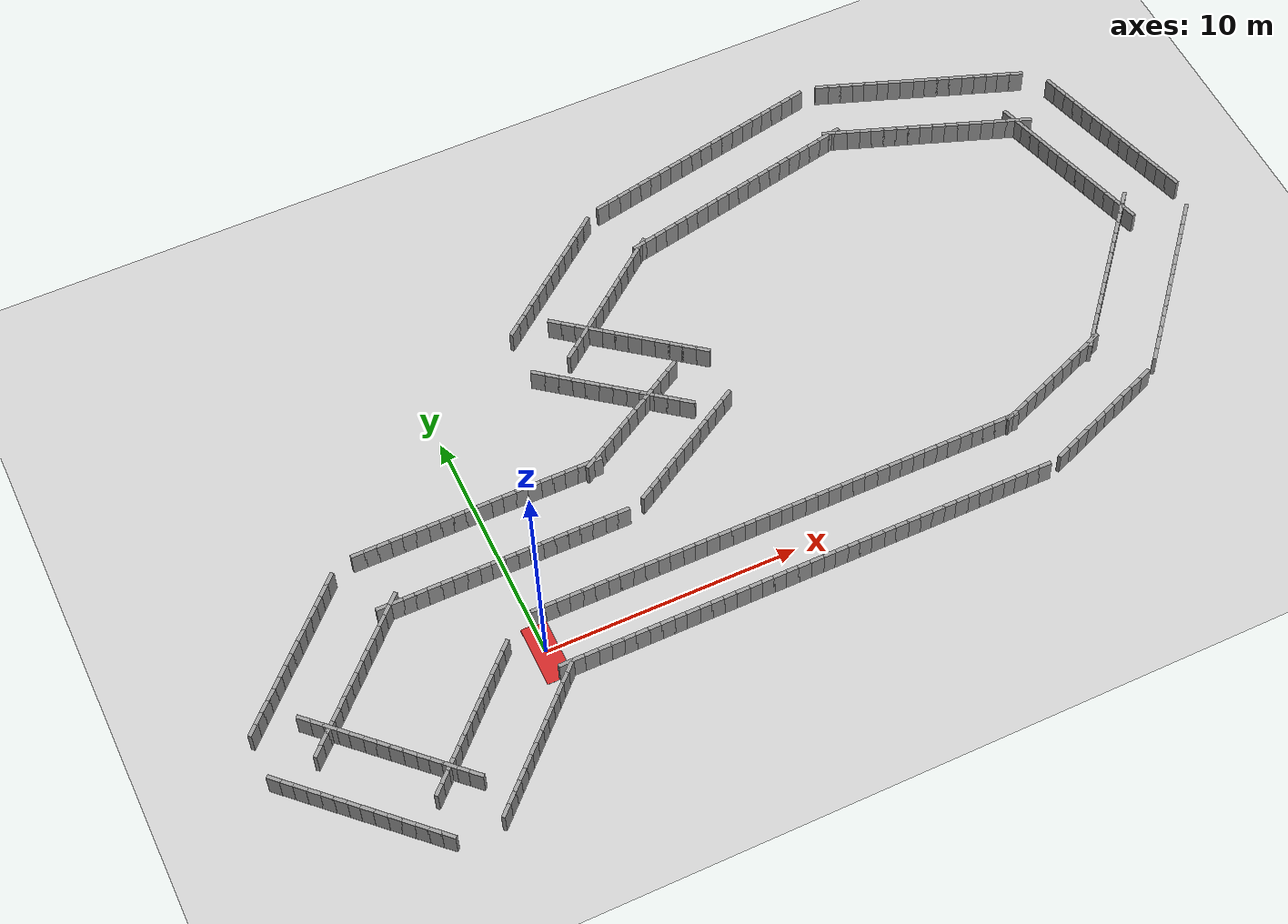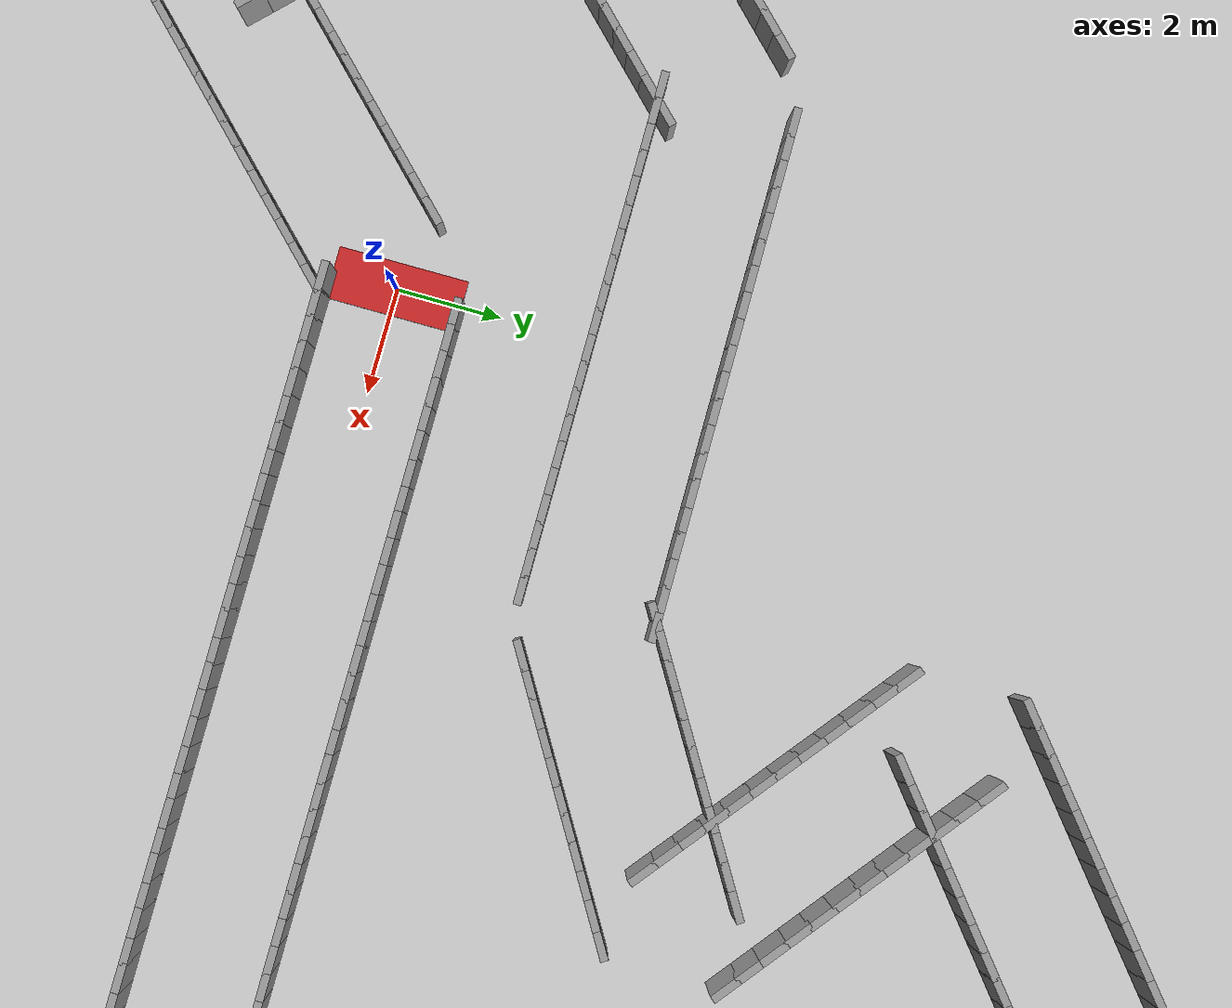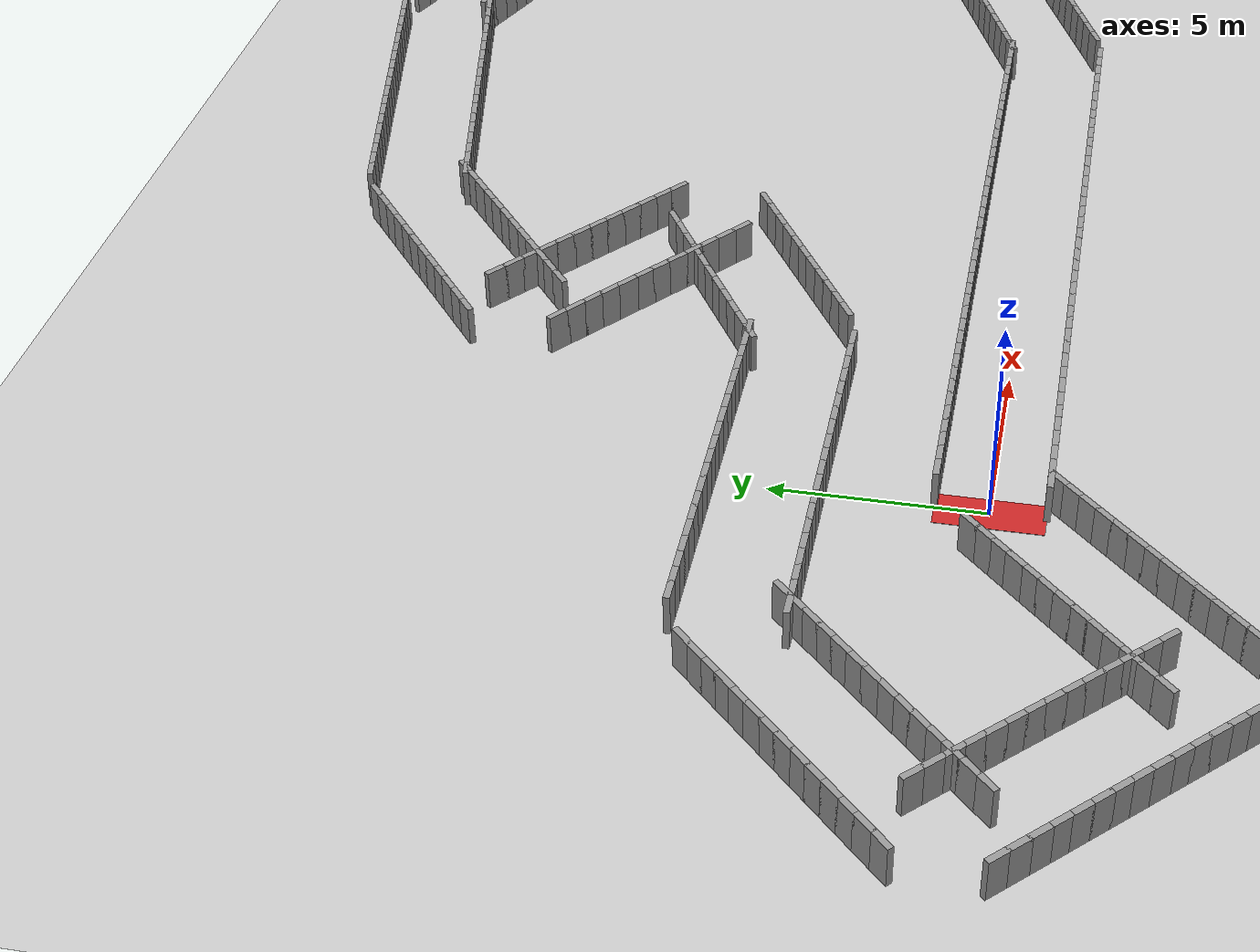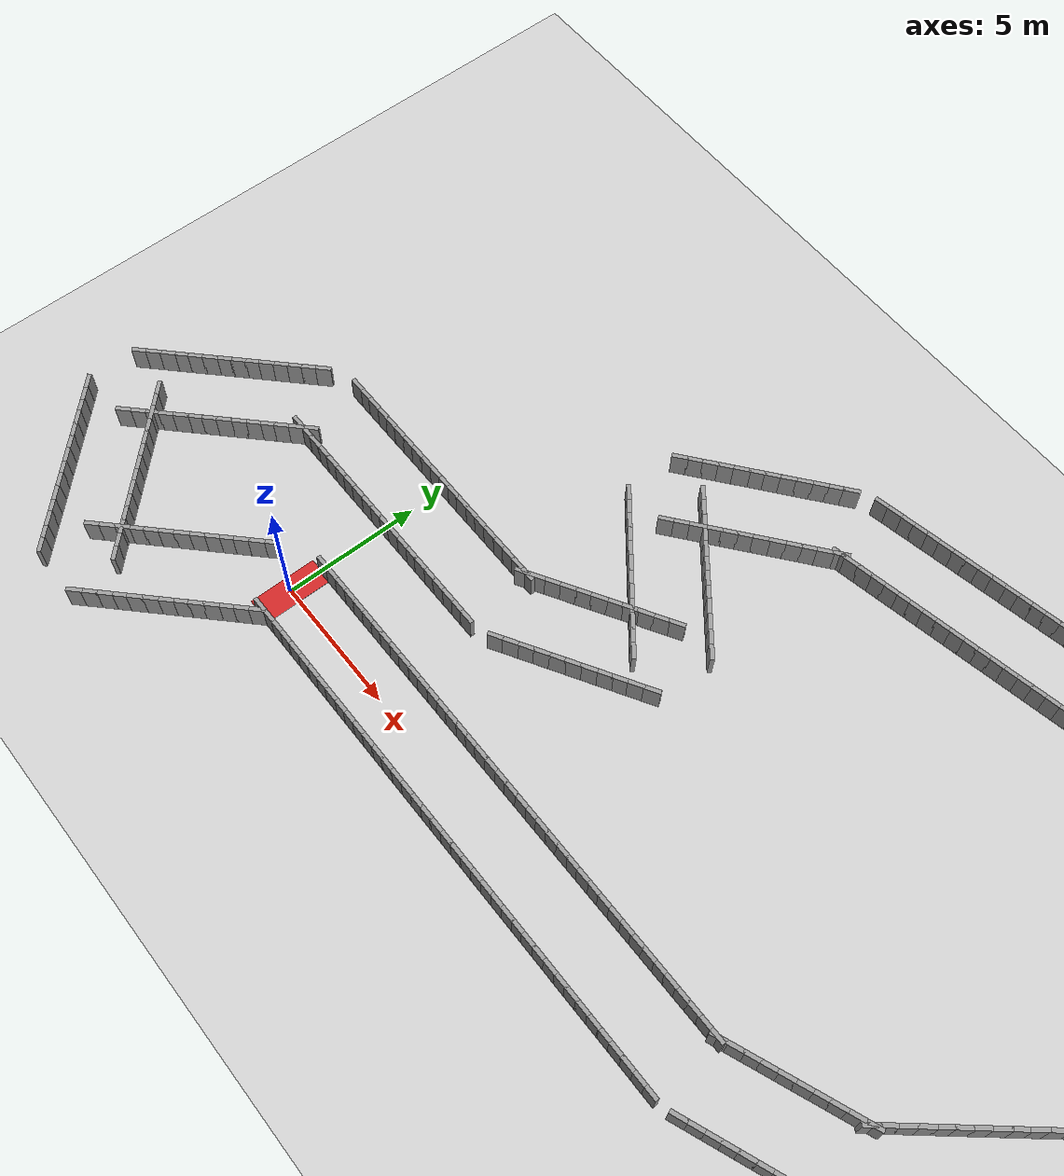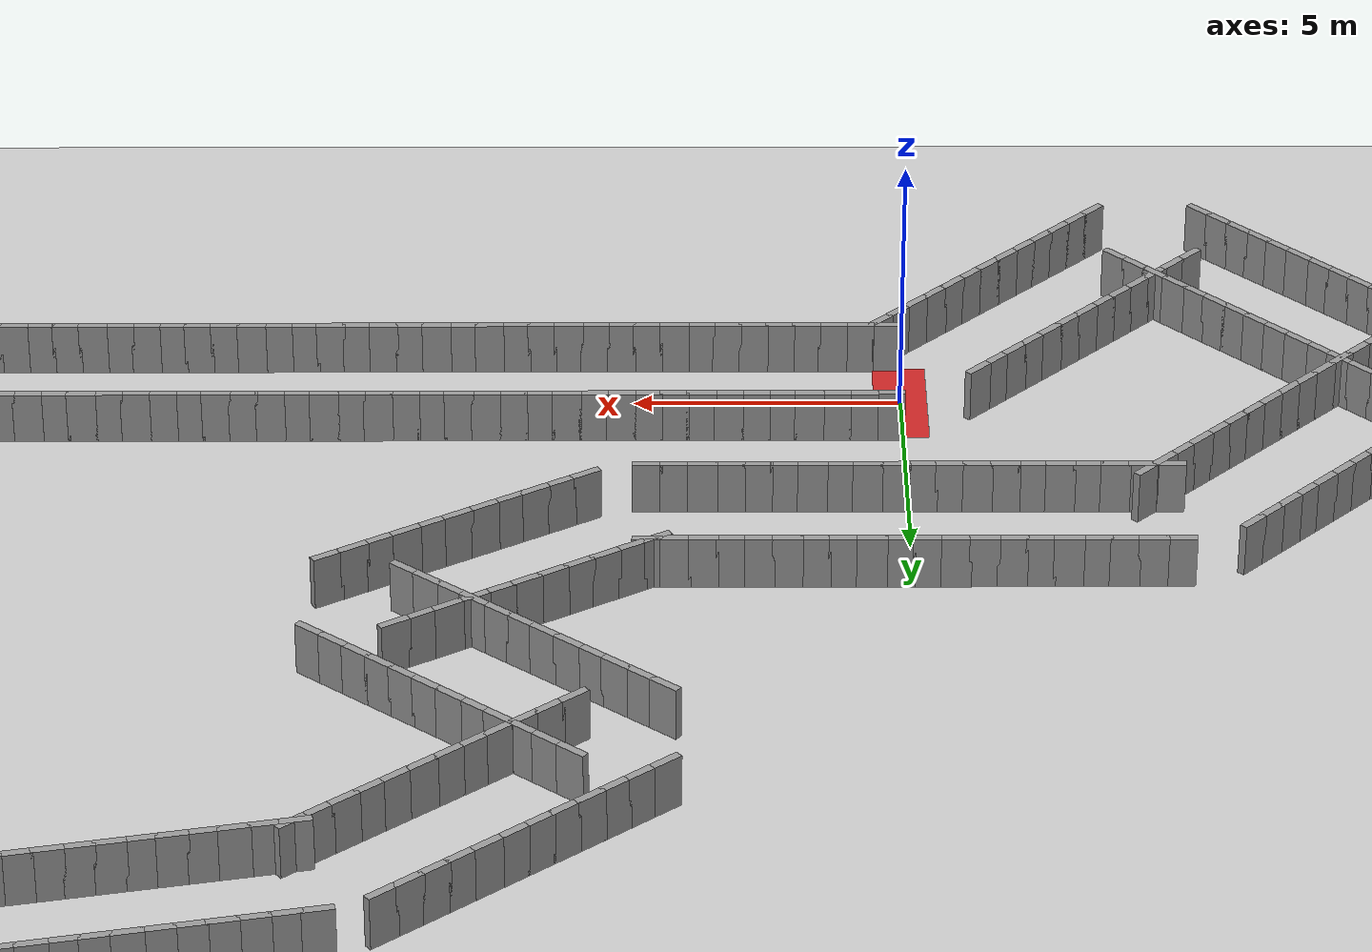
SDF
<?xml version="1.0" ?>
<sdf version="1.6">
  <world name="robot_harmonic_track">

    <include>
      <uri>model://sun</uri>
    </include>
    <include>
      <uri>model://ground_plane</uri>
    </include> -->

    <physics type="ode">
      <real_time_update_rate>1000.0</real_time_update_rate>
      <max_step_size>0.001</max_step_size>
    </physics>

    <model name='wall_inner_0'>
      <pose>0.25 1.25 0.5 0 0 0.0</pose>
      <static>1</static>
      <link name='link'>
        <collision name='collision'>
          <geometry>
            <box>
              <size>0.55 0.15 1.0</size>
            </box>
          </geometry>
        </collision>
        <visual name='visual'>
          <geometry>
            <box>
              <size>0.55 0.15 1.0</size>
            </box>
          </geometry>
          <material>
            <script>
              <uri>file://media/materials/scripts/gazebo.material</uri>
              <name>Gazebo/Grey</name>
            </script>
          </material>
        </visual>
      </link>
    </model>

    <model name='wall_outer_0'>
      <pose>0.25 -1.25 0.5 0 0 0.0</pose>
      <static>1</static>
      <link name='link'>
        <collision name='collision'>
          <geometry>
            <box>
              <size>0.55 0.15 1.0</size>
            </box>
          </geometry>
        </collision>
        <visual name='visual'>
          <geometry>
            <box>
              <size>0.55 0.15 1.0</size>
            </box>
          </geometry>
          <material>
            <script>
              <uri>file://media/materials/scripts/gazebo.material</uri>
              <name>Gazebo/Grey</name>
            </script>
          </material>
        </visual>
      </link>
    </model>

    <model name='wall_inner_1'>
      <pose>0.75 1.25 0.5 0 0 0.0</pose>
      <static>1</static>
      <link name='link'>
        <collision name='collision'>
          <geometry>
            <box>
              <size>0.55 0.15 1.0</size>
            </box>
          </geometry>
        </collision>
        <visual name='visual'>
          <geometry>
            <box>
              <size>0.55 0.15 1.0</size>
            </box>
          </geometry>
          <material>
            <script>
              <uri>file://media/materials/scripts/gazebo.material</uri>
              <name>Gazebo/Grey</name>
            </script>
          </material>
        </visual>
      </link>
    </model>

    <model name='wall_outer_1'>
      <pose>0.75 -1.25 0.5 0 0 0.0</pose>
      <static>1</static>
      <link name='link'>
        <collision name='collision'>
          <geometry>
            <box>
              <size>0.55 0.15 1.0</size>
            </box>
          </geometry>
        </collision>
        <visual name='visual'>
          <geometry>
            <box>
              <size>0.55 0.15 1.0</size>
            </box>
          </geometry>
          <material>
            <script>
              <uri>file://media/materials/scripts/gazebo.material</uri>
              <name>Gazebo/Grey</name>
            </script>
          </material>
        </visual>
      </link>
    </model>

    <model name='wall_inner_2'>
      <pose>1.25 1.25 0.5 0 0 0.0</pose>
      <static>1</static>
      <link name='link'>
        <collision name='collision'>
          <geometry>
            <box>
              <size>0.55 0.15 1.0</size>
            </box>
          </geometry>
        </collision>
        <visual name='visual'>
          <geometry>
            <box>
              <size>0.55 0.15 1.0</size>
            </box>
          </geometry>
          <material>
            <script>
              <uri>file://media/materials/scripts/gazebo.material</uri>
              <name>Gazebo/Grey</name>
            </script>
          </material>
        </visual>
      </link>
    </model>

    <model name='wall_outer_2'>
      <pose>1.25 -1.25 0.5 0 0 0.0</pose>
      <static>1</static>
      <link name='link'>
        <collision name='collision'>
          <geometry>
            <box>
              <size>0.55 0.15 1.0</size>
            </box>
          </geometry>
        </collision>
        <visual name='visual'>
          <geometry>
            <box>
              <size>0.55 0.15 1.0</size>
            </box>
          </geometry>
          <material>
            <script>
              <uri>file://media/materials/scripts/gazebo.material</uri>
              <name>Gazebo/Grey</name>
            </script>
          </material>
        </visual>
      </link>
    </model>

    <model name='wall_inner_3'>
      <pose>1.75 1.25 0.5 0 0 0.0</pose>
      <static>1</static>
      <link name='link'>
        <collision name='collision'>
          <geometry>
            <box>
              <size>0.55 0.15 1.0</size>
            </box>
          </geometry>
        </collision>
        <visual name='visual'>
          <geometry>
            <box>
              <size>0.55 0.15 1.0</size>
            </box>
          </geometry>
          <material>
            <script>
              <uri>file://media/materials/scripts/gazebo.material</uri>
              <name>Gazebo/Grey</name>
            </script>
          </material>
        </visual>
      </link>
    </model>

    <model name='wall_outer_3'>
      <pose>1.75 -1.25 0.5 0 0 0.0</pose>
      <static>1</static>
      <link name='link'>
        <collision name='collision'>
          <geometry>
            <box>
              <size>0.55 0.15 1.0</size>
            </box>
          </geometry>
        </collision>
        <visual name='visual'>
          <geometry>
            <box>
              <size>0.55 0.15 1.0</size>
            </box>
          </geometry>
          <material>
            <script>
              <uri>file://media/materials/scripts/gazebo.material</uri>
              <name>Gazebo/Grey</name>
            </script>
          </material>
        </visual>
      </link>
    </model>

    <model name='wall_inner_4'>
      <pose>2.25 1.25 0.5 0 0 0.0</pose>
      <static>1</static>
      <link name='link'>
        <collision name='collision'>
          <geometry>
            <box>
              <size>0.55 0.15 1.0</size>
            </box>
          </geometry>
        </collision>
        <visual name='visual'>
          <geometry>
            <box>
              <size>0.55 0.15 1.0</size>
            </box>
          </geometry>
          <material>
            <script>
              <uri>file://media/materials/scripts/gazebo.material</uri>
              <name>Gazebo/Grey</name>
            </script>
          </material>
        </visual>
      </link>
    </model>

    <model name='wall_outer_4'>
      <pose>2.25 -1.25 0.5 0 0 0.0</pose>
      <static>1</static>
      <link name='link'>
        <collision name='collision'>
          <geometry>
            <box>
              <size>0.55 0.15 1.0</size>
            </box>
          </geometry>
        </collision>
        <visual name='visual'>
          <geometry>
            <box>
              <size>0.55 0.15 1.0</size>
            </box>
          </geometry>
          <material>
            <script>
              <uri>file://media/materials/scripts/gazebo.material</uri>
              <name>Gazebo/Grey</name>
            </script>
          </material>
        </visual>
      </link>
    </model>

    <model name='wall_inner_5'>
      <pose>2.75 1.25 0.5 0 0 0.0</pose>
      <static>1</static>
      <link name='link'>
        <collision name='collision'>
          <geometry>
            <box>
              <size>0.55 0.15 1.0</size>
            </box>
          </geometry>
        </collision>
        <visual name='visual'>
          <geometry>
            <box>
              <size>0.55 0.15 1.0</size>
            </box>
          </geometry>
          <material>
            <script>
              <uri>file://media/materials/scripts/gazebo.material</uri>
              <name>Gazebo/Grey</name>
            </script>
          </material>
        </visual>
      </link>
    </model>

    <model name='wall_outer_5'>
      <pose>2.75 -1.25 0.5 0 0 0.0</pose>
      <static>1</static>
      <link name='link'>
        <collision name='collision'>
          <geometry>
            <box>
              <size>0.55 0.15 1.0</size>
            </box>
          </geometry>
        </collision>
        <visual name='visual'>
          <geometry>
            <box>
              <size>0.55 0.15 1.0</size>
            </box>
          </geometry>
          <material>
            <script>
              <uri>file://media/materials/scripts/gazebo.material</uri>
              <name>Gazebo/Grey</name>
            </script>
          </material>
        </visual>
      </link>
    </model>

    <model name='wall_inner_6'>
      <pose>3.25 1.25 0.5 0 0 0.0</pose>
      <static>1</static>
      <link name='link'>
        <collision name='collision'>
          <geometry>
            <box>
              <size>0.55 0.15 1.0</size>
            </box>
          </geometry>
        </collision>
        <visual name='visual'>
          <geometry>
            <box>
              <size>0.55 0.15 1.0</size>
            </box>
          </geometry>
          <material>
            <script>
              <uri>file://media/materials/scripts/gazebo.material</uri>
              <name>Gazebo/Grey</name>
            </script>
          </material>
        </visual>
      </link>
    </model>

    <model name='wall_outer_6'>
      <pose>3.25 -1.25 0.5 0 0 0.0</pose>
      <static>1</static>
      <link name='link'>
        <collision name='collision'>
          <geometry>
            <box>
              <size>0.55 0.15 1.0</size>
            </box>
          </geometry>
        </collision>
        <visual name='visual'>
          <geometry>
            <box>
              <size>0.55 0.15 1.0</size>
            </box>
          </geometry>
          <material>
            <script>
              <uri>file://media/materials/scripts/gazebo.material</uri>
              <name>Gazebo/Grey</name>
            </script>
          </material>
        </visual>
      </link>
    </model>

    <model name='wall_inner_7'>
      <pose>3.75 1.25 0.5 0 0 0.0</pose>
      <static>1</static>
      <link name='link'>
        <collision name='collision'>
          <geometry>
            <box>
              <size>0.55 0.15 1.0</size>
            </box>
          </geometry>
        </collision>
        <visual name='visual'>
          <geometry>
            <box>
              <size>0.55 0.15 1.0</size>
            </box>
          </geometry>
          <material>
            <script>
              <uri>file://media/materials/scripts/gazebo.material</uri>
              <name>Gazebo/Grey</name>
            </script>
          </material>
        </visual>
      </link>
    </model>

    <model name='wall_outer_7'>
      <pose>3.75 -1.25 0.5 0 0 0.0</pose>
      <static>1</static>
      <link name='link'>
        <collision name='collision'>
          <geometry>
            <box>
              <size>0.55 0.15 1.0</size>
            </box>
          </geometry>
        </collision>
        <visual name='visual'>
          <geometry>
            <box>
              <size>0.55 0.15 1.0</size>
            </box>
          </geometry>
          <material>
            <script>
              <uri>file://media/materials/scripts/gazebo.material</uri>
              <name>Gazebo/Grey</name>
            </script>
          </material>
        </visual>
      </link>
    </model>

    <model name='wall_inner_8'>
      <pose>4.25 1.25 0.5 0 0 0.0</pose>
      <static>1</static>
      <link name='link'>
        <collision name='collision'>
          <geometry>
            <box>
              <size>0.55 0.15 1.0</size>
            </box>
          </geometry>
        </collision>
        <visual name='visual'>
          <geometry>
            <box>
              <size>0.55 0.15 1.0</size>
            </box>
          </geometry>
          <material>
            <script>
              <uri>file://media/materials/scripts/gazebo.material</uri>
              <name>Gazebo/Grey</name>
            </script>
          </material>
        </visual>
      </link>
    </model>

    <model name='wall_outer_8'>
      <pose>4.25 -1.25 0.5 0 0 0.0</pose>
      <static>1</static>
      <link name='link'>
        <collision name='collision'>
          <geometry>
            <box>
              <size>0.55 0.15 1.0</size>
            </box>
          </geometry>
        </collision>
        <visual name='visual'>
          <geometry>
            <box>
              <size>0.55 0.15 1.0</size>
            </box>
          </geometry>
          <material>
            <script>
              <uri>file://media/materials/scripts/gazebo.material</uri>
              <name>Gazebo/Grey</name>
            </script>
          </material>
        </visual>
      </link>
    </model>

    <model name='wall_inner_9'>
      <pose>4.75 1.25 0.5 0 0 0.0</pose>
      <static>1</static>
      <link name='link'>
        <collision name='collision'>
          <geometry>
            <box>
              <size>0.55 0.15 1.0</size>
            </box>
          </geometry>
        </collision>
        <visual name='visual'>
          <geometry>
            <box>
              <size>0.55 0.15 1.0</size>
            </box>
          </geometry>
          <material>
            <script>
              <uri>file://media/materials/scripts/gazebo.material</uri>
              <name>Gazebo/Grey</name>
            </script>
          </material>
        </visual>
      </link>
    </model>

    <model name='wall_outer_9'>
      <pose>4.75 -1.25 0.5 0 0 0.0</pose>
      <static>1</static>
      <link name='link'>
        <collision name='collision'>
          <geometry>
            <box>
              <size>0.55 0.15 1.0</size>
            </box>
          </geometry>
        </collision>
        <visual name='visual'>
          <geometry>
            <box>
              <size>0.55 0.15 1.0</size>
            </box>
          </geometry>
          <material>
            <script>
              <uri>file://media/materials/scripts/gazebo.material</uri>
              <name>Gazebo/Grey</name>
            </script>
          </material>
        </visual>
      </link>
    </model>

    <model name='wall_inner_10'>
      <pose>5.25 1.25 0.5 0 0 0.0</pose>
      <static>1</static>
      <link name='link'>
        <collision name='collision'>
          <geometry>
            <box>
              <size>0.55 0.15 1.0</size>
            </box>
          </geometry>
        </collision>
        <visual name='visual'>
          <geometry>
            <box>
              <size>0.55 0.15 1.0</size>
            </box>
          </geometry>
          <material>
            <script>
              <uri>file://media/materials/scripts/gazebo.material</uri>
              <name>Gazebo/Grey</name>
            </script>
          </material>
        </visual>
      </link>
    </model>

    <model name='wall_outer_10'>
      <pose>5.25 -1.25 0.5 0 0 0.0</pose>
      <static>1</static>
      <link name='link'>
        <collision name='collision'>
          <geometry>
            <box>
              <size>0.55 0.15 1.0</size>
            </box>
          </geometry>
        </collision>
        <visual name='visual'>
          <geometry>
            <box>
              <size>0.55 0.15 1.0</size>
            </box>
          </geometry>
          <material>
            <script>
              <uri>file://media/materials/scripts/gazebo.material</uri>
              <name>Gazebo/Grey</name>
            </script>
          </material>
        </visual>
      </link>
    </model>

    <model name='wall_inner_11'>
      <pose>5.75 1.25 0.5 0 0 0.0</pose>
      <static>1</static>
      <link name='link'>
        <collision name='collision'>
          <geometry>
            <box>
              <size>0.55 0.15 1.0</size>
            </box>
          </geometry>
        </collision>
        <visual name='visual'>
          <geometry>
            <box>
              <size>0.55 0.15 1.0</size>
            </box>
          </geometry>
          <material>
            <script>
              <uri>file://media/materials/scripts/gazebo.material</uri>
              <name>Gazebo/Grey</name>
            </script>
          </material>
        </visual>
      </link>
    </model>

    <model name='wall_outer_11'>
      <pose>5.75 -1.25 0.5 0 0 0.0</pose>
      <static>1</static>
      <link name='link'>
        <collision name='collision'>
          <geometry>
            <box>
              <size>0.55 0.15 1.0</size>
            </box>
          </geometry>
        </collision>
        <visual name='visual'>
          <geometry>
            <box>
              <size>0.55 0.15 1.0</size>
            </box>
          </geometry>
          <material>
            <script>
              <uri>file://media/materials/scripts/gazebo.material</uri>
              <name>Gazebo/Grey</name>
            </script>
          </material>
        </visual>
      </link>
    </model>

    <model name='wall_inner_12'>
      <pose>6.25 1.25 0.5 0 0 0.0</pose>
      <static>1</static>
      <link name='link'>
        <collision name='collision'>
          <geometry>
            <box>
              <size>0.55 0.15 1.0</size>
            </box>
          </geometry>
        </collision>
        <visual name='visual'>
          <geometry>
            <box>
              <size>0.55 0.15 1.0</size>
            </box>
          </geometry>
          <material>
            <script>
              <uri>file://media/materials/scripts/gazebo.material</uri>
              <name>Gazebo/Grey</name>
            </script>
          </material>
        </visual>
      </link>
    </model>

    <model name='wall_outer_12'>
      <pose>6.25 -1.25 0.5 0 0 0.0</pose>
      <static>1</static>
      <link name='link'>
        <collision name='collision'>
          <geometry>
            <box>
              <size>0.55 0.15 1.0</size>
            </box>
          </geometry>
        </collision>
        <visual name='visual'>
          <geometry>
            <box>
              <size>0.55 0.15 1.0</size>
            </box>
          </geometry>
          <material>
            <script>
              <uri>file://media/materials/scripts/gazebo.material</uri>
              <name>Gazebo/Grey</name>
            </script>
          </material>
        </visual>
      </link>
    </model>

    <model name='wall_inner_13'>
      <pose>6.75 1.25 0.5 0 0 0.0</pose>
      <static>1</static>
      <link name='link'>
        <collision name='collision'>
          <geometry>
            <box>
              <size>0.55 0.15 1.0</size>
            </box>
          </geometry>
        </collision>
        <visual name='visual'>
          <geometry>
            <box>
              <size>0.55 0.15 1.0</size>
            </box>
          </geometry>
          <material>
            <script>
              <uri>file://media/materials/scripts/gazebo.material</uri>
              <name>Gazebo/Grey</name>
            </script>
          </material>
        </visual>
      </link>
    </model>

    <model name='wall_outer_13'>
      <pose>6.75 -1.25 0.5 0 0 0.0</pose>
      <static>1</static>
      <link name='link'>
        <collision name='collision'>
          <geometry>
            <box>
              <size>0.55 0.15 1.0</size>
            </box>
          </geometry>
        </collision>
        <visual name='visual'>
          <geometry>
            <box>
              <size>0.55 0.15 1.0</size>
            </box>
          </geometry>
          <material>
            <script>
              <uri>file://media/materials/scripts/gazebo.material</uri>
              <name>Gazebo/Grey</name>
            </script>
          </material>
        </visual>
      </link>
    </model>

    <model name='wall_inner_14'>
      <pose>7.25 1.25 0.5 0 0 0.0</pose>
      <static>1</static>
      <link name='link'>
        <collision name='collision'>
          <geometry>
            <box>
              <size>0.55 0.15 1.0</size>
            </box>
          </geometry>
        </collision>
        <visual name='visual'>
          <geometry>
            <box>
              <size>0.55 0.15 1.0</size>
            </box>
          </geometry>
          <material>
            <script>
              <uri>file://media/materials/scripts/gazebo.material</uri>
              <name>Gazebo/Grey</name>
            </script>
          </material>
        </visual>
      </link>
    </model>

    <model name='wall_outer_14'>
      <pose>7.25 -1.25 0.5 0 0 0.0</pose>
      <static>1</static>
      <link name='link'>
        <collision name='collision'>
          <geometry>
            <box>
              <size>0.55 0.15 1.0</size>
            </box>
          </geometry>
        </collision>
        <visual name='visual'>
          <geometry>
            <box>
              <size>0.55 0.15 1.0</size>
            </box>
          </geometry>
          <material>
            <script>
              <uri>file://media/materials/scripts/gazebo.material</uri>
              <name>Gazebo/Grey</name>
            </script>
          </material>
        </visual>
      </link>
    </model>

    <model name='wall_inner_15'>
      <pose>7.75 1.25 0.5 0 0 0.0</pose>
      <static>1</static>
      <link name='link'>
        <collision name='collision'>
          <geometry>
            <box>
              <size>0.55 0.15 1.0</size>
            </box>
          </geometry>
        </collision>
        <visual name='visual'>
          <geometry>
            <box>
              <size>0.55 0.15 1.0</size>
            </box>
          </geometry>
          <material>
            <script>
              <uri>file://media/materials/scripts/gazebo.material</uri>
              <name>Gazebo/Grey</name>
            </script>
          </material>
        </visual>
      </link>
    </model>

    <model name='wall_outer_15'>
      <pose>7.75 -1.25 0.5 0 0 0.0</pose>
      <static>1</static>
      <link name='link'>
        <collision name='collision'>
          <geometry>
            <box>
              <size>0.55 0.15 1.0</size>
            </box>
          </geometry>
        </collision>
        <visual name='visual'>
          <geometry>
            <box>
              <size>0.55 0.15 1.0</size>
            </box>
          </geometry>
          <material>
            <script>
              <uri>file://media/materials/scripts/gazebo.material</uri>
              <name>Gazebo/Grey</name>
            </script>
          </material>
        </visual>
      </link>
    </model>

    <model name='wall_inner_16'>
      <pose>8.25 1.25 0.5 0 0 0.0</pose>
      <static>1</static>
      <link name='link'>
        <collision name='collision'>
          <geometry>
            <box>
              <size>0.55 0.15 1.0</size>
            </box>
          </geometry>
        </collision>
        <visual name='visual'>
          <geometry>
            <box>
              <size>0.55 0.15 1.0</size>
            </box>
          </geometry>
          <material>
            <script>
              <uri>file://media/materials/scripts/gazebo.material</uri>
              <name>Gazebo/Grey</name>
            </script>
          </material>
        </visual>
      </link>
    </model>

    <model name='wall_outer_16'>
      <pose>8.25 -1.25 0.5 0 0 0.0</pose>
      <static>1</static>
      <link name='link'>
        <collision name='collision'>
          <geometry>
            <box>
              <size>0.55 0.15 1.0</size>
            </box>
          </geometry>
        </collision>
        <visual name='visual'>
          <geometry>
            <box>
              <size>0.55 0.15 1.0</size>
            </box>
          </geometry>
          <material>
            <script>
              <uri>file://media/materials/scripts/gazebo.material</uri>
              <name>Gazebo/Grey</name>
            </script>
          </material>
        </visual>
      </link>
    </model>

    <model name='wall_inner_17'>
      <pose>8.75 1.25 0.5 0 0 0.0</pose>
      <static>1</static>
      <link name='link'>
        <collision name='collision'>
          <geometry>
            <box>
              <size>0.55 0.15 1.0</size>
            </box>
          </geometry>
        </collision>
        <visual name='visual'>
          <geometry>
            <box>
              <size>0.55 0.15 1.0</size>
            </box>
          </geometry>
          <material>
            <script>
              <uri>file://media/materials/scripts/gazebo.material</uri>
              <name>Gazebo/Grey</name>
            </script>
          </material>
        </visual>
      </link>
    </model>

    <model name='wall_outer_17'>
      <pose>8.75 -1.25 0.5 0 0 0.0</pose>
      <static>1</static>
      <link name='link'>
        <collision name='collision'>
          <geometry>
            <box>
              <size>0.55 0.15 1.0</size>
            </box>
          </geometry>
        </collision>
        <visual name='visual'>
          <geometry>
            <box>
              <size>0.55 0.15 1.0</size>
            </box>
          </geometry>
          <material>
            <script>
              <uri>file://media/materials/scripts/gazebo.material</uri>
              <name>Gazebo/Grey</name>
            </script>
          </material>
        </visual>
      </link>
    </model>

    <model name='wall_inner_18'>
      <pose>9.25 1.25 0.5 0 0 0.0</pose>
      <static>1</static>
      <link name='link'>
        <collision name='collision'>
          <geometry>
            <box>
              <size>0.55 0.15 1.0</size>
            </box>
          </geometry>
        </collision>
        <visual name='visual'>
          <geometry>
            <box>
              <size>0.55 0.15 1.0</size>
            </box>
          </geometry>
          <material>
            <script>
              <uri>file://media/materials/scripts/gazebo.material</uri>
              <name>Gazebo/Grey</name>
            </script>
          </material>
        </visual>
      </link>
    </model>

    <model name='wall_outer_18'>
      <pose>9.25 -1.25 0.5 0 0 0.0</pose>
      <static>1</static>
      <link name='link'>
        <collision name='collision'>
          <geometry>
            <box>
              <size>0.55 0.15 1.0</size>
            </box>
          </geometry>
        </collision>
        <visual name='visual'>
          <geometry>
            <box>
              <size>0.55 0.15 1.0</size>
            </box>
          </geometry>
          <material>
            <script>
              <uri>file://media/materials/scripts/gazebo.material</uri>
              <name>Gazebo/Grey</name>
            </script>
          </material>
        </visual>
      </link>
    </model>

    <model name='wall_inner_19'>
      <pose>9.75 1.25 0.5 0 0 0.0</pose>
      <static>1</static>
      <link name='link'>
        <collision name='collision'>
          <geometry>
            <box>
              <size>0.55 0.15 1.0</size>
            </box>
          </geometry>
        </collision>
        <visual name='visual'>
          <geometry>
            <box>
              <size>0.55 0.15 1.0</size>
            </box>
          </geometry>
          <material>
            <script>
              <uri>file://media/materials/scripts/gazebo.material</uri>
              <name>Gazebo/Grey</name>
            </script>
          </material>
        </visual>
      </link>
    </model>

    <model name='wall_outer_19'>
      <pose>9.75 -1.25 0.5 0 0 0.0</pose>
      <static>1</static>
      <link name='link'>
        <collision name='collision'>
          <geometry>
            <box>
              <size>0.55 0.15 1.0</size>
            </box>
          </geometry>
        </collision>
        <visual name='visual'>
          <geometry>
            <box>
              <size>0.55 0.15 1.0</size>
            </box>
          </geometry>
          <material>
            <script>
              <uri>file://media/materials/scripts/gazebo.material</uri>
              <name>Gazebo/Grey</name>
            </script>
          </material>
        </visual>
      </link>
    </model>

    <model name='wall_inner_20'>
      <pose>10.25 1.25 0.5 0 0 0.0</pose>
      <static>1</static>
      <link name='link'>
        <collision name='collision'>
          <geometry>
            <box>
              <size>0.55 0.15 1.0</size>
            </box>
          </geometry>
        </collision>
        <visual name='visual'>
          <geometry>
            <box>
              <size>0.55 0.15 1.0</size>
            </box>
          </geometry>
          <material>
            <script>
              <uri>file://media/materials/scripts/gazebo.material</uri>
              <name>Gazebo/Grey</name>
            </script>
          </material>
        </visual>
      </link>
    </model>

    <model name='wall_outer_20'>
      <pose>10.25 -1.25 0.5 0 0 0.0</pose>
      <static>1</static>
      <link name='link'>
        <collision name='collision'>
          <geometry>
            <box>
              <size>0.55 0.15 1.0</size>
            </box>
          </geometry>
        </collision>
        <visual name='visual'>
          <geometry>
            <box>
              <size>0.55 0.15 1.0</size>
            </box>
          </geometry>
          <material>
            <script>
              <uri>file://media/materials/scripts/gazebo.material</uri>
              <name>Gazebo/Grey</name>
            </script>
          </material>
        </visual>
      </link>
    </model>

    <model name='wall_inner_21'>
      <pose>10.75 1.25 0.5 0 0 0.0</pose>
      <static>1</static>
      <link name='link'>
        <collision name='collision'>
          <geometry>
            <box>
              <size>0.55 0.15 1.0</size>
            </box>
          </geometry>
        </collision>
        <visual name='visual'>
          <geometry>
            <box>
              <size>0.55 0.15 1.0</size>
            </box>
          </geometry>
          <material>
            <script>
              <uri>file://media/materials/scripts/gazebo.material</uri>
              <name>Gazebo/Grey</name>
            </script>
          </material>
        </visual>
      </link>
    </model>

    <model name='wall_outer_21'>
      <pose>10.75 -1.25 0.5 0 0 0.0</pose>
      <static>1</static>
      <link name='link'>
        <collision name='collision'>
          <geometry>
            <box>
              <size>0.55 0.15 1.0</size>
            </box>
          </geometry>
        </collision>
        <visual name='visual'>
          <geometry>
            <box>
              <size>0.55 0.15 1.0</size>
            </box>
          </geometry>
          <material>
            <script>
              <uri>file://media/materials/scripts/gazebo.material</uri>
              <name>Gazebo/Grey</name>
            </script>
          </material>
        </visual>
      </link>
    </model>

    <model name='wall_inner_22'>
      <pose>11.25 1.25 0.5 0 0 0.0</pose>
      <static>1</static>
      <link name='link'>
        <collision name='collision'>
          <geometry>
            <box>
              <size>0.55 0.15 1.0</size>
            </box>
          </geometry>
        </collision>
        <visual name='visual'>
          <geometry>
            <box>
              <size>0.55 0.15 1.0</size>
            </box>
          </geometry>
          <material>
            <script>
              <uri>file://media/materials/scripts/gazebo.material</uri>
              <name>Gazebo/Grey</name>
            </script>
          </material>
        </visual>
      </link>
    </model>

    <model name='wall_outer_22'>
      <pose>11.25 -1.25 0.5 0 0 0.0</pose>
      <static>1</static>
      <link name='link'>
        <collision name='collision'>
          <geometry>
            <box>
              <size>0.55 0.15 1.0</size>
            </box>
          </geometry>
        </collision>
        <visual name='visual'>
          <geometry>
            <box>
              <size>0.55 0.15 1.0</size>
            </box>
          </geometry>
          <material>
            <script>
              <uri>file://media/materials/scripts/gazebo.material</uri>
              <name>Gazebo/Grey</name>
            </script>
          </material>
        </visual>
      </link>
    </model>

    <model name='wall_inner_23'>
      <pose>11.75 1.25 0.5 0 0 0.0</pose>
      <static>1</static>
      <link name='link'>
        <collision name='collision'>
          <geometry>
            <box>
              <size>0.55 0.15 1.0</size>
            </box>
          </geometry>
        </collision>
        <visual name='visual'>
          <geometry>
            <box>
              <size>0.55 0.15 1.0</size>
            </box>
          </geometry>
          <material>
            <script>
              <uri>file://media/materials/scripts/gazebo.material</uri>
              <name>Gazebo/Grey</name>
            </script>
          </material>
        </visual>
      </link>
    </model>

    <model name='wall_outer_23'>
      <pose>11.75 -1.25 0.5 0 0 0.0</pose>
      <static>1</static>
      <link name='link'>
        <collision name='collision'>
          <geometry>
            <box>
              <size>0.55 0.15 1.0</size>
            </box>
          </geometry>
        </collision>
        <visual name='visual'>
          <geometry>
            <box>
              <size>0.55 0.15 1.0</size>
            </box>
          </geometry>
          <material>
            <script>
              <uri>file://media/materials/scripts/gazebo.material</uri>
              <name>Gazebo/Grey</name>
            </script>
          </material>
        </visual>
      </link>
    </model>

    <model name='wall_inner_24'>
      <pose>12.25 1.25 0.5 0 0 0.0</pose>
      <static>1</static>
      <link name='link'>
        <collision name='collision'>
          <geometry>
            <box>
              <size>0.55 0.15 1.0</size>
            </box>
          </geometry>
        </collision>
        <visual name='visual'>
          <geometry>
            <box>
              <size>0.55 0.15 1.0</size>
            </box>
          </geometry>
          <material>
            <script>
              <uri>file://media/materials/scripts/gazebo.material</uri>
              <name>Gazebo/Grey</name>
            </script>
          </material>
        </visual>
      </link>
    </model>

    <model name='wall_outer_24'>
      <pose>12.25 -1.25 0.5 0 0 0.0</pose>
      <static>1</static>
      <link name='link'>
        <collision name='collision'>
          <geometry>
            <box>
              <size>0.55 0.15 1.0</size>
            </box>
          </geometry>
        </collision>
        <visual name='visual'>
          <geometry>
            <box>
              <size>0.55 0.15 1.0</size>
            </box>
          </geometry>
          <material>
            <script>
              <uri>file://media/materials/scripts/gazebo.material</uri>
              <name>Gazebo/Grey</name>
            </script>
          </material>
        </visual>
      </link>
    </model>

    <model name='wall_inner_25'>
      <pose>12.75 1.25 0.5 0 0 0.0</pose>
      <static>1</static>
      <link name='link'>
        <collision name='collision'>
          <geometry>
            <box>
              <size>0.55 0.15 1.0</size>
            </box>
          </geometry>
        </collision>
        <visual name='visual'>
          <geometry>
            <box>
              <size>0.55 0.15 1.0</size>
            </box>
          </geometry>
          <material>
            <script>
              <uri>file://media/materials/scripts/gazebo.material</uri>
              <name>Gazebo/Grey</name>
            </script>
          </material>
        </visual>
      </link>
    </model>

    <model name='wall_outer_25'>
      <pose>12.75 -1.25 0.5 0 0 0.0</pose>
      <static>1</static>
      <link name='link'>
        <collision name='collision'>
          <geometry>
            <box>
              <size>0.55 0.15 1.0</size>
            </box>
          </geometry>
        </collision>
        <visual name='visual'>
          <geometry>
            <box>
              <size>0.55 0.15 1.0</size>
            </box>
          </geometry>
          <material>
            <script>
              <uri>file://media/materials/scripts/gazebo.material</uri>
              <name>Gazebo/Grey</name>
            </script>
          </material>
        </visual>
      </link>
    </model>

    <model name='wall_inner_26'>
      <pose>13.25 1.25 0.5 0 0 0.0</pose>
      <static>1</static>
      <link name='link'>
        <collision name='collision'>
          <geometry>
            <box>
              <size>0.55 0.15 1.0</size>
            </box>
          </geometry>
        </collision>
        <visual name='visual'>
          <geometry>
            <box>
              <size>0.55 0.15 1.0</size>
            </box>
          </geometry>
          <material>
            <script>
              <uri>file://media/materials/scripts/gazebo.material</uri>
              <name>Gazebo/Grey</name>
            </script>
          </material>
        </visual>
      </link>
    </model>

    <model name='wall_outer_26'>
      <pose>13.25 -1.25 0.5 0 0 0.0</pose>
      <static>1</static>
      <link name='link'>
        <collision name='collision'>
          <geometry>
            <box>
              <size>0.55 0.15 1.0</size>
            </box>
          </geometry>
        </collision>
        <visual name='visual'>
          <geometry>
            <box>
              <size>0.55 0.15 1.0</size>
            </box>
          </geometry>
          <material>
            <script>
              <uri>file://media/materials/scripts/gazebo.material</uri>
              <name>Gazebo/Grey</name>
            </script>
          </material>
        </visual>
      </link>
    </model>

    <model name='wall_inner_27'>
      <pose>13.75 1.25 0.5 0 0 0.0</pose>
      <static>1</static>
      <link name='link'>
        <collision name='collision'>
          <geometry>
            <box>
              <size>0.55 0.15 1.0</size>
            </box>
          </geometry>
        </collision>
        <visual name='visual'>
          <geometry>
            <box>
              <size>0.55 0.15 1.0</size>
            </box>
          </geometry>
          <material>
            <script>
              <uri>file://media/materials/scripts/gazebo.material</uri>
              <name>Gazebo/Grey</name>
            </script>
          </material>
        </visual>
      </link>
    </model>

    <model name='wall_outer_27'>
      <pose>13.75 -1.25 0.5 0 0 0.0</pose>
      <static>1</static>
      <link name='link'>
        <collision name='collision'>
          <geometry>
            <box>
              <size>0.55 0.15 1.0</size>
            </box>
          </geometry>
        </collision>
        <visual name='visual'>
          <geometry>
            <box>
              <size>0.55 0.15 1.0</size>
            </box>
          </geometry>
          <material>
            <script>
              <uri>file://media/materials/scripts/gazebo.material</uri>
              <name>Gazebo/Grey</name>
            </script>
          </material>
        </visual>
      </link>
    </model>

    <model name='wall_inner_28'>
      <pose>14.25 1.25 0.5 0 0 0.0</pose>
      <static>1</static>
      <link name='link'>
        <collision name='collision'>
          <geometry>
            <box>
              <size>0.55 0.15 1.0</size>
            </box>
          </geometry>
        </collision>
        <visual name='visual'>
          <geometry>
            <box>
              <size>0.55 0.15 1.0</size>
            </box>
          </geometry>
          <material>
            <script>
              <uri>file://media/materials/scripts/gazebo.material</uri>
              <name>Gazebo/Grey</name>
            </script>
          </material>
        </visual>
      </link>
    </model>

    <model name='wall_outer_28'>
      <pose>14.25 -1.25 0.5 0 0 0.0</pose>
      <static>1</static>
      <link name='link'>
        <collision name='collision'>
          <geometry>
            <box>
              <size>0.55 0.15 1.0</size>
            </box>
          </geometry>
        </collision>
        <visual name='visual'>
          <geometry>
            <box>
              <size>0.55 0.15 1.0</size>
            </box>
          </geometry>
          <material>
            <script>
              <uri>file://media/materials/scripts/gazebo.material</uri>
              <name>Gazebo/Grey</name>
            </script>
          </material>
        </visual>
      </link>
    </model>

    <model name='wall_inner_29'>
      <pose>14.75 1.25 0.5 0 0 0.0</pose>
      <static>1</static>
      <link name='link'>
        <collision name='collision'>
          <geometry>
            <box>
              <size>0.55 0.15 1.0</size>
            </box>
          </geometry>
        </collision>
        <visual name='visual'>
          <geometry>
            <box>
              <size>0.55 0.15 1.0</size>
            </box>
          </geometry>
          <material>
            <script>
              <uri>file://media/materials/scripts/gazebo.material</uri>
              <name>Gazebo/Grey</name>
            </script>
          </material>
        </visual>
      </link>
    </model>

    <model name='wall_outer_29'>
      <pose>14.75 -1.25 0.5 0 0 0.0</pose>
      <static>1</static>
      <link name='link'>
        <collision name='collision'>
          <geometry>
            <box>
              <size>0.55 0.15 1.0</size>
            </box>
          </geometry>
        </collision>
        <visual name='visual'>
          <geometry>
            <box>
              <size>0.55 0.15 1.0</size>
            </box>
          </geometry>
          <material>
            <script>
              <uri>file://media/materials/scripts/gazebo.material</uri>
              <name>Gazebo/Grey</name>
            </script>
          </material>
        </visual>
      </link>
    </model>

    <model name='wall_inner_30'>
      <pose>15.25 1.25 0.5 0 0 0.0</pose>
      <static>1</static>
      <link name='link'>
        <collision name='collision'>
          <geometry>
            <box>
              <size>0.55 0.15 1.0</size>
            </box>
          </geometry>
        </collision>
        <visual name='visual'>
          <geometry>
            <box>
              <size>0.55 0.15 1.0</size>
            </box>
          </geometry>
          <material>
            <script>
              <uri>file://media/materials/scripts/gazebo.material</uri>
              <name>Gazebo/Grey</name>
            </script>
          </material>
        </visual>
      </link>
    </model>

    <model name='wall_outer_30'>
      <pose>15.25 -1.25 0.5 0 0 0.0</pose>
      <static>1</static>
      <link name='link'>
        <collision name='collision'>
          <geometry>
            <box>
              <size>0.55 0.15 1.0</size>
            </box>
          </geometry>
        </collision>
        <visual name='visual'>
          <geometry>
            <box>
              <size>0.55 0.15 1.0</size>
            </box>
          </geometry>
          <material>
            <script>
              <uri>file://media/materials/scripts/gazebo.material</uri>
              <name>Gazebo/Grey</name>
            </script>
          </material>
        </visual>
      </link>
    </model>

    <model name='wall_inner_31'>
      <pose>15.75 1.25 0.5 0 0 0.0</pose>
      <static>1</static>
      <link name='link'>
        <collision name='collision'>
          <geometry>
            <box>
              <size>0.55 0.15 1.0</size>
            </box>
          </geometry>
        </collision>
        <visual name='visual'>
          <geometry>
            <box>
              <size>0.55 0.15 1.0</size>
            </box>
          </geometry>
          <material>
            <script>
              <uri>file://media/materials/scripts/gazebo.material</uri>
              <name>Gazebo/Grey</name>
            </script>
          </material>
        </visual>
      </link>
    </model>

    <model name='wall_outer_31'>
      <pose>15.75 -1.25 0.5 0 0 0.0</pose>
      <static>1</static>
      <link name='link'>
        <collision name='collision'>
          <geometry>
            <box>
              <size>0.55 0.15 1.0</size>
            </box>
          </geometry>
        </collision>
        <visual name='visual'>
          <geometry>
            <box>
              <size>0.55 0.15 1.0</size>
            </box>
          </geometry>
          <material>
            <script>
              <uri>file://media/materials/scripts/gazebo.material</uri>
              <name>Gazebo/Grey</name>
            </script>
          </material>
        </visual>
      </link>
    </model>

    <model name='wall_inner_32'>
      <pose>16.25 1.25 0.5 0 0 0.0</pose>
      <static>1</static>
      <link name='link'>
        <collision name='collision'>
          <geometry>
            <box>
              <size>0.55 0.15 1.0</size>
            </box>
          </geometry>
        </collision>
        <visual name='visual'>
          <geometry>
            <box>
              <size>0.55 0.15 1.0</size>
            </box>
          </geometry>
          <material>
            <script>
              <uri>file://media/materials/scripts/gazebo.material</uri>
              <name>Gazebo/Grey</name>
            </script>
          </material>
        </visual>
      </link>
    </model>

    <model name='wall_outer_32'>
      <pose>16.25 -1.25 0.5 0 0 0.0</pose>
      <static>1</static>
      <link name='link'>
        <collision name='collision'>
          <geometry>
            <box>
              <size>0.55 0.15 1.0</size>
            </box>
          </geometry>
        </collision>
        <visual name='visual'>
          <geometry>
            <box>
              <size>0.55 0.15 1.0</size>
            </box>
          </geometry>
          <material>
            <script>
              <uri>file://media/materials/scripts/gazebo.material</uri>
              <name>Gazebo/Grey</name>
            </script>
          </material>
        </visual>
      </link>
    </model>

    <model name='wall_inner_33'>
      <pose>16.75 1.25 0.5 0 0 0.0</pose>
      <static>1</static>
      <link name='link'>
        <collision name='collision'>
          <geometry>
            <box>
              <size>0.55 0.15 1.0</size>
            </box>
          </geometry>
        </collision>
        <visual name='visual'>
          <geometry>
            <box>
              <size>0.55 0.15 1.0</size>
            </box>
          </geometry>
          <material>
            <script>
              <uri>file://media/materials/scripts/gazebo.material</uri>
              <name>Gazebo/Grey</name>
            </script>
          </material>
        </visual>
      </link>
    </model>

    <model name='wall_outer_33'>
      <pose>16.75 -1.25 0.5 0 0 0.0</pose>
      <static>1</static>
      <link name='link'>
        <collision name='collision'>
          <geometry>
            <box>
              <size>0.55 0.15 1.0</size>
            </box>
          </geometry>
        </collision>
        <visual name='visual'>
          <geometry>
            <box>
              <size>0.55 0.15 1.0</size>
            </box>
          </geometry>
          <material>
            <script>
              <uri>file://media/materials/scripts/gazebo.material</uri>
              <name>Gazebo/Grey</name>
            </script>
          </material>
        </visual>
      </link>
    </model>

    <model name='wall_inner_34'>
      <pose>17.25 1.25 0.5 0 0 0.0</pose>
      <static>1</static>
      <link name='link'>
        <collision name='collision'>
          <geometry>
            <box>
              <size>0.55 0.15 1.0</size>
            </box>
          </geometry>
        </collision>
        <visual name='visual'>
          <geometry>
            <box>
              <size>0.55 0.15 1.0</size>
            </box>
          </geometry>
          <material>
            <script>
              <uri>file://media/materials/scripts/gazebo.material</uri>
              <name>Gazebo/Grey</name>
            </script>
          </material>
        </visual>
      </link>
    </model>

    <model name='wall_outer_34'>
      <pose>17.25 -1.25 0.5 0 0 0.0</pose>
      <static>1</static>
      <link name='link'>
        <collision name='collision'>
          <geometry>
            <box>
              <size>0.55 0.15 1.0</size>
            </box>
          </geometry>
        </collision>
        <visual name='visual'>
          <geometry>
            <box>
              <size>0.55 0.15 1.0</size>
            </box>
          </geometry>
          <material>
            <script>
              <uri>file://media/materials/scripts/gazebo.material</uri>
              <name>Gazebo/Grey</name>
            </script>
          </material>
        </visual>
      </link>
    </model>

    <model name='wall_inner_35'>
      <pose>17.75 1.25 0.5 0 0 0.0</pose>
      <static>1</static>
      <link name='link'>
        <collision name='collision'>
          <geometry>
            <box>
              <size>0.55 0.15 1.0</size>
            </box>
          </geometry>
        </collision>
        <visual name='visual'>
          <geometry>
            <box>
              <size>0.55 0.15 1.0</size>
            </box>
          </geometry>
          <material>
            <script>
              <uri>file://media/materials/scripts/gazebo.material</uri>
              <name>Gazebo/Grey</name>
            </script>
          </material>
        </visual>
      </link>
    </model>

    <model name='wall_outer_35'>
      <pose>17.75 -1.25 0.5 0 0 0.0</pose>
      <static>1</static>
      <link name='link'>
        <collision name='collision'>
          <geometry>
            <box>
              <size>0.55 0.15 1.0</size>
            </box>
          </geometry>
        </collision>
        <visual name='visual'>
          <geometry>
            <box>
              <size>0.55 0.15 1.0</size>
            </box>
          </geometry>
          <material>
            <script>
              <uri>file://media/materials/scripts/gazebo.material</uri>
              <name>Gazebo/Grey</name>
            </script>
          </material>
        </visual>
      </link>
    </model>

    <model name='wall_inner_36'>
      <pose>18.25 1.25 0.5 0 0 0.0</pose>
      <static>1</static>
      <link name='link'>
        <collision name='collision'>
          <geometry>
            <box>
              <size>0.55 0.15 1.0</size>
            </box>
          </geometry>
        </collision>
        <visual name='visual'>
          <geometry>
            <box>
              <size>0.55 0.15 1.0</size>
            </box>
          </geometry>
          <material>
            <script>
              <uri>file://media/materials/scripts/gazebo.material</uri>
              <name>Gazebo/Grey</name>
            </script>
          </material>
        </visual>
      </link>
    </model>

    <model name='wall_outer_36'>
      <pose>18.25 -1.25 0.5 0 0 0.0</pose>
      <static>1</static>
      <link name='link'>
        <collision name='collision'>
          <geometry>
            <box>
              <size>0.55 0.15 1.0</size>
            </box>
          </geometry>
        </collision>
        <visual name='visual'>
          <geometry>
            <box>
              <size>0.55 0.15 1.0</size>
            </box>
          </geometry>
          <material>
            <script>
              <uri>file://media/materials/scripts/gazebo.material</uri>
              <name>Gazebo/Grey</name>
            </script>
          </material>
        </visual>
      </link>
    </model>

    <model name='wall_inner_37'>
      <pose>18.75 1.25 0.5 0 0 0.0</pose>
      <static>1</static>
      <link name='link'>
        <collision name='collision'>
          <geometry>
            <box>
              <size>0.55 0.15 1.0</size>
            </box>
          </geometry>
        </collision>
        <visual name='visual'>
          <geometry>
            <box>
              <size>0.55 0.15 1.0</size>
            </box>
          </geometry>
          <material>
            <script>
              <uri>file://media/materials/scripts/gazebo.material</uri>
              <name>Gazebo/Grey</name>
            </script>
          </material>
        </visual>
      </link>
    </model>

    <model name='wall_outer_37'>
      <pose>18.75 -1.25 0.5 0 0 0.0</pose>
      <static>1</static>
      <link name='link'>
        <collision name='collision'>
          <geometry>
            <box>
              <size>0.55 0.15 1.0</size>
            </box>
          </geometry>
        </collision>
        <visual name='visual'>
          <geometry>
            <box>
              <size>0.55 0.15 1.0</size>
            </box>
          </geometry>
          <material>
            <script>
              <uri>file://media/materials/scripts/gazebo.material</uri>
              <name>Gazebo/Grey</name>
            </script>
          </material>
        </visual>
      </link>
    </model>

    <model name='wall_inner_38'>
      <pose>19.25 1.25 0.5 0 0 0.0</pose>
      <static>1</static>
      <link name='link'>
        <collision name='collision'>
          <geometry>
            <box>
              <size>0.55 0.15 1.0</size>
            </box>
          </geometry>
        </collision>
        <visual name='visual'>
          <geometry>
            <box>
              <size>0.55 0.15 1.0</size>
            </box>
          </geometry>
          <material>
            <script>
              <uri>file://media/materials/scripts/gazebo.material</uri>
              <name>Gazebo/Grey</name>
            </script>
          </material>
        </visual>
      </link>
    </model>

    <model name='wall_outer_38'>
      <pose>19.25 -1.25 0.5 0 0 0.0</pose>
      <static>1</static>
      <link name='link'>
        <collision name='collision'>
          <geometry>
            <box>
              <size>0.55 0.15 1.0</size>
            </box>
          </geometry>
        </collision>
        <visual name='visual'>
          <geometry>
            <box>
              <size>0.55 0.15 1.0</size>
            </box>
          </geometry>
          <material>
            <script>
              <uri>file://media/materials/scripts/gazebo.material</uri>
              <name>Gazebo/Grey</name>
            </script>
          </material>
        </visual>
      </link>
    </model>

    <model name='wall_inner_39'>
      <pose>19.75 1.25 0.5 0 0 0.0</pose>
      <static>1</static>
      <link name='link'>
        <collision name='collision'>
          <geometry>
            <box>
              <size>0.55 0.15 1.0</size>
            </box>
          </geometry>
        </collision>
        <visual name='visual'>
          <geometry>
            <box>
              <size>0.55 0.15 1.0</size>
            </box>
          </geometry>
          <material>
            <script>
              <uri>file://media/materials/scripts/gazebo.material</uri>
              <name>Gazebo/Grey</name>
            </script>
          </material>
        </visual>
      </link>
    </model>

    <model name='wall_outer_39'>
      <pose>19.75 -1.25 0.5 0 0 0.0</pose>
      <static>1</static>
      <link name='link'>
        <collision name='collision'>
          <geometry>
            <box>
              <size>0.55 0.15 1.0</size>
            </box>
          </geometry>
        </collision>
        <visual name='visual'>
          <geometry>
            <box>
              <size>0.55 0.15 1.0</size>
            </box>
          </geometry>
          <material>
            <script>
              <uri>file://media/materials/scripts/gazebo.material</uri>
              <name>Gazebo/Grey</name>
            </script>
          </material>
        </visual>
      </link>
    </model>

    <model name='wall_inner_40'>
      <pose>19.78576165455737 1.2605958636065742 0.5 0 0 0.3805063771123649</pose>
      <static>1</static>
      <link name='link'>
        <collision name='collision'>
          <geometry>
            <box>
              <size>0.5885164807134505 0.15 1.0</size>
            </box>
          </geometry>
        </collision>
        <visual name='visual'>
          <geometry>
            <box>
              <size>0.5885164807134505 0.15 1.0</size>
            </box>
          </geometry>
          <material>
            <script>
              <uri>file://media/materials/scripts/gazebo.material</uri>
              <name>Gazebo/Grey</name>
            </script>
          </material>
        </visual>
      </link>
    </model>

    <model name='wall_outer_40'>
      <pose>20.71423834544263 -1.060595863606574 0.5 0 0 0.3805063771123649</pose>
      <static>1</static>
      <link name='link'>
        <collision name='collision'>
          <geometry>
            <box>
              <size>0.5885164807134505 0.15 1.0</size>
            </box>
          </geometry>
        </collision>
        <visual name='visual'>
          <geometry>
            <box>
              <size>0.5885164807134505 0.15 1.0</size>
            </box>
          </geometry>
          <material>
            <script>
              <uri>file://media/materials/scripts/gazebo.material</uri>
              <name>Gazebo/Grey</name>
            </script>
          </material>
        </visual>
      </link>
    </model>

    <model name='wall_inner_41'>
      <pose>20.28576165455737 1.4605958636065741 0.5 0 0 0.3805063771123649</pose>
      <static>1</static>
      <link name='link'>
        <collision name='collision'>
          <geometry>
            <box>
              <size>0.5885164807134505 0.15 1.0</size>
            </box>
          </geometry>
        </collision>
        <visual name='visual'>
          <geometry>
            <box>
              <size>0.5885164807134505 0.15 1.0</size>
            </box>
          </geometry>
          <material>
            <script>
              <uri>file://media/materials/scripts/gazebo.material</uri>
              <name>Gazebo/Grey</name>
            </script>
          </material>
        </visual>
      </link>
    </model>

    <model name='wall_outer_41'>
      <pose>21.21423834544263 -0.860595863606574 0.5 0 0 0.3805063771123649</pose>
      <static>1</static>
      <link name='link'>
        <collision name='collision'>
          <geometry>
            <box>
              <size>0.5885164807134505 0.15 1.0</size>
            </box>
          </geometry>
        </collision>
        <visual name='visual'>
          <geometry>
            <box>
              <size>0.5885164807134505 0.15 1.0</size>
            </box>
          </geometry>
          <material>
            <script>
              <uri>file://media/materials/scripts/gazebo.material</uri>
              <name>Gazebo/Grey</name>
            </script>
          </material>
        </visual>
      </link>
    </model>

    <model name='wall_inner_42'>
      <pose>20.78576165455737 1.660595863606574 0.5 0 0 0.3805063771123648</pose>
      <static>1</static>
      <link name='link'>
        <collision name='collision'>
          <geometry>
            <box>
              <size>0.5885164807134504 0.15 1.0</size>
            </box>
          </geometry>
        </collision>
        <visual name='visual'>
          <geometry>
            <box>
              <size>0.5885164807134504 0.15 1.0</size>
            </box>
          </geometry>
          <material>
            <script>
              <uri>file://media/materials/scripts/gazebo.material</uri>
              <name>Gazebo/Grey</name>
            </script>
          </material>
        </visual>
      </link>
    </model>

    <model name='wall_outer_42'>
      <pose>21.71423834544263 -0.6605958636065741 0.5 0 0 0.3805063771123648</pose>
      <static>1</static>
      <link name='link'>
        <collision name='collision'>
          <geometry>
            <box>
              <size>0.5885164807134504 0.15 1.0</size>
            </box>
          </geometry>
        </collision>
        <visual name='visual'>
          <geometry>
            <box>
              <size>0.5885164807134504 0.15 1.0</size>
            </box>
          </geometry>
          <material>
            <script>
              <uri>file://media/materials/scripts/gazebo.material</uri>
              <name>Gazebo/Grey</name>
            </script>
          </material>
        </visual>
      </link>
    </model>

    <model name='wall_inner_43'>
      <pose>21.28576165455737 1.860595863606574 0.5 0 0 0.380506377112365</pose>
      <static>1</static>
      <link name='link'>
        <collision name='collision'>
          <geometry>
            <box>
              <size>0.5885164807134505 0.15 1.0</size>
            </box>
          </geometry>
        </collision>
        <visual name='visual'>
          <geometry>
            <box>
              <size>0.5885164807134505 0.15 1.0</size>
            </box>
          </geometry>
          <material>
            <script>
              <uri>file://media/materials/scripts/gazebo.material</uri>
              <name>Gazebo/Grey</name>
            </script>
          </material>
        </visual>
      </link>
    </model>

    <model name='wall_outer_43'>
      <pose>22.21423834544263 -0.4605958636065741 0.5 0 0 0.380506377112365</pose>
      <static>1</static>
      <link name='link'>
        <collision name='collision'>
          <geometry>
            <box>
              <size>0.5885164807134505 0.15 1.0</size>
            </box>
          </geometry>
        </collision>
        <visual name='visual'>
          <geometry>
            <box>
              <size>0.5885164807134505 0.15 1.0</size>
            </box>
          </geometry>
          <material>
            <script>
              <uri>file://media/materials/scripts/gazebo.material</uri>
              <name>Gazebo/Grey</name>
            </script>
          </material>
        </visual>
      </link>
    </model>

    <model name='wall_inner_44'>
      <pose>21.78576165455737 2.060595863606574 0.5 0 0 0.3805063771123648</pose>
      <static>1</static>
      <link name='link'>
        <collision name='collision'>
          <geometry>
            <box>
              <size>0.5885164807134504 0.15 1.0</size>
            </box>
          </geometry>
        </collision>
        <visual name='visual'>
          <geometry>
            <box>
              <size>0.5885164807134504 0.15 1.0</size>
            </box>
          </geometry>
          <material>
            <script>
              <uri>file://media/materials/scripts/gazebo.material</uri>
              <name>Gazebo/Grey</name>
            </script>
          </material>
        </visual>
      </link>
    </model>

    <model name='wall_outer_44'>
      <pose>22.71423834544263 -0.26059586360657405 0.5 0 0 0.3805063771123648</pose>
      <static>1</static>
      <link name='link'>
        <collision name='collision'>
          <geometry>
            <box>
              <size>0.5885164807134504 0.15 1.0</size>
            </box>
          </geometry>
        </collision>
        <visual name='visual'>
          <geometry>
            <box>
              <size>0.5885164807134504 0.15 1.0</size>
            </box>
          </geometry>
          <material>
            <script>
              <uri>file://media/materials/scripts/gazebo.material</uri>
              <name>Gazebo/Grey</name>
            </script>
          </material>
        </visual>
      </link>
    </model>

    <model name='wall_inner_45'>
      <pose>22.28576165455737 2.260595863606574 0.5 0 0 0.3805063771123648</pose>
      <static>1</static>
      <link name='link'>
        <collision name='collision'>
          <geometry>
            <box>
              <size>0.5885164807134504 0.15 1.0</size>
            </box>
          </geometry>
        </collision>
        <visual name='visual'>
          <geometry>
            <box>
              <size>0.5885164807134504 0.15 1.0</size>
            </box>
          </geometry>
          <material>
            <script>
              <uri>file://media/materials/scripts/gazebo.material</uri>
              <name>Gazebo/Grey</name>
            </script>
          </material>
        </visual>
      </link>
    </model>

    <model name='wall_outer_45'>
      <pose>23.21423834544263 -0.060595863606573985 0.5 0 0 0.3805063771123648</pose>
      <static>1</static>
      <link name='link'>
        <collision name='collision'>
          <geometry>
            <box>
              <size>0.5885164807134504 0.15 1.0</size>
            </box>
          </geometry>
        </collision>
        <visual name='visual'>
          <geometry>
            <box>
              <size>0.5885164807134504 0.15 1.0</size>
            </box>
          </geometry>
          <material>
            <script>
              <uri>file://media/materials/scripts/gazebo.material</uri>
              <name>Gazebo/Grey</name>
            </script>
          </material>
        </visual>
      </link>
    </model>

    <model name='wall_inner_46'>
      <pose>22.78576165455737 2.460595863606574 0.5 0 0 0.3805063771123648</pose>
      <static>1</static>
      <link name='link'>
        <collision name='collision'>
          <geometry>
            <box>
              <size>0.5885164807134504 0.15 1.0</size>
            </box>
          </geometry>
        </collision>
        <visual name='visual'>
          <geometry>
            <box>
              <size>0.5885164807134504 0.15 1.0</size>
            </box>
          </geometry>
          <material>
            <script>
              <uri>file://media/materials/scripts/gazebo.material</uri>
              <name>Gazebo/Grey</name>
            </script>
          </material>
        </visual>
      </link>
    </model>

    <model name='wall_outer_46'>
      <pose>23.71423834544263 0.13940413639342575 0.5 0 0 0.3805063771123648</pose>
      <static>1</static>
      <link name='link'>
        <collision name='collision'>
          <geometry>
            <box>
              <size>0.5885164807134504 0.15 1.0</size>
            </box>
          </geometry>
        </collision>
        <visual name='visual'>
          <geometry>
            <box>
              <size>0.5885164807134504 0.15 1.0</size>
            </box>
          </geometry>
          <material>
            <script>
              <uri>file://media/materials/scripts/gazebo.material</uri>
              <name>Gazebo/Grey</name>
            </script>
          </material>
        </visual>
      </link>
    </model>

    <model name='wall_inner_47'>
      <pose>23.28576165455737 2.660595863606574 0.5 0 0 0.3805063771123652</pose>
      <static>1</static>
      <link name='link'>
        <collision name='collision'>
          <geometry>
            <box>
              <size>0.5885164807134505 0.15 1.0</size>
            </box>
          </geometry>
        </collision>
        <visual name='visual'>
          <geometry>
            <box>
              <size>0.5885164807134505 0.15 1.0</size>
            </box>
          </geometry>
          <material>
            <script>
              <uri>file://media/materials/scripts/gazebo.material</uri>
              <name>Gazebo/Grey</name>
            </script>
          </material>
        </visual>
      </link>
    </model>

    <model name='wall_outer_47'>
      <pose>24.21423834544263 0.3394041363934259 0.5 0 0 0.3805063771123652</pose>
      <static>1</static>
      <link name='link'>
        <collision name='collision'>
          <geometry>
            <box>
              <size>0.5885164807134505 0.15 1.0</size>
            </box>
          </geometry>
        </collision>
        <visual name='visual'>
          <geometry>
            <box>
              <size>0.5885164807134505 0.15 1.0</size>
            </box>
          </geometry>
          <material>
            <script>
              <uri>file://media/materials/scripts/gazebo.material</uri>
              <name>Gazebo/Grey</name>
            </script>
          </material>
        </visual>
      </link>
    </model>

    <model name='wall_inner_48'>
      <pose>23.78576165455737 2.8605958636065743 0.5 0 0 0.3805063771123648</pose>
      <static>1</static>
      <link name='link'>
        <collision name='collision'>
          <geometry>
            <box>
              <size>0.5885164807134504 0.15 1.0</size>
            </box>
          </geometry>
        </collision>
        <visual name='visual'>
          <geometry>
            <box>
              <size>0.5885164807134504 0.15 1.0</size>
            </box>
          </geometry>
          <material>
            <script>
              <uri>file://media/materials/scripts/gazebo.material</uri>
              <name>Gazebo/Grey</name>
            </script>
          </material>
        </visual>
      </link>
    </model>

    <model name='wall_outer_48'>
      <pose>24.71423834544263 0.5394041363934261 0.5 0 0 0.3805063771123648</pose>
      <static>1</static>
      <link name='link'>
        <collision name='collision'>
          <geometry>
            <box>
              <size>0.5885164807134504 0.15 1.0</size>
            </box>
          </geometry>
        </collision>
        <visual name='visual'>
          <geometry>
            <box>
              <size>0.5885164807134504 0.15 1.0</size>
            </box>
          </geometry>
          <material>
            <script>
              <uri>file://media/materials/scripts/gazebo.material</uri>
              <name>Gazebo/Grey</name>
            </script>
          </material>
        </visual>
      </link>
    </model>

    <model name='wall_inner_49'>
      <pose>24.28576165455737 3.060595863606574 0.5 0 0 0.3805063771123648</pose>
      <static>1</static>
      <link name='link'>
        <collision name='collision'>
          <geometry>
            <box>
              <size>0.5885164807134504 0.15 1.0</size>
            </box>
          </geometry>
        </collision>
        <visual name='visual'>
          <geometry>
            <box>
              <size>0.5885164807134504 0.15 1.0</size>
            </box>
          </geometry>
          <material>
            <script>
              <uri>file://media/materials/scripts/gazebo.material</uri>
              <name>Gazebo/Grey</name>
            </script>
          </material>
        </visual>
      </link>
    </model>

    <model name='wall_outer_49'>
      <pose>25.21423834544263 0.7394041363934258 0.5 0 0 0.3805063771123648</pose>
      <static>1</static>
      <link name='link'>
        <collision name='collision'>
          <geometry>
            <box>
              <size>0.5885164807134504 0.15 1.0</size>
            </box>
          </geometry>
        </collision>
        <visual name='visual'>
          <geometry>
            <box>
              <size>0.5885164807134504 0.15 1.0</size>
            </box>
          </geometry>
          <material>
            <script>
              <uri>file://media/materials/scripts/gazebo.material</uri>
              <name>Gazebo/Grey</name>
            </script>
          </material>
        </visual>
      </link>
    </model>

    <model name='wall_inner_50'>
      <pose>24.20639006716994 3.0002304995805984 0.5 0 0 0.8760580505981951</pose>
      <static>1</static>
      <link name='link'>
        <collision name='collision'>
          <geometry>
            <box>
              <size>0.5706833117271095 0.15 1.0</size>
            </box>
          </geometry>
        </collision>
        <visual name='visual'>
          <geometry>
            <box>
              <size>0.5706833117271095 0.15 1.0</size>
            </box>
          </geometry>
          <material>
            <script>
              <uri>file://media/materials/scripts/gazebo.material</uri>
              <name>Gazebo/Grey</name>
            </script>
          </material>
        </visual>
      </link>
    </model>

    <model name='wall_outer_50'>
      <pose>26.126943266163387 1.399769500419402 0.5 0 0 0.8760580505981951</pose>
      <static>1</static>
      <link name='link'>
        <collision name='collision'>
          <geometry>
            <box>
              <size>0.5706833117271095 0.15 1.0</size>
            </box>
          </geometry>
        </collision>
        <visual name='visual'>
          <geometry>
            <box>
              <size>0.5706833117271095 0.15 1.0</size>
            </box>
          </geometry>
          <material>
            <script>
              <uri>file://media/materials/scripts/gazebo.material</uri>
              <name>Gazebo/Grey</name>
            </script>
          </material>
        </visual>
      </link>
    </model>

    <model name='wall_inner_51'>
      <pose>24.539723400503284 3.4002304995806027 0.5 0 0 0.8760580505981899</pose>
      <static>1</static>
      <link name='link'>
        <collision name='collision'>
          <geometry>
            <box>
              <size>0.5706833117271118 0.15 1.0</size>
            </box>
          </geometry>
        </collision>
        <visual name='visual'>
          <geometry>
            <box>
              <size>0.5706833117271118 0.15 1.0</size>
            </box>
          </geometry>
          <material>
            <script>
              <uri>file://media/materials/scripts/gazebo.material</uri>
              <name>Gazebo/Grey</name>
            </script>
          </material>
        </visual>
      </link>
    </model>

    <model name='wall_outer_51'>
      <pose>26.460276599496716 1.7997695004193965 0.5 0 0 0.8760580505981899</pose>
      <static>1</static>
      <link name='link'>
        <collision name='collision'>
          <geometry>
            <box>
              <size>0.5706833117271118 0.15 1.0</size>
            </box>
          </geometry>
        </collision>
        <visual name='visual'>
          <geometry>
            <box>
              <size>0.5706833117271118 0.15 1.0</size>
            </box>
          </geometry>
          <material>
            <script>
              <uri>file://media/materials/scripts/gazebo.material</uri>
              <name>Gazebo/Grey</name>
            </script>
          </material>
        </visual>
      </link>
    </model>

    <model name='wall_inner_52'>
      <pose>24.873056733836613 3.8002304995805978 0.5 0 0 0.8760580505981956</pose>
      <static>1</static>
      <link name='link'>
        <collision name='collision'>
          <geometry>
            <box>
              <size>0.5706833117271098 0.15 1.0</size>
            </box>
          </geometry>
        </collision>
        <visual name='visual'>
          <geometry>
            <box>
              <size>0.5706833117271098 0.15 1.0</size>
            </box>
          </geometry>
          <material>
            <script>
              <uri>file://media/materials/scripts/gazebo.material</uri>
              <name>Gazebo/Grey</name>
            </script>
          </material>
        </visual>
      </link>
    </model>

    <model name='wall_outer_52'>
      <pose>26.79360993283006 2.1997695004194022 0.5 0 0 0.8760580505981956</pose>
      <static>1</static>
      <link name='link'>
        <collision name='collision'>
          <geometry>
            <box>
              <size>0.5706833117271098 0.15 1.0</size>
            </box>
          </geometry>
        </collision>
        <visual name='visual'>
          <geometry>
            <box>
              <size>0.5706833117271098 0.15 1.0</size>
            </box>
          </geometry>
          <material>
            <script>
              <uri>file://media/materials/scripts/gazebo.material</uri>
              <name>Gazebo/Grey</name>
            </script>
          </material>
        </visual>
      </link>
    </model>

    <model name='wall_inner_53'>
      <pose>25.20639006716994 4.200230499580599 0.5 0 0 0.8760580505981951</pose>
      <static>1</static>
      <link name='link'>
        <collision name='collision'>
          <geometry>
            <box>
              <size>0.5706833117271095 0.15 1.0</size>
            </box>
          </geometry>
        </collision>
        <visual name='visual'>
          <geometry>
            <box>
              <size>0.5706833117271095 0.15 1.0</size>
            </box>
          </geometry>
          <material>
            <script>
              <uri>file://media/materials/scripts/gazebo.material</uri>
              <name>Gazebo/Grey</name>
            </script>
          </material>
        </visual>
      </link>
    </model>

    <model name='wall_outer_53'>
      <pose>27.126943266163387 2.599769500419402 0.5 0 0 0.8760580505981951</pose>
      <static>1</static>
      <link name='link'>
        <collision name='collision'>
          <geometry>
            <box>
              <size>0.5706833117271095 0.15 1.0</size>
            </box>
          </geometry>
        </collision>
        <visual name='visual'>
          <geometry>
            <box>
              <size>0.5706833117271095 0.15 1.0</size>
            </box>
          </geometry>
          <material>
            <script>
              <uri>file://media/materials/scripts/gazebo.material</uri>
              <name>Gazebo/Grey</name>
            </script>
          </material>
        </visual>
      </link>
    </model>

    <model name='wall_inner_54'>
      <pose>25.539723400503284 4.600230499580603 0.5 0 0 0.8760580505981899</pose>
      <static>1</static>
      <link name='link'>
        <collision name='collision'>
          <geometry>
            <box>
              <size>0.5706833117271118 0.15 1.0</size>
            </box>
          </geometry>
        </collision>
        <visual name='visual'>
          <geometry>
            <box>
              <size>0.5706833117271118 0.15 1.0</size>
            </box>
          </geometry>
          <material>
            <script>
              <uri>file://media/materials/scripts/gazebo.material</uri>
              <name>Gazebo/Grey</name>
            </script>
          </material>
        </visual>
      </link>
    </model>

    <model name='wall_outer_54'>
      <pose>27.460276599496716 2.9997695004193967 0.5 0 0 0.8760580505981899</pose>
      <static>1</static>
      <link name='link'>
        <collision name='collision'>
          <geometry>
            <box>
              <size>0.5706833117271118 0.15 1.0</size>
            </box>
          </geometry>
        </collision>
        <visual name='visual'>
          <geometry>
            <box>
              <size>0.5706833117271118 0.15 1.0</size>
            </box>
          </geometry>
          <material>
            <script>
              <uri>file://media/materials/scripts/gazebo.material</uri>
              <name>Gazebo/Grey</name>
            </script>
          </material>
        </visual>
      </link>
    </model>

    <model name='wall_inner_55'>
      <pose>25.873056733836613 5.0002304995805975 0.5 0 0 0.8760580505981956</pose>
      <static>1</static>
      <link name='link'>
        <collision name='collision'>
          <geometry>
            <box>
              <size>0.5706833117271098 0.15 1.0</size>
            </box>
          </geometry>
        </collision>
        <visual name='visual'>
          <geometry>
            <box>
              <size>0.5706833117271098 0.15 1.0</size>
            </box>
          </geometry>
          <material>
            <script>
              <uri>file://media/materials/scripts/gazebo.material</uri>
              <name>Gazebo/Grey</name>
            </script>
          </material>
        </visual>
      </link>
    </model>

    <model name='wall_outer_55'>
      <pose>27.79360993283006 3.3997695004194024 0.5 0 0 0.8760580505981956</pose>
      <static>1</static>
      <link name='link'>
        <collision name='collision'>
          <geometry>
            <box>
              <size>0.5706833117271098 0.15 1.0</size>
            </box>
          </geometry>
        </collision>
        <visual name='visual'>
          <geometry>
            <box>
              <size>0.5706833117271098 0.15 1.0</size>
            </box>
          </geometry>
          <material>
            <script>
              <uri>file://media/materials/scripts/gazebo.material</uri>
              <name>Gazebo/Grey</name>
            </script>
          </material>
        </visual>
      </link>
    </model>

    <model name='wall_inner_56'>
      <pose>26.206390067169945 5.400230499580599 0.5 0 0 0.8760580505981945</pose>
      <static>1</static>
      <link name='link'>
        <collision name='collision'>
          <geometry>
            <box>
              <size>0.5706833117271092 0.15 1.0</size>
            </box>
          </geometry>
        </collision>
        <visual name='visual'>
          <geometry>
            <box>
              <size>0.5706833117271092 0.15 1.0</size>
            </box>
          </geometry>
          <material>
            <script>
              <uri>file://media/materials/scripts/gazebo.material</uri>
              <name>Gazebo/Grey</name>
            </script>
          </material>
        </visual>
      </link>
    </model>

    <model name='wall_outer_56'>
      <pose>28.126943266163384 3.799769500419401 0.5 0 0 0.8760580505981945</pose>
      <static>1</static>
      <link name='link'>
        <collision name='collision'>
          <geometry>
            <box>
              <size>0.5706833117271092 0.15 1.0</size>
            </box>
          </geometry>
        </collision>
        <visual name='visual'>
          <geometry>
            <box>
              <size>0.5706833117271092 0.15 1.0</size>
            </box>
          </geometry>
          <material>
            <script>
              <uri>file://media/materials/scripts/gazebo.material</uri>
              <name>Gazebo/Grey</name>
            </script>
          </material>
        </visual>
      </link>
    </model>

    <model name='wall_inner_57'>
      <pose>26.539723400503284 5.800230499580603 0.5 0 0 0.8760580505981904</pose>
      <static>1</static>
      <link name='link'>
        <collision name='collision'>
          <geometry>
            <box>
              <size>0.5706833117271122 0.15 1.0</size>
            </box>
          </geometry>
        </collision>
        <visual name='visual'>
          <geometry>
            <box>
              <size>0.5706833117271122 0.15 1.0</size>
            </box>
          </geometry>
          <material>
            <script>
              <uri>file://media/materials/scripts/gazebo.material</uri>
              <name>Gazebo/Grey</name>
            </script>
          </material>
        </visual>
      </link>
    </model>

    <model name='wall_outer_57'>
      <pose>28.460276599496716 4.199769500419397 0.5 0 0 0.8760580505981904</pose>
      <static>1</static>
      <link name='link'>
        <collision name='collision'>
          <geometry>
            <box>
              <size>0.5706833117271122 0.15 1.0</size>
            </box>
          </geometry>
        </collision>
        <visual name='visual'>
          <geometry>
            <box>
              <size>0.5706833117271122 0.15 1.0</size>
            </box>
          </geometry>
          <material>
            <script>
              <uri>file://media/materials/scripts/gazebo.material</uri>
              <name>Gazebo/Grey</name>
            </script>
          </material>
        </visual>
      </link>
    </model>

    <model name='wall_inner_58'>
      <pose>26.873056733836616 6.2002304995805995 0.5 0 0 0.8760580505981945</pose>
      <static>1</static>
      <link name='link'>
        <collision name='collision'>
          <geometry>
            <box>
              <size>0.5706833117271092 0.15 1.0</size>
            </box>
          </geometry>
        </collision>
        <visual name='visual'>
          <geometry>
            <box>
              <size>0.5706833117271092 0.15 1.0</size>
            </box>
          </geometry>
          <material>
            <script>
              <uri>file://media/materials/scripts/gazebo.material</uri>
              <name>Gazebo/Grey</name>
            </script>
          </material>
        </visual>
      </link>
    </model>

    <model name='wall_outer_58'>
      <pose>28.793609932830055 4.599769500419401 0.5 0 0 0.8760580505981945</pose>
      <static>1</static>
      <link name='link'>
        <collision name='collision'>
          <geometry>
            <box>
              <size>0.5706833117271092 0.15 1.0</size>
            </box>
          </geometry>
        </collision>
        <visual name='visual'>
          <geometry>
            <box>
              <size>0.5706833117271092 0.15 1.0</size>
            </box>
          </geometry>
          <material>
            <script>
              <uri>file://media/materials/scripts/gazebo.material</uri>
              <name>Gazebo/Grey</name>
            </script>
          </material>
        </visual>
      </link>
    </model>

    <model name='wall_inner_59'>
      <pose>27.20639006716994 6.600230499580597 0.5 0 0 0.8760580505981956</pose>
      <static>1</static>
      <link name='link'>
        <collision name='collision'>
          <geometry>
            <box>
              <size>0.5706833117271098 0.15 1.0</size>
            </box>
          </geometry>
        </collision>
        <visual name='visual'>
          <geometry>
            <box>
              <size>0.5706833117271098 0.15 1.0</size>
            </box>
          </geometry>
          <material>
            <script>
              <uri>file://media/materials/scripts/gazebo.material</uri>
              <name>Gazebo/Grey</name>
            </script>
          </material>
        </visual>
      </link>
    </model>

    <model name='wall_outer_59'>
      <pose>29.126943266163387 4.9997695004194025 0.5 0 0 0.8760580505981956</pose>
      <static>1</static>
      <link name='link'>
        <collision name='collision'>
          <geometry>
            <box>
              <size>0.5706833117271098 0.15 1.0</size>
            </box>
          </geometry>
        </collision>
        <visual name='visual'>
          <geometry>
            <box>
              <size>0.5706833117271098 0.15 1.0</size>
            </box>
          </geometry>
          <material>
            <script>
              <uri>file://media/materials/scripts/gazebo.material</uri>
              <name>Gazebo/Grey</name>
            </script>
          </material>
        </visual>
      </link>
    </model>

    <model name='wall_inner_60'>
      <pose>27.539723400503284 7.000230499580603 0.5 0 0 0.8760580505981893</pose>
      <static>1</static>
      <link name='link'>
        <collision name='collision'>
          <geometry>
            <box>
              <size>0.5706833117271115 0.15 1.0</size>
            </box>
          </geometry>
        </collision>
        <visual name='visual'>
          <geometry>
            <box>
              <size>0.5706833117271115 0.15 1.0</size>
            </box>
          </geometry>
          <material>
            <script>
              <uri>file://media/materials/scripts/gazebo.material</uri>
              <name>Gazebo/Grey</name>
            </script>
          </material>
        </visual>
      </link>
    </model>

    <model name='wall_outer_60'>
      <pose>29.460276599496716 5.399769500419396 0.5 0 0 0.8760580505981893</pose>
      <static>1</static>
      <link name='link'>
        <collision name='collision'>
          <geometry>
            <box>
              <size>0.5706833117271115 0.15 1.0</size>
            </box>
          </geometry>
        </collision>
        <visual name='visual'>
          <geometry>
            <box>
              <size>0.5706833117271115 0.15 1.0</size>
            </box>
          </geometry>
          <material>
            <script>
              <uri>file://media/materials/scripts/gazebo.material</uri>
              <name>Gazebo/Grey</name>
            </script>
          </material>
        </visual>
      </link>
    </model>

    <model name='wall_inner_61'>
      <pose>27.873056733836613 7.400230499580596 0.5 0 0 0.8760580505981967</pose>
      <static>1</static>
      <link name='link'>
        <collision name='collision'>
          <geometry>
            <box>
              <size>0.5706833117271105 0.15 1.0</size>
            </box>
          </geometry>
        </collision>
        <visual name='visual'>
          <geometry>
            <box>
              <size>0.5706833117271105 0.15 1.0</size>
            </box>
          </geometry>
          <material>
            <script>
              <uri>file://media/materials/scripts/gazebo.material</uri>
              <name>Gazebo/Grey</name>
            </script>
          </material>
        </visual>
      </link>
    </model>

    <model name='wall_outer_61'>
      <pose>29.79360993283006 5.799769500419403 0.5 0 0 0.8760580505981967</pose>
      <static>1</static>
      <link name='link'>
        <collision name='collision'>
          <geometry>
            <box>
              <size>0.5706833117271105 0.15 1.0</size>
            </box>
          </geometry>
        </collision>
        <visual name='visual'>
          <geometry>
            <box>
              <size>0.5706833117271105 0.15 1.0</size>
            </box>
          </geometry>
          <material>
            <script>
              <uri>file://media/materials/scripts/gazebo.material</uri>
              <name>Gazebo/Grey</name>
            </script>
          </material>
        </visual>
      </link>
    </model>

    <model name='wall_inner_62'>
      <pose>28.206390067169952 7.8002304995806035 0.5 0 0 0.8760580505981893</pose>
      <static>1</static>
      <link name='link'>
        <collision name='collision'>
          <geometry>
            <box>
              <size>0.5706833117271115 0.15 1.0</size>
            </box>
          </geometry>
        </collision>
        <visual name='visual'>
          <geometry>
            <box>
              <size>0.5706833117271115 0.15 1.0</size>
            </box>
          </geometry>
          <material>
            <script>
              <uri>file://media/materials/scripts/gazebo.material</uri>
              <name>Gazebo/Grey</name>
            </script>
          </material>
        </visual>
      </link>
    </model>

    <model name='wall_outer_62'>
      <pose>30.126943266163384 6.1997695004193965 0.5 0 0 0.8760580505981893</pose>
      <static>1</static>
      <link name='link'>
        <collision name='collision'>
          <geometry>
            <box>
              <size>0.5706833117271115 0.15 1.0</size>
            </box>
          </geometry>
        </collision>
        <visual name='visual'>
          <geometry>
            <box>
              <size>0.5706833117271115 0.15 1.0</size>
            </box>
          </geometry>
          <material>
            <script>
              <uri>file://media/materials/scripts/gazebo.material</uri>
              <name>Gazebo/Grey</name>
            </script>
          </material>
        </visual>
      </link>
    </model>

    <model name='wall_inner_63'>
      <pose>28.53972340050328 8.200230499580599 0.5 0 0 0.8760580505981945</pose>
      <static>1</static>
      <link name='link'>
        <collision name='collision'>
          <geometry>
            <box>
              <size>0.5706833117271092 0.15 1.0</size>
            </box>
          </geometry>
        </collision>
        <visual name='visual'>
          <geometry>
            <box>
              <size>0.5706833117271092 0.15 1.0</size>
            </box>
          </geometry>
          <material>
            <script>
              <uri>file://media/materials/scripts/gazebo.material</uri>
              <name>Gazebo/Grey</name>
            </script>
          </material>
        </visual>
      </link>
    </model>

    <model name='wall_outer_63'>
      <pose>30.46027659949672 6.599769500419401 0.5 0 0 0.8760580505981945</pose>
      <static>1</static>
      <link name='link'>
        <collision name='collision'>
          <geometry>
            <box>
              <size>0.5706833117271092 0.15 1.0</size>
            </box>
          </geometry>
        </collision>
        <visual name='visual'>
          <geometry>
            <box>
              <size>0.5706833117271092 0.15 1.0</size>
            </box>
          </geometry>
          <material>
            <script>
              <uri>file://media/materials/scripts/gazebo.material</uri>
              <name>Gazebo/Grey</name>
            </script>
          </material>
        </visual>
      </link>
    </model>

    <model name='wall_inner_64'>
      <pose>28.873056733836613 8.600230499580597 0.5 0 0 0.8760580505981956</pose>
      <static>1</static>
      <link name='link'>
        <collision name='collision'>
          <geometry>
            <box>
              <size>0.5706833117271098 0.15 1.0</size>
            </box>
          </geometry>
        </collision>
        <visual name='visual'>
          <geometry>
            <box>
              <size>0.5706833117271098 0.15 1.0</size>
            </box>
          </geometry>
          <material>
            <script>
              <uri>file://media/materials/scripts/gazebo.material</uri>
              <name>Gazebo/Grey</name>
            </script>
          </material>
        </visual>
      </link>
    </model>

    <model name='wall_outer_64'>
      <pose>30.79360993283006 6.9997695004194025 0.5 0 0 0.8760580505981956</pose>
      <static>1</static>
      <link name='link'>
        <collision name='collision'>
          <geometry>
            <box>
              <size>0.5706833117271098 0.15 1.0</size>
            </box>
          </geometry>
        </collision>
        <visual name='visual'>
          <geometry>
            <box>
              <size>0.5706833117271098 0.15 1.0</size>
            </box>
          </geometry>
          <material>
            <script>
              <uri>file://media/materials/scripts/gazebo.material</uri>
              <name>Gazebo/Grey</name>
            </script>
          </material>
        </visual>
      </link>
    </model>

    <model name='wall_inner_65'>
      <pose>28.7266664940204 7.9065985901282785 0.5 0 0 1.8490959858000071</pose>
      <static>1</static>
      <link name='link'>
        <collision name='collision'>
          <geometry>
            <box>
              <size>0.5700078492343227 0.15 1.0</size>
            </box>
          </geometry>
        </collision>
        <visual name='visual'>
          <geometry>
            <box>
              <size>0.5700078492343227 0.15 1.0</size>
            </box>
          </geometry>
          <material>
            <script>
              <uri>file://media/materials/scripts/gazebo.material</uri>
              <name>Gazebo/Grey</name>
            </script>
          </material>
        </visual>
      </link>
    </model>

    <model name='wall_outer_65'>
      <pose>31.13047636312246 8.59340140987172 0.5 0 0 1.8490959858000071</pose>
      <static>1</static>
      <link name='link'>
        <collision name='collision'>
          <geometry>
            <box>
              <size>0.5700078492343227 0.15 1.0</size>
            </box>
          </geometry>
        </collision>
        <visual name='visual'>
          <geometry>
            <box>
              <size>0.5700078492343227 0.15 1.0</size>
            </box>
          </geometry>
          <material>
            <script>
              <uri>file://media/materials/scripts/gazebo.material</uri>
              <name>Gazebo/Grey</name>
            </script>
          </material>
        </visual>
      </link>
    </model>

    <model name='wall_inner_66'>
      <pose>28.583809351163254 8.40659859012828 0.5 0 0 1.8490959858000071</pose>
      <static>1</static>
      <link name='link'>
        <collision name='collision'>
          <geometry>
            <box>
              <size>0.5700078492343227 0.15 1.0</size>
            </box>
          </geometry>
        </collision>
        <visual name='visual'>
          <geometry>
            <box>
              <size>0.5700078492343227 0.15 1.0</size>
            </box>
          </geometry>
          <material>
            <script>
              <uri>file://media/materials/scripts/gazebo.material</uri>
              <name>Gazebo/Grey</name>
            </script>
          </material>
        </visual>
      </link>
    </model>

    <model name='wall_outer_66'>
      <pose>30.987619220265316 9.09340140987172 0.5 0 0 1.8490959858000071</pose>
      <static>1</static>
      <link name='link'>
        <collision name='collision'>
          <geometry>
            <box>
              <size>0.5700078492343227 0.15 1.0</size>
            </box>
          </geometry>
        </collision>
        <visual name='visual'>
          <geometry>
            <box>
              <size>0.5700078492343227 0.15 1.0</size>
            </box>
          </geometry>
          <material>
            <script>
              <uri>file://media/materials/scripts/gazebo.material</uri>
              <name>Gazebo/Grey</name>
            </script>
          </material>
        </visual>
      </link>
    </model>

    <model name='wall_inner_67'>
      <pose>28.440952208306115 8.90659859012828 0.5 0 0 1.8490959858000071</pose>
      <static>1</static>
      <link name='link'>
        <collision name='collision'>
          <geometry>
            <box>
              <size>0.5700078492343227 0.15 1.0</size>
            </box>
          </geometry>
        </collision>
        <visual name='visual'>
          <geometry>
            <box>
              <size>0.5700078492343227 0.15 1.0</size>
            </box>
          </geometry>
          <material>
            <script>
              <uri>file://media/materials/scripts/gazebo.material</uri>
              <name>Gazebo/Grey</name>
            </script>
          </material>
        </visual>
      </link>
    </model>

    <model name='wall_outer_67'>
      <pose>30.844762077408177 9.59340140987172 0.5 0 0 1.8490959858000071</pose>
      <static>1</static>
      <link name='link'>
        <collision name='collision'>
          <geometry>
            <box>
              <size>0.5700078492343227 0.15 1.0</size>
            </box>
          </geometry>
        </collision>
        <visual name='visual'>
          <geometry>
            <box>
              <size>0.5700078492343227 0.15 1.0</size>
            </box>
          </geometry>
          <material>
            <script>
              <uri>file://media/materials/scripts/gazebo.material</uri>
              <name>Gazebo/Grey</name>
            </script>
          </material>
        </visual>
      </link>
    </model>

    <model name='wall_inner_68'>
      <pose>28.298095065448972 9.40659859012827 0.5 0 0 1.8490959858000136</pose>
      <static>1</static>
      <link name='link'>
        <collision name='collision'>
          <geometry>
            <box>
              <size>0.5700078492343236 0.15 1.0</size>
            </box>
          </geometry>
        </collision>
        <visual name='visual'>
          <geometry>
            <box>
              <size>0.5700078492343236 0.15 1.0</size>
            </box>
          </geometry>
          <material>
            <script>
              <uri>file://media/materials/scripts/gazebo.material</uri>
              <name>Gazebo/Grey</name>
            </script>
          </material>
        </visual>
      </link>
    </model>

    <model name='wall_outer_68'>
      <pose>30.701904934551028 10.09340140987173 0.5 0 0 1.8490959858000136</pose>
      <static>1</static>
      <link name='link'>
        <collision name='collision'>
          <geometry>
            <box>
              <size>0.5700078492343236 0.15 1.0</size>
            </box>
          </geometry>
        </collision>
        <visual name='visual'>
          <geometry>
            <box>
              <size>0.5700078492343236 0.15 1.0</size>
            </box>
          </geometry>
          <material>
            <script>
              <uri>file://media/materials/scripts/gazebo.material</uri>
              <name>Gazebo/Grey</name>
            </script>
          </material>
        </visual>
      </link>
    </model>

    <model name='wall_inner_69'>
      <pose>28.155237922591823 9.90659859012828 0.5 0 0 1.8490959858000071</pose>
      <static>1</static>
      <link name='link'>
        <collision name='collision'>
          <geometry>
            <box>
              <size>0.5700078492343227 0.15 1.0</size>
            </box>
          </geometry>
        </collision>
        <visual name='visual'>
          <geometry>
            <box>
              <size>0.5700078492343227 0.15 1.0</size>
            </box>
          </geometry>
          <material>
            <script>
              <uri>file://media/materials/scripts/gazebo.material</uri>
              <name>Gazebo/Grey</name>
            </script>
          </material>
        </visual>
      </link>
    </model>

    <model name='wall_outer_69'>
      <pose>30.559047791693885 10.59340140987172 0.5 0 0 1.8490959858000071</pose>
      <static>1</static>
      <link name='link'>
        <collision name='collision'>
          <geometry>
            <box>
              <size>0.5700078492343227 0.15 1.0</size>
            </box>
          </geometry>
        </collision>
        <visual name='visual'>
          <geometry>
            <box>
              <size>0.5700078492343227 0.15 1.0</size>
            </box>
          </geometry>
          <material>
            <script>
              <uri>file://media/materials/scripts/gazebo.material</uri>
              <name>Gazebo/Grey</name>
            </script>
          </material>
        </visual>
      </link>
    </model>

    <model name='wall_inner_70'>
      <pose>28.012380779734684 10.40659859012828 0.5 0 0 1.8490959858000071</pose>
      <static>1</static>
      <link name='link'>
        <collision name='collision'>
          <geometry>
            <box>
              <size>0.5700078492343227 0.15 1.0</size>
            </box>
          </geometry>
        </collision>
        <visual name='visual'>
          <geometry>
            <box>
              <size>0.5700078492343227 0.15 1.0</size>
            </box>
          </geometry>
          <material>
            <script>
              <uri>file://media/materials/scripts/gazebo.material</uri>
              <name>Gazebo/Grey</name>
            </script>
          </material>
        </visual>
      </link>
    </model>

    <model name='wall_outer_70'>
      <pose>30.416190648836746 11.09340140987172 0.5 0 0 1.8490959858000071</pose>
      <static>1</static>
      <link name='link'>
        <collision name='collision'>
          <geometry>
            <box>
              <size>0.5700078492343227 0.15 1.0</size>
            </box>
          </geometry>
        </collision>
        <visual name='visual'>
          <geometry>
            <box>
              <size>0.5700078492343227 0.15 1.0</size>
            </box>
          </geometry>
          <material>
            <script>
              <uri>file://media/materials/scripts/gazebo.material</uri>
              <name>Gazebo/Grey</name>
            </script>
          </material>
        </visual>
      </link>
    </model>

    <model name='wall_inner_71'>
      <pose>27.86952363687754 10.90659859012828 0.5 0 0 1.8490959858000071</pose>
      <static>1</static>
      <link name='link'>
        <collision name='collision'>
          <geometry>
            <box>
              <size>0.5700078492343227 0.15 1.0</size>
            </box>
          </geometry>
        </collision>
        <visual name='visual'>
          <geometry>
            <box>
              <size>0.5700078492343227 0.15 1.0</size>
            </box>
          </geometry>
          <material>
            <script>
              <uri>file://media/materials/scripts/gazebo.material</uri>
              <name>Gazebo/Grey</name>
            </script>
          </material>
        </visual>
      </link>
    </model>

    <model name='wall_outer_71'>
      <pose>30.2733335059796 11.59340140987172 0.5 0 0 1.8490959858000071</pose>
      <static>1</static>
      <link name='link'>
        <collision name='collision'>
          <geometry>
            <box>
              <size>0.5700078492343227 0.15 1.0</size>
            </box>
          </geometry>
        </collision>
        <visual name='visual'>
          <geometry>
            <box>
              <size>0.5700078492343227 0.15 1.0</size>
            </box>
          </geometry>
          <material>
            <script>
              <uri>file://media/materials/scripts/gazebo.material</uri>
              <name>Gazebo/Grey</name>
            </script>
          </material>
        </visual>
      </link>
    </model>

    <model name='wall_inner_72'>
      <pose>27.7266664940204 11.40659859012828 0.5 0 0 1.8490959858000071</pose>
      <static>1</static>
      <link name='link'>
        <collision name='collision'>
          <geometry>
            <box>
              <size>0.5700078492343227 0.15 1.0</size>
            </box>
          </geometry>
        </collision>
        <visual name='visual'>
          <geometry>
            <box>
              <size>0.5700078492343227 0.15 1.0</size>
            </box>
          </geometry>
          <material>
            <script>
              <uri>file://media/materials/scripts/gazebo.material</uri>
              <name>Gazebo/Grey</name>
            </script>
          </material>
        </visual>
      </link>
    </model>

    <model name='wall_outer_72'>
      <pose>30.13047636312246 12.09340140987172 0.5 0 0 1.8490959858000071</pose>
      <static>1</static>
      <link name='link'>
        <collision name='collision'>
          <geometry>
            <box>
              <size>0.5700078492343227 0.15 1.0</size>
            </box>
          </geometry>
        </collision>
        <visual name='visual'>
          <geometry>
            <box>
              <size>0.5700078492343227 0.15 1.0</size>
            </box>
          </geometry>
          <material>
            <script>
              <uri>file://media/materials/scripts/gazebo.material</uri>
              <name>Gazebo/Grey</name>
            </script>
          </material>
        </visual>
      </link>
    </model>

    <model name='wall_inner_73'>
      <pose>27.583809351163254 11.90659859012828 0.5 0 0 1.8490959858000071</pose>
      <static>1</static>
      <link name='link'>
        <collision name='collision'>
          <geometry>
            <box>
              <size>0.5700078492343227 0.15 1.0</size>
            </box>
          </geometry>
        </collision>
        <visual name='visual'>
          <geometry>
            <box>
              <size>0.5700078492343227 0.15 1.0</size>
            </box>
          </geometry>
          <material>
            <script>
              <uri>file://media/materials/scripts/gazebo.material</uri>
              <name>Gazebo/Grey</name>
            </script>
          </material>
        </visual>
      </link>
    </model>

    <model name='wall_outer_73'>
      <pose>29.987619220265316 12.59340140987172 0.5 0 0 1.8490959858000071</pose>
      <static>1</static>
      <link name='link'>
        <collision name='collision'>
          <geometry>
            <box>
              <size>0.5700078492343227 0.15 1.0</size>
            </box>
          </geometry>
        </collision>
        <visual name='visual'>
          <geometry>
            <box>
              <size>0.5700078492343227 0.15 1.0</size>
            </box>
          </geometry>
          <material>
            <script>
              <uri>file://media/materials/scripts/gazebo.material</uri>
              <name>Gazebo/Grey</name>
            </script>
          </material>
        </visual>
      </link>
    </model>

    <model name='wall_inner_74'>
      <pose>27.440952208306115 12.40659859012828 0.5 0 0 1.8490959858000071</pose>
      <static>1</static>
      <link name='link'>
        <collision name='collision'>
          <geometry>
            <box>
              <size>0.5700078492343227 0.15 1.0</size>
            </box>
          </geometry>
        </collision>
        <visual name='visual'>
          <geometry>
            <box>
              <size>0.5700078492343227 0.15 1.0</size>
            </box>
          </geometry>
          <material>
            <script>
              <uri>file://media/materials/scripts/gazebo.material</uri>
              <name>Gazebo/Grey</name>
            </script>
          </material>
        </visual>
      </link>
    </model>

    <model name='wall_outer_74'>
      <pose>29.844762077408177 13.09340140987172 0.5 0 0 1.8490959858000071</pose>
      <static>1</static>
      <link name='link'>
        <collision name='collision'>
          <geometry>
            <box>
              <size>0.5700078492343227 0.15 1.0</size>
            </box>
          </geometry>
        </collision>
        <visual name='visual'>
          <geometry>
            <box>
              <size>0.5700078492343227 0.15 1.0</size>
            </box>
          </geometry>
          <material>
            <script>
              <uri>file://media/materials/scripts/gazebo.material</uri>
              <name>Gazebo/Grey</name>
            </script>
          </material>
        </visual>
      </link>
    </model>

    <model name='wall_inner_75'>
      <pose>27.298095065448972 12.90659859012827 0.5 0 0 1.8490959858000136</pose>
      <static>1</static>
      <link name='link'>
        <collision name='collision'>
          <geometry>
            <box>
              <size>0.5700078492343236 0.15 1.0</size>
            </box>
          </geometry>
        </collision>
        <visual name='visual'>
          <geometry>
            <box>
              <size>0.5700078492343236 0.15 1.0</size>
            </box>
          </geometry>
          <material>
            <script>
              <uri>file://media/materials/scripts/gazebo.material</uri>
              <name>Gazebo/Grey</name>
            </script>
          </material>
        </visual>
      </link>
    </model>

    <model name='wall_outer_75'>
      <pose>29.701904934551028 13.59340140987173 0.5 0 0 1.8490959858000136</pose>
      <static>1</static>
      <link name='link'>
        <collision name='collision'>
          <geometry>
            <box>
              <size>0.5700078492343236 0.15 1.0</size>
            </box>
          </geometry>
        </collision>
        <visual name='visual'>
          <geometry>
            <box>
              <size>0.5700078492343236 0.15 1.0</size>
            </box>
          </geometry>
          <material>
            <script>
              <uri>file://media/materials/scripts/gazebo.material</uri>
              <name>Gazebo/Grey</name>
            </script>
          </material>
        </visual>
      </link>
    </model>

    <model name='wall_inner_76'>
      <pose>27.155237922591823 13.40659859012828 0.5 0 0 1.8490959858000071</pose>
      <static>1</static>
      <link name='link'>
        <collision name='collision'>
          <geometry>
            <box>
              <size>0.5700078492343227 0.15 1.0</size>
            </box>
          </geometry>
        </collision>
        <visual name='visual'>
          <geometry>
            <box>
              <size>0.5700078492343227 0.15 1.0</size>
            </box>
          </geometry>
          <material>
            <script>
              <uri>file://media/materials/scripts/gazebo.material</uri>
              <name>Gazebo/Grey</name>
            </script>
          </material>
        </visual>
      </link>
    </model>

    <model name='wall_outer_76'>
      <pose>29.559047791693885 14.09340140987172 0.5 0 0 1.8490959858000071</pose>
      <static>1</static>
      <link name='link'>
        <collision name='collision'>
          <geometry>
            <box>
              <size>0.5700078492343227 0.15 1.0</size>
            </box>
          </geometry>
        </collision>
        <visual name='visual'>
          <geometry>
            <box>
              <size>0.5700078492343227 0.15 1.0</size>
            </box>
          </geometry>
          <material>
            <script>
              <uri>file://media/materials/scripts/gazebo.material</uri>
              <name>Gazebo/Grey</name>
            </script>
          </material>
        </visual>
      </link>
    </model>

    <model name='wall_inner_77'>
      <pose>27.012380779734684 13.90659859012828 0.5 0 0 1.8490959858000071</pose>
      <static>1</static>
      <link name='link'>
        <collision name='collision'>
          <geometry>
            <box>
              <size>0.5700078492343227 0.15 1.0</size>
            </box>
          </geometry>
        </collision>
        <visual name='visual'>
          <geometry>
            <box>
              <size>0.5700078492343227 0.15 1.0</size>
            </box>
          </geometry>
          <material>
            <script>
              <uri>file://media/materials/scripts/gazebo.material</uri>
              <name>Gazebo/Grey</name>
            </script>
          </material>
        </visual>
      </link>
    </model>

    <model name='wall_outer_77'>
      <pose>29.416190648836746 14.59340140987172 0.5 0 0 1.8490959858000071</pose>
      <static>1</static>
      <link name='link'>
        <collision name='collision'>
          <geometry>
            <box>
              <size>0.5700078492343227 0.15 1.0</size>
            </box>
          </geometry>
        </collision>
        <visual name='visual'>
          <geometry>
            <box>
              <size>0.5700078492343227 0.15 1.0</size>
            </box>
          </geometry>
          <material>
            <script>
              <uri>file://media/materials/scripts/gazebo.material</uri>
              <name>Gazebo/Grey</name>
            </script>
          </material>
        </visual>
      </link>
    </model>

    <model name='wall_inner_78'>
      <pose>26.86952363687754 14.40659859012828 0.5 0 0 1.8490959858000071</pose>
      <static>1</static>
      <link name='link'>
        <collision name='collision'>
          <geometry>
            <box>
              <size>0.5700078492343227 0.15 1.0</size>
            </box>
          </geometry>
        </collision>
        <visual name='visual'>
          <geometry>
            <box>
              <size>0.5700078492343227 0.15 1.0</size>
            </box>
          </geometry>
          <material>
            <script>
              <uri>file://media/materials/scripts/gazebo.material</uri>
              <name>Gazebo/Grey</name>
            </script>
          </material>
        </visual>
      </link>
    </model>

    <model name='wall_outer_78'>
      <pose>29.2733335059796 15.09340140987172 0.5 0 0 1.8490959858000071</pose>
      <static>1</static>
      <link name='link'>
        <collision name='collision'>
          <geometry>
            <box>
              <size>0.5700078492343227 0.15 1.0</size>
            </box>
          </geometry>
        </collision>
        <visual name='visual'>
          <geometry>
            <box>
              <size>0.5700078492343227 0.15 1.0</size>
            </box>
          </geometry>
          <material>
            <script>
              <uri>file://media/materials/scripts/gazebo.material</uri>
              <name>Gazebo/Grey</name>
            </script>
          </material>
        </visual>
      </link>
    </model>

    <model name='wall_inner_79'>
      <pose>27.325801580367454 13.917823822156342 0.5 0 0 2.782821983319221</pose>
      <static>1</static>
      <link name='link'>
        <collision name='collision'>
          <geometry>
            <box>
              <size>0.5525884556069118 0.15 1.0</size>
            </box>
          </geometry>
        </collision>
        <visual name='visual'>
          <geometry>
            <box>
              <size>0.5525884556069118 0.15 1.0</size>
            </box>
          </geometry>
          <material>
            <script>
              <uri>file://media/materials/scripts/gazebo.material</uri>
              <name>Gazebo/Grey</name>
            </script>
          </material>
        </visual>
      </link>
    </model>

    <model name='wall_outer_79'>
      <pose>28.20361018433843 16.258646766078954 0.5 0 0 2.782821983319221</pose>
      <static>1</static>
      <link name='link'>
        <collision name='collision'>
          <geometry>
            <box>
              <size>0.5525884556069118 0.15 1.0</size>
            </box>
          </geometry>
        </collision>
        <visual name='visual'>
          <geometry>
            <box>
              <size>0.5525884556069118 0.15 1.0</size>
            </box>
          </geometry>
          <material>
            <script>
              <uri>file://media/materials/scripts/gazebo.material</uri>
              <name>Gazebo/Grey</name>
            </script>
          </material>
        </visual>
      </link>
    </model>

    <model name='wall_inner_80'>
      <pose>26.855213345073334 14.094294410391637 0.5 0 0 2.78282198331922</pose>
      <static>1</static>
      <link name='link'>
        <collision name='collision'>
          <geometry>
            <box>
              <size>0.5525884556069158 0.15 1.0</size>
            </box>
          </geometry>
        </collision>
        <visual name='visual'>
          <geometry>
            <box>
              <size>0.5525884556069158 0.15 1.0</size>
            </box>
          </geometry>
          <material>
            <script>
              <uri>file://media/materials/scripts/gazebo.material</uri>
              <name>Gazebo/Grey</name>
            </script>
          </material>
        </visual>
      </link>
    </model>

    <model name='wall_outer_80'>
      <pose>27.733021949044318 16.435117354314247 0.5 0 0 2.78282198331922</pose>
      <static>1</static>
      <link name='link'>
        <collision name='collision'>
          <geometry>
            <box>
              <size>0.5525884556069158 0.15 1.0</size>
            </box>
          </geometry>
        </collision>
        <visual name='visual'>
          <geometry>
            <box>
              <size>0.5525884556069158 0.15 1.0</size>
            </box>
          </geometry>
          <material>
            <script>
              <uri>file://media/materials/scripts/gazebo.material</uri>
              <name>Gazebo/Grey</name>
            </script>
          </material>
        </visual>
      </link>
    </model>

    <model name='wall_inner_81'>
      <pose>26.38462510977922 14.27076499862693 0.5 0 0 2.782821983319221</pose>
      <static>1</static>
      <link name='link'>
        <collision name='collision'>
          <geometry>
            <box>
              <size>0.5525884556069118 0.15 1.0</size>
            </box>
          </geometry>
        </collision>
        <visual name='visual'>
          <geometry>
            <box>
              <size>0.5525884556069118 0.15 1.0</size>
            </box>
          </geometry>
          <material>
            <script>
              <uri>file://media/materials/scripts/gazebo.material</uri>
              <name>Gazebo/Grey</name>
            </script>
          </material>
        </visual>
      </link>
    </model>

    <model name='wall_outer_81'>
      <pose>27.262433713750195 16.61158794254954 0.5 0 0 2.782821983319221</pose>
      <static>1</static>
      <link name='link'>
        <collision name='collision'>
          <geometry>
            <box>
              <size>0.5525884556069118 0.15 1.0</size>
            </box>
          </geometry>
        </collision>
        <visual name='visual'>
          <geometry>
            <box>
              <size>0.5525884556069118 0.15 1.0</size>
            </box>
          </geometry>
          <material>
            <script>
              <uri>file://media/materials/scripts/gazebo.material</uri>
              <name>Gazebo/Grey</name>
            </script>
          </material>
        </visual>
      </link>
    </model>

    <model name='wall_inner_82'>
      <pose>25.9140368744851 14.447235586862222 0.5 0 0 2.7828219833192236</pose>
      <static>1</static>
      <link name='link'>
        <collision name='collision'>
          <geometry>
            <box>
              <size>0.5525884556069152 0.15 1.0</size>
            </box>
          </geometry>
        </collision>
        <visual name='visual'>
          <geometry>
            <box>
              <size>0.5525884556069152 0.15 1.0</size>
            </box>
          </geometry>
          <material>
            <script>
              <uri>file://media/materials/scripts/gazebo.material</uri>
              <name>Gazebo/Grey</name>
            </script>
          </material>
        </visual>
      </link>
    </model>

    <model name='wall_outer_82'>
      <pose>26.791845478456075 16.788058530784834 0.5 0 0 2.7828219833192236</pose>
      <static>1</static>
      <link name='link'>
        <collision name='collision'>
          <geometry>
            <box>
              <size>0.5525884556069152 0.15 1.0</size>
            </box>
          </geometry>
        </collision>
        <visual name='visual'>
          <geometry>
            <box>
              <size>0.5525884556069152 0.15 1.0</size>
            </box>
          </geometry>
          <material>
            <script>
              <uri>file://media/materials/scripts/gazebo.material</uri>
              <name>Gazebo/Grey</name>
            </script>
          </material>
        </visual>
      </link>
    </model>

    <model name='wall_inner_83'>
      <pose>25.44344863919098 14.623706175097517 0.5 0 0 2.782821983319218</pose>
      <static>1</static>
      <link name='link'>
        <collision name='collision'>
          <geometry>
            <box>
              <size>0.5525884556069125 0.15 1.0</size>
            </box>
          </geometry>
        </collision>
        <visual name='visual'>
          <geometry>
            <box>
              <size>0.5525884556069125 0.15 1.0</size>
            </box>
          </geometry>
          <material>
            <script>
              <uri>file://media/materials/scripts/gazebo.material</uri>
              <name>Gazebo/Grey</name>
            </script>
          </material>
        </visual>
      </link>
    </model>

    <model name='wall_outer_83'>
      <pose>26.321257243161963 16.964529119020128 0.5 0 0 2.782821983319218</pose>
      <static>1</static>
      <link name='link'>
        <collision name='collision'>
          <geometry>
            <box>
              <size>0.5525884556069125 0.15 1.0</size>
            </box>
          </geometry>
        </collision>
        <visual name='visual'>
          <geometry>
            <box>
              <size>0.5525884556069125 0.15 1.0</size>
            </box>
          </geometry>
          <material>
            <script>
              <uri>file://media/materials/scripts/gazebo.material</uri>
              <name>Gazebo/Grey</name>
            </script>
          </material>
        </visual>
      </link>
    </model>

    <model name='wall_inner_84'>
      <pose>24.972860403896867 14.80017676333281 0.5 0 0 2.7828219833192236</pose>
      <static>1</static>
      <link name='link'>
        <collision name='collision'>
          <geometry>
            <box>
              <size>0.5525884556069152 0.15 1.0</size>
            </box>
          </geometry>
        </collision>
        <visual name='visual'>
          <geometry>
            <box>
              <size>0.5525884556069152 0.15 1.0</size>
            </box>
          </geometry>
          <material>
            <script>
              <uri>file://media/materials/scripts/gazebo.material</uri>
              <name>Gazebo/Grey</name>
            </script>
          </material>
        </visual>
      </link>
    </model>

    <model name='wall_outer_84'>
      <pose>25.850669007867843 17.140999707255425 0.5 0 0 2.7828219833192236</pose>
      <static>1</static>
      <link name='link'>
        <collision name='collision'>
          <geometry>
            <box>
              <size>0.5525884556069152 0.15 1.0</size>
            </box>
          </geometry>
        </collision>
        <visual name='visual'>
          <geometry>
            <box>
              <size>0.5525884556069152 0.15 1.0</size>
            </box>
          </geometry>
          <material>
            <script>
              <uri>file://media/materials/scripts/gazebo.material</uri>
              <name>Gazebo/Grey</name>
            </script>
          </material>
        </visual>
      </link>
    </model>

    <model name='wall_inner_85'>
      <pose>24.502272168602747 14.976647351568108 0.5 0 0 2.782821983319221</pose>
      <static>1</static>
      <link name='link'>
        <collision name='collision'>
          <geometry>
            <box>
              <size>0.5525884556069118 0.15 1.0</size>
            </box>
          </geometry>
        </collision>
        <visual name='visual'>
          <geometry>
            <box>
              <size>0.5525884556069118 0.15 1.0</size>
            </box>
          </geometry>
          <material>
            <script>
              <uri>file://media/materials/scripts/gazebo.material</uri>
              <name>Gazebo/Grey</name>
            </script>
          </material>
        </visual>
      </link>
    </model>

    <model name='wall_outer_85'>
      <pose>25.380080772573724 17.31747029549072 0.5 0 0 2.782821983319221</pose>
      <static>1</static>
      <link name='link'>
        <collision name='collision'>
          <geometry>
            <box>
              <size>0.5525884556069118 0.15 1.0</size>
            </box>
          </geometry>
        </collision>
        <visual name='visual'>
          <geometry>
            <box>
              <size>0.5525884556069118 0.15 1.0</size>
            </box>
          </geometry>
          <material>
            <script>
              <uri>file://media/materials/scripts/gazebo.material</uri>
              <name>Gazebo/Grey</name>
            </script>
          </material>
        </visual>
      </link>
    </model>

    <model name='wall_inner_86'>
      <pose>24.031683933308628 15.153117939803396 0.5 0 0 2.7828219833192236</pose>
      <static>1</static>
      <link name='link'>
        <collision name='collision'>
          <geometry>
            <box>
              <size>0.5525884556069152 0.15 1.0</size>
            </box>
          </geometry>
        </collision>
        <visual name='visual'>
          <geometry>
            <box>
              <size>0.5525884556069152 0.15 1.0</size>
            </box>
          </geometry>
          <material>
            <script>
              <uri>file://media/materials/scripts/gazebo.material</uri>
              <name>Gazebo/Grey</name>
            </script>
          </material>
        </visual>
      </link>
    </model>

    <model name='wall_outer_86'>
      <pose>24.909492537279604 17.493940883726008 0.5 0 0 2.7828219833192236</pose>
      <static>1</static>
      <link name='link'>
        <collision name='collision'>
          <geometry>
            <box>
              <size>0.5525884556069152 0.15 1.0</size>
            </box>
          </geometry>
        </collision>
        <visual name='visual'>
          <geometry>
            <box>
              <size>0.5525884556069152 0.15 1.0</size>
            </box>
          </geometry>
          <material>
            <script>
              <uri>file://media/materials/scripts/gazebo.material</uri>
              <name>Gazebo/Grey</name>
            </script>
          </material>
        </visual>
      </link>
    </model>

    <model name='wall_inner_87'>
      <pose>23.5610956980145 15.329588528038698 0.5 0 0 2.7828219833192143</pose>
      <static>1</static>
      <link name='link'>
        <collision name='collision'>
          <geometry>
            <box>
              <size>0.552588455606913 0.15 1.0</size>
            </box>
          </geometry>
        </collision>
        <visual name='visual'>
          <geometry>
            <box>
              <size>0.552588455606913 0.15 1.0</size>
            </box>
          </geometry>
          <material>
            <script>
              <uri>file://media/materials/scripts/gazebo.material</uri>
              <name>Gazebo/Grey</name>
            </script>
          </material>
        </visual>
      </link>
    </model>

    <model name='wall_outer_87'>
      <pose>24.4389043019855 17.6704114719613 0.5 0 0 2.7828219833192143</pose>
      <static>1</static>
      <link name='link'>
        <collision name='collision'>
          <geometry>
            <box>
              <size>0.552588455606913 0.15 1.0</size>
            </box>
          </geometry>
        </collision>
        <visual name='visual'>
          <geometry>
            <box>
              <size>0.552588455606913 0.15 1.0</size>
            </box>
          </geometry>
          <material>
            <script>
              <uri>file://media/materials/scripts/gazebo.material</uri>
              <name>Gazebo/Grey</name>
            </script>
          </material>
        </visual>
      </link>
    </model>

    <model name='wall_inner_88'>
      <pose>23.090507462720396 15.50605911627399 0.5 0 0 2.7828219833192236</pose>
      <static>1</static>
      <link name='link'>
        <collision name='collision'>
          <geometry>
            <box>
              <size>0.5525884556069152 0.15 1.0</size>
            </box>
          </geometry>
        </collision>
        <visual name='visual'>
          <geometry>
            <box>
              <size>0.5525884556069152 0.15 1.0</size>
            </box>
          </geometry>
          <material>
            <script>
              <uri>file://media/materials/scripts/gazebo.material</uri>
              <name>Gazebo/Grey</name>
            </script>
          </material>
        </visual>
      </link>
    </model>

    <model name='wall_outer_88'>
      <pose>23.968316066691372 17.846882060196602 0.5 0 0 2.7828219833192236</pose>
      <static>1</static>
      <link name='link'>
        <collision name='collision'>
          <geometry>
            <box>
              <size>0.5525884556069152 0.15 1.0</size>
            </box>
          </geometry>
        </collision>
        <visual name='visual'>
          <geometry>
            <box>
              <size>0.5525884556069152 0.15 1.0</size>
            </box>
          </geometry>
          <material>
            <script>
              <uri>file://media/materials/scripts/gazebo.material</uri>
              <name>Gazebo/Grey</name>
            </script>
          </material>
        </visual>
      </link>
    </model>

    <model name='wall_inner_89'>
      <pose>22.619919227426276 15.682529704509282 0.5 0 0 2.782821983319221</pose>
      <static>1</static>
      <link name='link'>
        <collision name='collision'>
          <geometry>
            <box>
              <size>0.5525884556069118 0.15 1.0</size>
            </box>
          </geometry>
        </collision>
        <visual name='visual'>
          <geometry>
            <box>
              <size>0.5525884556069118 0.15 1.0</size>
            </box>
          </geometry>
          <material>
            <script>
              <uri>file://media/materials/scripts/gazebo.material</uri>
              <name>Gazebo/Grey</name>
            </script>
          </material>
        </visual>
      </link>
    </model>

    <model name='wall_outer_89'>
      <pose>23.497727831397253 18.023352648431892 0.5 0 0 2.782821983319221</pose>
      <static>1</static>
      <link name='link'>
        <collision name='collision'>
          <geometry>
            <box>
              <size>0.5525884556069118 0.15 1.0</size>
            </box>
          </geometry>
        </collision>
        <visual name='visual'>
          <geometry>
            <box>
              <size>0.5525884556069118 0.15 1.0</size>
            </box>
          </geometry>
          <material>
            <script>
              <uri>file://media/materials/scripts/gazebo.material</uri>
              <name>Gazebo/Grey</name>
            </script>
          </material>
        </visual>
      </link>
    </model>

    <model name='wall_inner_90'>
      <pose>22.149330992132157 15.859000292744577 0.5 0 0 2.7828219833192236</pose>
      <static>1</static>
      <link name='link'>
        <collision name='collision'>
          <geometry>
            <box>
              <size>0.5525884556069152 0.15 1.0</size>
            </box>
          </geometry>
        </collision>
        <visual name='visual'>
          <geometry>
            <box>
              <size>0.5525884556069152 0.15 1.0</size>
            </box>
          </geometry>
          <material>
            <script>
              <uri>file://media/materials/scripts/gazebo.material</uri>
              <name>Gazebo/Grey</name>
            </script>
          </material>
        </visual>
      </link>
    </model>

    <model name='wall_outer_90'>
      <pose>23.027139596103133 18.19982323666719 0.5 0 0 2.7828219833192236</pose>
      <static>1</static>
      <link name='link'>
        <collision name='collision'>
          <geometry>
            <box>
              <size>0.5525884556069152 0.15 1.0</size>
            </box>
          </geometry>
        </collision>
        <visual name='visual'>
          <geometry>
            <box>
              <size>0.5525884556069152 0.15 1.0</size>
            </box>
          </geometry>
          <material>
            <script>
              <uri>file://media/materials/scripts/gazebo.material</uri>
              <name>Gazebo/Grey</name>
            </script>
          </material>
        </visual>
      </link>
    </model>

    <model name='wall_inner_91'>
      <pose>21.67874275683804 16.03547088097987 0.5 0 0 2.782821983319221</pose>
      <static>1</static>
      <link name='link'>
        <collision name='collision'>
          <geometry>
            <box>
              <size>0.5525884556069118 0.15 1.0</size>
            </box>
          </geometry>
        </collision>
        <visual name='visual'>
          <geometry>
            <box>
              <size>0.5525884556069118 0.15 1.0</size>
            </box>
          </geometry>
          <material>
            <script>
              <uri>file://media/materials/scripts/gazebo.material</uri>
              <name>Gazebo/Grey</name>
            </script>
          </material>
        </visual>
      </link>
    </model>

    <model name='wall_outer_91'>
      <pose>22.556551360809017 18.37629382490248 0.5 0 0 2.782821983319221</pose>
      <static>1</static>
      <link name='link'>
        <collision name='collision'>
          <geometry>
            <box>
              <size>0.5525884556069118 0.15 1.0</size>
            </box>
          </geometry>
        </collision>
        <visual name='visual'>
          <geometry>
            <box>
              <size>0.5525884556069118 0.15 1.0</size>
            </box>
          </geometry>
          <material>
            <script>
              <uri>file://media/materials/scripts/gazebo.material</uri>
              <name>Gazebo/Grey</name>
            </script>
          </material>
        </visual>
      </link>
    </model>

    <model name='wall_inner_92'>
      <pose>21.208154521543925 16.211941469215166 0.5 0 0 2.782821983319221</pose>
      <static>1</static>
      <link name='link'>
        <collision name='collision'>
          <geometry>
            <box>
              <size>0.5525884556069118 0.15 1.0</size>
            </box>
          </geometry>
        </collision>
        <visual name='visual'>
          <geometry>
            <box>
              <size>0.5525884556069118 0.15 1.0</size>
            </box>
          </geometry>
          <material>
            <script>
              <uri>file://media/materials/scripts/gazebo.material</uri>
              <name>Gazebo/Grey</name>
            </script>
          </material>
        </visual>
      </link>
    </model>

    <model name='wall_outer_92'>
      <pose>22.0859631255149 18.552764413137776 0.5 0 0 2.782821983319221</pose>
      <static>1</static>
      <link name='link'>
        <collision name='collision'>
          <geometry>
            <box>
              <size>0.5525884556069118 0.15 1.0</size>
            </box>
          </geometry>
        </collision>
        <visual name='visual'>
          <geometry>
            <box>
              <size>0.5525884556069118 0.15 1.0</size>
            </box>
          </geometry>
          <material>
            <script>
              <uri>file://media/materials/scripts/gazebo.material</uri>
              <name>Gazebo/Grey</name>
            </script>
          </material>
        </visual>
      </link>
    </model>

    <model name='wall_inner_93'>
      <pose>20.737566286249802 16.38841205745046 0.5 0 0 2.782821983319217</pose>
      <static>1</static>
      <link name='link'>
        <collision name='collision'>
          <geometry>
            <box>
              <size>0.5525884556069165 0.15 1.0</size>
            </box>
          </geometry>
        </collision>
        <visual name='visual'>
          <geometry>
            <box>
              <size>0.5525884556069165 0.15 1.0</size>
            </box>
          </geometry>
          <material>
            <script>
              <uri>file://media/materials/scripts/gazebo.material</uri>
              <name>Gazebo/Grey</name>
            </script>
          </material>
        </visual>
      </link>
    </model>

    <model name='wall_outer_93'>
      <pose>21.615374890220792 18.72923500137307 0.5 0 0 2.782821983319217</pose>
      <static>1</static>
      <link name='link'>
        <collision name='collision'>
          <geometry>
            <box>
              <size>0.5525884556069165 0.15 1.0</size>
            </box>
          </geometry>
        </collision>
        <visual name='visual'>
          <geometry>
            <box>
              <size>0.5525884556069165 0.15 1.0</size>
            </box>
          </geometry>
          <material>
            <script>
              <uri>file://media/materials/scripts/gazebo.material</uri>
              <name>Gazebo/Grey</name>
            </script>
          </material>
        </visual>
      </link>
    </model>

    <model name='wall_inner_94'>
      <pose>20.266978050955686 16.564882645685753 0.5 0 0 2.7828219833192236</pose>
      <static>1</static>
      <link name='link'>
        <collision name='collision'>
          <geometry>
            <box>
              <size>0.5525884556069152 0.15 1.0</size>
            </box>
          </geometry>
        </collision>
        <visual name='visual'>
          <geometry>
            <box>
              <size>0.5525884556069152 0.15 1.0</size>
            </box>
          </geometry>
          <material>
            <script>
              <uri>file://media/materials/scripts/gazebo.material</uri>
              <name>Gazebo/Grey</name>
            </script>
          </material>
        </visual>
      </link>
    </model>

    <model name='wall_outer_94'>
      <pose>21.144786654926662 18.905705589608363 0.5 0 0 2.7828219833192236</pose>
      <static>1</static>
      <link name='link'>
        <collision name='collision'>
          <geometry>
            <box>
              <size>0.5525884556069152 0.15 1.0</size>
            </box>
          </geometry>
        </collision>
        <visual name='visual'>
          <geometry>
            <box>
              <size>0.5525884556069152 0.15 1.0</size>
            </box>
          </geometry>
          <material>
            <script>
              <uri>file://media/materials/scripts/gazebo.material</uri>
              <name>Gazebo/Grey</name>
            </script>
          </material>
        </visual>
      </link>
    </model>

    <model name='wall_inner_95'>
      <pose>19.79638981566157 16.74135323392105 0.5 0 0 2.782821983319221</pose>
      <static>1</static>
      <link name='link'>
        <collision name='collision'>
          <geometry>
            <box>
              <size>0.5525884556069118 0.15 1.0</size>
            </box>
          </geometry>
        </collision>
        <visual name='visual'>
          <geometry>
            <box>
              <size>0.5525884556069118 0.15 1.0</size>
            </box>
          </geometry>
          <material>
            <script>
              <uri>file://media/materials/scripts/gazebo.material</uri>
              <name>Gazebo/Grey</name>
            </script>
          </material>
        </visual>
      </link>
    </model>

    <model name='wall_outer_95'>
      <pose>20.674198419632546 19.08217617784366 0.5 0 0 2.782821983319221</pose>
      <static>1</static>
      <link name='link'>
        <collision name='collision'>
          <geometry>
            <box>
              <size>0.5525884556069118 0.15 1.0</size>
            </box>
          </geometry>
        </collision>
        <visual name='visual'>
          <geometry>
            <box>
              <size>0.5525884556069118 0.15 1.0</size>
            </box>
          </geometry>
          <material>
            <script>
              <uri>file://media/materials/scripts/gazebo.material</uri>
              <name>Gazebo/Grey</name>
            </script>
          </material>
        </visual>
      </link>
    </model>

    <model name='wall_inner_96'>
      <pose>19.995145168922733 16.72427415538635 0.5 0 0 -2.9441970937399096</pose>
      <static>1</static>
      <link name='link'>
        <collision name='collision'>
          <geometry>
            <box>
              <size>0.5599019513592788 0.15 1.0</size>
            </box>
          </geometry>
        </collision>
        <visual name='visual'>
          <geometry>
            <box>
              <size>0.5599019513592788 0.15 1.0</size>
            </box>
          </geometry>
          <material>
            <script>
              <uri>file://media/materials/scripts/gazebo.material</uri>
              <name>Gazebo/Grey</name>
            </script>
          </material>
        </visual>
      </link>
    </model>

    <model name='wall_outer_96'>
      <pose>19.504854831077267 19.17572584461365 0.5 0 0 -2.9441970937399096</pose>
      <static>1</static>
      <link name='link'>
        <collision name='collision'>
          <geometry>
            <box>
              <size>0.5599019513592788 0.15 1.0</size>
            </box>
          </geometry>
        </collision>
        <visual name='visual'>
          <geometry>
            <box>
              <size>0.5599019513592788 0.15 1.0</size>
            </box>
          </geometry>
          <material>
            <script>
              <uri>file://media/materials/scripts/gazebo.material</uri>
              <name>Gazebo/Grey</name>
            </script>
          </material>
        </visual>
      </link>
    </model>

    <model name='wall_inner_97'>
      <pose>19.495145168922726 16.62427415538635 0.5 0 0 -2.9441970937399167</pose>
      <static>1</static>
      <link name='link'>
        <collision name='collision'>
          <geometry>
            <box>
              <size>0.5599019513592781 0.15 1.0</size>
            </box>
          </geometry>
        </collision>
        <visual name='visual'>
          <geometry>
            <box>
              <size>0.5599019513592781 0.15 1.0</size>
            </box>
          </geometry>
          <material>
            <script>
              <uri>file://media/materials/scripts/gazebo.material</uri>
              <name>Gazebo/Grey</name>
            </script>
          </material>
        </visual>
      </link>
    </model>

    <model name='wall_outer_97'>
      <pose>19.004854831077274 19.075725844613654 0.5 0 0 -2.9441970937399167</pose>
      <static>1</static>
      <link name='link'>
        <collision name='collision'>
          <geometry>
            <box>
              <size>0.5599019513592781 0.15 1.0</size>
            </box>
          </geometry>
        </collision>
        <visual name='visual'>
          <geometry>
            <box>
              <size>0.5599019513592781 0.15 1.0</size>
            </box>
          </geometry>
          <material>
            <script>
              <uri>file://media/materials/scripts/gazebo.material</uri>
              <name>Gazebo/Grey</name>
            </script>
          </material>
        </visual>
      </link>
    </model>

    <model name='wall_inner_98'>
      <pose>18.995145168922733 16.52427415538635 0.5 0 0 -2.9441970937399096</pose>
      <static>1</static>
      <link name='link'>
        <collision name='collision'>
          <geometry>
            <box>
              <size>0.5599019513592788 0.15 1.0</size>
            </box>
          </geometry>
        </collision>
        <visual name='visual'>
          <geometry>
            <box>
              <size>0.5599019513592788 0.15 1.0</size>
            </box>
          </geometry>
          <material>
            <script>
              <uri>file://media/materials/scripts/gazebo.material</uri>
              <name>Gazebo/Grey</name>
            </script>
          </material>
        </visual>
      </link>
    </model>

    <model name='wall_outer_98'>
      <pose>18.504854831077267 18.97572584461365 0.5 0 0 -2.9441970937399096</pose>
      <static>1</static>
      <link name='link'>
        <collision name='collision'>
          <geometry>
            <box>
              <size>0.5599019513592788 0.15 1.0</size>
            </box>
          </geometry>
        </collision>
        <visual name='visual'>
          <geometry>
            <box>
              <size>0.5599019513592788 0.15 1.0</size>
            </box>
          </geometry>
          <material>
            <script>
              <uri>file://media/materials/scripts/gazebo.material</uri>
              <name>Gazebo/Grey</name>
            </script>
          </material>
        </visual>
      </link>
    </model>

    <model name='wall_inner_99'>
      <pose>18.495145168922726 16.424274155386346 0.5 0 0 -2.9441970937399167</pose>
      <static>1</static>
      <link name='link'>
        <collision name='collision'>
          <geometry>
            <box>
              <size>0.5599019513592781 0.15 1.0</size>
            </box>
          </geometry>
        </collision>
        <visual name='visual'>
          <geometry>
            <box>
              <size>0.5599019513592781 0.15 1.0</size>
            </box>
          </geometry>
          <material>
            <script>
              <uri>file://media/materials/scripts/gazebo.material</uri>
              <name>Gazebo/Grey</name>
            </script>
          </material>
        </visual>
      </link>
    </model>

    <model name='wall_outer_99'>
      <pose>18.004854831077274 18.87572584461365 0.5 0 0 -2.9441970937399167</pose>
      <static>1</static>
      <link name='link'>
        <collision name='collision'>
          <geometry>
            <box>
              <size>0.5599019513592781 0.15 1.0</size>
            </box>
          </geometry>
        </collision>
        <visual name='visual'>
          <geometry>
            <box>
              <size>0.5599019513592781 0.15 1.0</size>
            </box>
          </geometry>
          <material>
            <script>
              <uri>file://media/materials/scripts/gazebo.material</uri>
              <name>Gazebo/Grey</name>
            </script>
          </material>
        </visual>
      </link>
    </model>

    <model name='wall_inner_100'>
      <pose>17.995145168922733 16.32427415538635 0.5 0 0 -2.9441970937399096</pose>
      <static>1</static>
      <link name='link'>
        <collision name='collision'>
          <geometry>
            <box>
              <size>0.5599019513592788 0.15 1.0</size>
            </box>
          </geometry>
        </collision>
        <visual name='visual'>
          <geometry>
            <box>
              <size>0.5599019513592788 0.15 1.0</size>
            </box>
          </geometry>
          <material>
            <script>
              <uri>file://media/materials/scripts/gazebo.material</uri>
              <name>Gazebo/Grey</name>
            </script>
          </material>
        </visual>
      </link>
    </model>

    <model name='wall_outer_100'>
      <pose>17.504854831077267 18.77572584461365 0.5 0 0 -2.9441970937399096</pose>
      <static>1</static>
      <link name='link'>
        <collision name='collision'>
          <geometry>
            <box>
              <size>0.5599019513592788 0.15 1.0</size>
            </box>
          </geometry>
        </collision>
        <visual name='visual'>
          <geometry>
            <box>
              <size>0.5599019513592788 0.15 1.0</size>
            </box>
          </geometry>
          <material>
            <script>
              <uri>file://media/materials/scripts/gazebo.material</uri>
              <name>Gazebo/Grey</name>
            </script>
          </material>
        </visual>
      </link>
    </model>

    <model name='wall_inner_101'>
      <pose>17.495145168922733 16.22427415538635 0.5 0 0 -2.9441970937399096</pose>
      <static>1</static>
      <link name='link'>
        <collision name='collision'>
          <geometry>
            <box>
              <size>0.5599019513592788 0.15 1.0</size>
            </box>
          </geometry>
        </collision>
        <visual name='visual'>
          <geometry>
            <box>
              <size>0.5599019513592788 0.15 1.0</size>
            </box>
          </geometry>
          <material>
            <script>
              <uri>file://media/materials/scripts/gazebo.material</uri>
              <name>Gazebo/Grey</name>
            </script>
          </material>
        </visual>
      </link>
    </model>

    <model name='wall_outer_101'>
      <pose>17.004854831077267 18.67572584461365 0.5 0 0 -2.9441970937399096</pose>
      <static>1</static>
      <link name='link'>
        <collision name='collision'>
          <geometry>
            <box>
              <size>0.5599019513592788 0.15 1.0</size>
            </box>
          </geometry>
        </collision>
        <visual name='visual'>
          <geometry>
            <box>
              <size>0.5599019513592788 0.15 1.0</size>
            </box>
          </geometry>
          <material>
            <script>
              <uri>file://media/materials/scripts/gazebo.material</uri>
              <name>Gazebo/Grey</name>
            </script>
          </material>
        </visual>
      </link>
    </model>

    <model name='wall_inner_102'>
      <pose>16.995145168922726 16.12427415538635 0.5 0 0 -2.9441970937399167</pose>
      <static>1</static>
      <link name='link'>
        <collision name='collision'>
          <geometry>
            <box>
              <size>0.5599019513592781 0.15 1.0</size>
            </box>
          </geometry>
        </collision>
        <visual name='visual'>
          <geometry>
            <box>
              <size>0.5599019513592781 0.15 1.0</size>
            </box>
          </geometry>
          <material>
            <script>
              <uri>file://media/materials/scripts/gazebo.material</uri>
              <name>Gazebo/Grey</name>
            </script>
          </material>
        </visual>
      </link>
    </model>

    <model name='wall_outer_102'>
      <pose>16.504854831077274 18.575725844613654 0.5 0 0 -2.9441970937399167</pose>
      <static>1</static>
      <link name='link'>
        <collision name='collision'>
          <geometry>
            <box>
              <size>0.5599019513592781 0.15 1.0</size>
            </box>
          </geometry>
        </collision>
        <visual name='visual'>
          <geometry>
            <box>
              <size>0.5599019513592781 0.15 1.0</size>
            </box>
          </geometry>
          <material>
            <script>
              <uri>file://media/materials/scripts/gazebo.material</uri>
              <name>Gazebo/Grey</name>
            </script>
          </material>
        </visual>
      </link>
    </model>

    <model name='wall_inner_103'>
      <pose>16.495145168922733 16.02427415538635 0.5 0 0 -2.9441970937399096</pose>
      <static>1</static>
      <link name='link'>
        <collision name='collision'>
          <geometry>
            <box>
              <size>0.5599019513592788 0.15 1.0</size>
            </box>
          </geometry>
        </collision>
        <visual name='visual'>
          <geometry>
            <box>
              <size>0.5599019513592788 0.15 1.0</size>
            </box>
          </geometry>
          <material>
            <script>
              <uri>file://media/materials/scripts/gazebo.material</uri>
              <name>Gazebo/Grey</name>
            </script>
          </material>
        </visual>
      </link>
    </model>

    <model name='wall_outer_103'>
      <pose>16.004854831077267 18.47572584461365 0.5 0 0 -2.9441970937399096</pose>
      <static>1</static>
      <link name='link'>
        <collision name='collision'>
          <geometry>
            <box>
              <size>0.5599019513592788 0.15 1.0</size>
            </box>
          </geometry>
        </collision>
        <visual name='visual'>
          <geometry>
            <box>
              <size>0.5599019513592788 0.15 1.0</size>
            </box>
          </geometry>
          <material>
            <script>
              <uri>file://media/materials/scripts/gazebo.material</uri>
              <name>Gazebo/Grey</name>
            </script>
          </material>
        </visual>
      </link>
    </model>

    <model name='wall_inner_104'>
      <pose>15.995145168922726 15.924274155386348 0.5 0 0 -2.9441970937399167</pose>
      <static>1</static>
      <link name='link'>
        <collision name='collision'>
          <geometry>
            <box>
              <size>0.5599019513592781 0.15 1.0</size>
            </box>
          </geometry>
        </collision>
        <visual name='visual'>
          <geometry>
            <box>
              <size>0.5599019513592781 0.15 1.0</size>
            </box>
          </geometry>
          <material>
            <script>
              <uri>file://media/materials/scripts/gazebo.material</uri>
              <name>Gazebo/Grey</name>
            </script>
          </material>
        </visual>
      </link>
    </model>

    <model name='wall_outer_104'>
      <pose>15.504854831077274 18.37572584461365 0.5 0 0 -2.9441970937399167</pose>
      <static>1</static>
      <link name='link'>
        <collision name='collision'>
          <geometry>
            <box>
              <size>0.5599019513592781 0.15 1.0</size>
            </box>
          </geometry>
        </collision>
        <visual name='visual'>
          <geometry>
            <box>
              <size>0.5599019513592781 0.15 1.0</size>
            </box>
          </geometry>
          <material>
            <script>
              <uri>file://media/materials/scripts/gazebo.material</uri>
              <name>Gazebo/Grey</name>
            </script>
          </material>
        </visual>
      </link>
    </model>

    <model name='wall_inner_105'>
      <pose>15.495145168922734 15.824274155386352 0.5 0 0 -2.9441970937399096</pose>
      <static>1</static>
      <link name='link'>
        <collision name='collision'>
          <geometry>
            <box>
              <size>0.5599019513592788 0.15 1.0</size>
            </box>
          </geometry>
        </collision>
        <visual name='visual'>
          <geometry>
            <box>
              <size>0.5599019513592788 0.15 1.0</size>
            </box>
          </geometry>
          <material>
            <script>
              <uri>file://media/materials/scripts/gazebo.material</uri>
              <name>Gazebo/Grey</name>
            </script>
          </material>
        </visual>
      </link>
    </model>

    <model name='wall_outer_105'>
      <pose>15.004854831077266 18.27572584461365 0.5 0 0 -2.9441970937399096</pose>
      <static>1</static>
      <link name='link'>
        <collision name='collision'>
          <geometry>
            <box>
              <size>0.5599019513592788 0.15 1.0</size>
            </box>
          </geometry>
        </collision>
        <visual name='visual'>
          <geometry>
            <box>
              <size>0.5599019513592788 0.15 1.0</size>
            </box>
          </geometry>
          <material>
            <script>
              <uri>file://media/materials/scripts/gazebo.material</uri>
              <name>Gazebo/Grey</name>
            </script>
          </material>
        </visual>
      </link>
    </model>

    <model name='wall_inner_106'>
      <pose>14.995145168922734 15.72427415538635 0.5 0 0 -2.9441970937399096</pose>
      <static>1</static>
      <link name='link'>
        <collision name='collision'>
          <geometry>
            <box>
              <size>0.5599019513592788 0.15 1.0</size>
            </box>
          </geometry>
        </collision>
        <visual name='visual'>
          <geometry>
            <box>
              <size>0.5599019513592788 0.15 1.0</size>
            </box>
          </geometry>
          <material>
            <script>
              <uri>file://media/materials/scripts/gazebo.material</uri>
              <name>Gazebo/Grey</name>
            </script>
          </material>
        </visual>
      </link>
    </model>

    <model name='wall_outer_106'>
      <pose>14.504854831077266 18.17572584461365 0.5 0 0 -2.9441970937399096</pose>
      <static>1</static>
      <link name='link'>
        <collision name='collision'>
          <geometry>
            <box>
              <size>0.5599019513592788 0.15 1.0</size>
            </box>
          </geometry>
        </collision>
        <visual name='visual'>
          <geometry>
            <box>
              <size>0.5599019513592788 0.15 1.0</size>
            </box>
          </geometry>
          <material>
            <script>
              <uri>file://media/materials/scripts/gazebo.material</uri>
              <name>Gazebo/Grey</name>
            </script>
          </material>
        </visual>
      </link>
    </model>

    <model name='wall_inner_107'>
      <pose>14.495145168922726 15.62427415538635 0.5 0 0 -2.9441970937399167</pose>
      <static>1</static>
      <link name='link'>
        <collision name='collision'>
          <geometry>
            <box>
              <size>0.5599019513592781 0.15 1.0</size>
            </box>
          </geometry>
        </collision>
        <visual name='visual'>
          <geometry>
            <box>
              <size>0.5599019513592781 0.15 1.0</size>
            </box>
          </geometry>
          <material>
            <script>
              <uri>file://media/materials/scripts/gazebo.material</uri>
              <name>Gazebo/Grey</name>
            </script>
          </material>
        </visual>
      </link>
    </model>

    <model name='wall_outer_107'>
      <pose>14.004854831077274 18.075725844613654 0.5 0 0 -2.9441970937399167</pose>
      <static>1</static>
      <link name='link'>
        <collision name='collision'>
          <geometry>
            <box>
              <size>0.5599019513592781 0.15 1.0</size>
            </box>
          </geometry>
        </collision>
        <visual name='visual'>
          <geometry>
            <box>
              <size>0.5599019513592781 0.15 1.0</size>
            </box>
          </geometry>
          <material>
            <script>
              <uri>file://media/materials/scripts/gazebo.material</uri>
              <name>Gazebo/Grey</name>
            </script>
          </material>
        </visual>
      </link>
    </model>

    <model name='wall_inner_108'>
      <pose>13.995145168922734 15.524274155386351 0.5 0 0 -2.9441970937399096</pose>
      <static>1</static>
      <link name='link'>
        <collision name='collision'>
          <geometry>
            <box>
              <size>0.5599019513592788 0.15 1.0</size>
            </box>
          </geometry>
        </collision>
        <visual name='visual'>
          <geometry>
            <box>
              <size>0.5599019513592788 0.15 1.0</size>
            </box>
          </geometry>
          <material>
            <script>
              <uri>file://media/materials/scripts/gazebo.material</uri>
              <name>Gazebo/Grey</name>
            </script>
          </material>
        </visual>
      </link>
    </model>

    <model name='wall_outer_108'>
      <pose>13.504854831077266 17.97572584461365 0.5 0 0 -2.9441970937399096</pose>
      <static>1</static>
      <link name='link'>
        <collision name='collision'>
          <geometry>
            <box>
              <size>0.5599019513592788 0.15 1.0</size>
            </box>
          </geometry>
        </collision>
        <visual name='visual'>
          <geometry>
            <box>
              <size>0.5599019513592788 0.15 1.0</size>
            </box>
          </geometry>
          <material>
            <script>
              <uri>file://media/materials/scripts/gazebo.material</uri>
              <name>Gazebo/Grey</name>
            </script>
          </material>
        </visual>
      </link>
    </model>

    <model name='wall_inner_109'>
      <pose>13.495145168922726 15.424274155386348 0.5 0 0 -2.9441970937399167</pose>
      <static>1</static>
      <link name='link'>
        <collision name='collision'>
          <geometry>
            <box>
              <size>0.5599019513592781 0.15 1.0</size>
            </box>
          </geometry>
        </collision>
        <visual name='visual'>
          <geometry>
            <box>
              <size>0.5599019513592781 0.15 1.0</size>
            </box>
          </geometry>
          <material>
            <script>
              <uri>file://media/materials/scripts/gazebo.material</uri>
              <name>Gazebo/Grey</name>
            </script>
          </material>
        </visual>
      </link>
    </model>

    <model name='wall_outer_109'>
      <pose>13.004854831077274 17.87572584461365 0.5 0 0 -2.9441970937399167</pose>
      <static>1</static>
      <link name='link'>
        <collision name='collision'>
          <geometry>
            <box>
              <size>0.5599019513592781 0.15 1.0</size>
            </box>
          </geometry>
        </collision>
        <visual name='visual'>
          <geometry>
            <box>
              <size>0.5599019513592781 0.15 1.0</size>
            </box>
          </geometry>
          <material>
            <script>
              <uri>file://media/materials/scripts/gazebo.material</uri>
              <name>Gazebo/Grey</name>
            </script>
          </material>
        </visual>
      </link>
    </model>

    <model name='wall_inner_110'>
      <pose>12.995145168922734 15.324274155386352 0.5 0 0 -2.9441970937399096</pose>
      <static>1</static>
      <link name='link'>
        <collision name='collision'>
          <geometry>
            <box>
              <size>0.5599019513592788 0.15 1.0</size>
            </box>
          </geometry>
        </collision>
        <visual name='visual'>
          <geometry>
            <box>
              <size>0.5599019513592788 0.15 1.0</size>
            </box>
          </geometry>
          <material>
            <script>
              <uri>file://media/materials/scripts/gazebo.material</uri>
              <name>Gazebo/Grey</name>
            </script>
          </material>
        </visual>
      </link>
    </model>

    <model name='wall_outer_110'>
      <pose>12.504854831077266 17.77572584461365 0.5 0 0 -2.9441970937399096</pose>
      <static>1</static>
      <link name='link'>
        <collision name='collision'>
          <geometry>
            <box>
              <size>0.5599019513592788 0.15 1.0</size>
            </box>
          </geometry>
        </collision>
        <visual name='visual'>
          <geometry>
            <box>
              <size>0.5599019513592788 0.15 1.0</size>
            </box>
          </geometry>
          <material>
            <script>
              <uri>file://media/materials/scripts/gazebo.material</uri>
              <name>Gazebo/Grey</name>
            </script>
          </material>
        </visual>
      </link>
    </model>

    <model name='wall_inner_111'>
      <pose>12.495145168922734 15.22427415538635 0.5 0 0 -2.9441970937399096</pose>
      <static>1</static>
      <link name='link'>
        <collision name='collision'>
          <geometry>
            <box>
              <size>0.5599019513592788 0.15 1.0</size>
            </box>
          </geometry>
        </collision>
        <visual name='visual'>
          <geometry>
            <box>
              <size>0.5599019513592788 0.15 1.0</size>
            </box>
          </geometry>
          <material>
            <script>
              <uri>file://media/materials/scripts/gazebo.material</uri>
              <name>Gazebo/Grey</name>
            </script>
          </material>
        </visual>
      </link>
    </model>

    <model name='wall_outer_111'>
      <pose>12.004854831077266 17.67572584461365 0.5 0 0 -2.9441970937399096</pose>
      <static>1</static>
      <link name='link'>
        <collision name='collision'>
          <geometry>
            <box>
              <size>0.5599019513592788 0.15 1.0</size>
            </box>
          </geometry>
        </collision>
        <visual name='visual'>
          <geometry>
            <box>
              <size>0.5599019513592788 0.15 1.0</size>
            </box>
          </geometry>
          <material>
            <script>
              <uri>file://media/materials/scripts/gazebo.material</uri>
              <name>Gazebo/Grey</name>
            </script>
          </material>
        </visual>
      </link>
    </model>

    <model name='wall_inner_112'>
      <pose>11.995145168922726 15.12427415538635 0.5 0 0 -2.9441970937399167</pose>
      <static>1</static>
      <link name='link'>
        <collision name='collision'>
          <geometry>
            <box>
              <size>0.5599019513592781 0.15 1.0</size>
            </box>
          </geometry>
        </collision>
        <visual name='visual'>
          <geometry>
            <box>
              <size>0.5599019513592781 0.15 1.0</size>
            </box>
          </geometry>
          <material>
            <script>
              <uri>file://media/materials/scripts/gazebo.material</uri>
              <name>Gazebo/Grey</name>
            </script>
          </material>
        </visual>
      </link>
    </model>

    <model name='wall_outer_112'>
      <pose>11.504854831077274 17.575725844613654 0.5 0 0 -2.9441970937399167</pose>
      <static>1</static>
      <link name='link'>
        <collision name='collision'>
          <geometry>
            <box>
              <size>0.5599019513592781 0.15 1.0</size>
            </box>
          </geometry>
        </collision>
        <visual name='visual'>
          <geometry>
            <box>
              <size>0.5599019513592781 0.15 1.0</size>
            </box>
          </geometry>
          <material>
            <script>
              <uri>file://media/materials/scripts/gazebo.material</uri>
              <name>Gazebo/Grey</name>
            </script>
          </material>
        </visual>
      </link>
    </model>

    <model name='wall_inner_113'>
      <pose>11.495145168922734 15.024274155386351 0.5 0 0 -2.9441970937399096</pose>
      <static>1</static>
      <link name='link'>
        <collision name='collision'>
          <geometry>
            <box>
              <size>0.5599019513592788 0.15 1.0</size>
            </box>
          </geometry>
        </collision>
        <visual name='visual'>
          <geometry>
            <box>
              <size>0.5599019513592788 0.15 1.0</size>
            </box>
          </geometry>
          <material>
            <script>
              <uri>file://media/materials/scripts/gazebo.material</uri>
              <name>Gazebo/Grey</name>
            </script>
          </material>
        </visual>
      </link>
    </model>

    <model name='wall_outer_113'>
      <pose>11.004854831077266 17.47572584461365 0.5 0 0 -2.9441970937399096</pose>
      <static>1</static>
      <link name='link'>
        <collision name='collision'>
          <geometry>
            <box>
              <size>0.5599019513592788 0.15 1.0</size>
            </box>
          </geometry>
        </collision>
        <visual name='visual'>
          <geometry>
            <box>
              <size>0.5599019513592788 0.15 1.0</size>
            </box>
          </geometry>
          <material>
            <script>
              <uri>file://media/materials/scripts/gazebo.material</uri>
              <name>Gazebo/Grey</name>
            </script>
          </material>
        </visual>
      </link>
    </model>

    <model name='wall_inner_114'>
      <pose>10.995145168922726 14.924274155386348 0.5 0 0 -2.9441970937399167</pose>
      <static>1</static>
      <link name='link'>
        <collision name='collision'>
          <geometry>
            <box>
              <size>0.5599019513592781 0.15 1.0</size>
            </box>
          </geometry>
        </collision>
        <visual name='visual'>
          <geometry>
            <box>
              <size>0.5599019513592781 0.15 1.0</size>
            </box>
          </geometry>
          <material>
            <script>
              <uri>file://media/materials/scripts/gazebo.material</uri>
              <name>Gazebo/Grey</name>
            </script>
          </material>
        </visual>
      </link>
    </model>

    <model name='wall_outer_114'>
      <pose>10.504854831077274 17.37572584461365 0.5 0 0 -2.9441970937399167</pose>
      <static>1</static>
      <link name='link'>
        <collision name='collision'>
          <geometry>
            <box>
              <size>0.5599019513592781 0.15 1.0</size>
            </box>
          </geometry>
        </collision>
        <visual name='visual'>
          <geometry>
            <box>
              <size>0.5599019513592781 0.15 1.0</size>
            </box>
          </geometry>
          <material>
            <script>
              <uri>file://media/materials/scripts/gazebo.material</uri>
              <name>Gazebo/Grey</name>
            </script>
          </material>
        </visual>
      </link>
    </model>

    <model name='wall_inner_115'>
      <pose>10.495145168922734 14.824274155386352 0.5 0 0 -2.9441970937399096</pose>
      <static>1</static>
      <link name='link'>
        <collision name='collision'>
          <geometry>
            <box>
              <size>0.5599019513592788 0.15 1.0</size>
            </box>
          </geometry>
        </collision>
        <visual name='visual'>
          <geometry>
            <box>
              <size>0.5599019513592788 0.15 1.0</size>
            </box>
          </geometry>
          <material>
            <script>
              <uri>file://media/materials/scripts/gazebo.material</uri>
              <name>Gazebo/Grey</name>
            </script>
          </material>
        </visual>
      </link>
    </model>

    <model name='wall_outer_115'>
      <pose>10.004854831077266 17.27572584461365 0.5 0 0 -2.9441970937399096</pose>
      <static>1</static>
      <link name='link'>
        <collision name='collision'>
          <geometry>
            <box>
              <size>0.5599019513592788 0.15 1.0</size>
            </box>
          </geometry>
        </collision>
        <visual name='visual'>
          <geometry>
            <box>
              <size>0.5599019513592788 0.15 1.0</size>
            </box>
          </geometry>
          <material>
            <script>
              <uri>file://media/materials/scripts/gazebo.material</uri>
              <name>Gazebo/Grey</name>
            </script>
          </material>
        </visual>
      </link>
    </model>

    <model name='wall_inner_116'>
      <pose>10.5725354761097 14.857247321529545 0.5 0 0 -2.466851711366239</pose>
      <static>1</static>
      <link name='link'>
        <collision name='collision'>
          <geometry>
            <box>
              <size>0.5835936864527373 0.15 1.0</size>
            </box>
          </geometry>
        </collision>
        <visual name='visual'>
          <geometry>
            <box>
              <size>0.5835936864527373 0.15 1.0</size>
            </box>
          </geometry>
          <material>
            <script>
              <uri>file://media/materials/scripts/gazebo.material</uri>
              <name>Gazebo/Grey</name>
            </script>
          </material>
        </visual>
      </link>
    </model>

    <model name='wall_outer_116'>
      <pose>9.010797857223636 16.80941934513712 0.5 0 0 -2.466851711366239</pose>
      <static>1</static>
      <link name='link'>
        <collision name='collision'>
          <geometry>
            <box>
              <size>0.5835936864527373 0.15 1.0</size>
            </box>
          </geometry>
        </collision>
        <visual name='visual'>
          <geometry>
            <box>
              <size>0.5835936864527373 0.15 1.0</size>
            </box>
          </geometry>
          <material>
            <script>
              <uri>file://media/materials/scripts/gazebo.material</uri>
              <name>Gazebo/Grey</name>
            </script>
          </material>
        </visual>
      </link>
    </model>

    <model name='wall_inner_117'>
      <pose>10.155868809443028 14.52391398819621 0.5 0 0 -2.466851711366244</pose>
      <static>1</static>
      <link name='link'>
        <collision name='collision'>
          <geometry>
            <box>
              <size>0.5835936864527377 0.15 1.0</size>
            </box>
          </geometry>
        </collision>
        <visual name='visual'>
          <geometry>
            <box>
              <size>0.5835936864527377 0.15 1.0</size>
            </box>
          </geometry>
          <material>
            <script>
              <uri>file://media/materials/scripts/gazebo.material</uri>
              <name>Gazebo/Grey</name>
            </script>
          </material>
        </visual>
      </link>
    </model>

    <model name='wall_outer_117'>
      <pose>8.594131190556972 16.47608601180379 0.5 0 0 -2.466851711366244</pose>
      <static>1</static>
      <link name='link'>
        <collision name='collision'>
          <geometry>
            <box>
              <size>0.5835936864527377 0.15 1.0</size>
            </box>
          </geometry>
        </collision>
        <visual name='visual'>
          <geometry>
            <box>
              <size>0.5835936864527377 0.15 1.0</size>
            </box>
          </geometry>
          <material>
            <script>
              <uri>file://media/materials/scripts/gazebo.material</uri>
              <name>Gazebo/Grey</name>
            </script>
          </material>
        </visual>
      </link>
    </model>

    <model name='wall_inner_118'>
      <pose>9.739202142776364 14.190580654862881 0.5 0 0 -2.466851711366239</pose>
      <static>1</static>
      <link name='link'>
        <collision name='collision'>
          <geometry>
            <box>
              <size>0.5835936864527373 0.15 1.0</size>
            </box>
          </geometry>
        </collision>
        <visual name='visual'>
          <geometry>
            <box>
              <size>0.5835936864527373 0.15 1.0</size>
            </box>
          </geometry>
          <material>
            <script>
              <uri>file://media/materials/scripts/gazebo.material</uri>
              <name>Gazebo/Grey</name>
            </script>
          </material>
        </visual>
      </link>
    </model>

    <model name='wall_outer_118'>
      <pose>8.1774645238903 16.142752678470455 0.5 0 0 -2.466851711366239</pose>
      <static>1</static>
      <link name='link'>
        <collision name='collision'>
          <geometry>
            <box>
              <size>0.5835936864527373 0.15 1.0</size>
            </box>
          </geometry>
        </collision>
        <visual name='visual'>
          <geometry>
            <box>
              <size>0.5835936864527373 0.15 1.0</size>
            </box>
          </geometry>
          <material>
            <script>
              <uri>file://media/materials/scripts/gazebo.material</uri>
              <name>Gazebo/Grey</name>
            </script>
          </material>
        </visual>
      </link>
    </model>

    <model name='wall_inner_119'>
      <pose>9.3225354761097 13.857247321529545 0.5 0 0 -2.466851711366239</pose>
      <static>1</static>
      <link name='link'>
        <collision name='collision'>
          <geometry>
            <box>
              <size>0.5835936864527373 0.15 1.0</size>
            </box>
          </geometry>
        </collision>
        <visual name='visual'>
          <geometry>
            <box>
              <size>0.5835936864527373 0.15 1.0</size>
            </box>
          </geometry>
          <material>
            <script>
              <uri>file://media/materials/scripts/gazebo.material</uri>
              <name>Gazebo/Grey</name>
            </script>
          </material>
        </visual>
      </link>
    </model>

    <model name='wall_outer_119'>
      <pose>7.760797857223636 15.809419345137119 0.5 0 0 -2.466851711366239</pose>
      <static>1</static>
      <link name='link'>
        <collision name='collision'>
          <geometry>
            <box>
              <size>0.5835936864527373 0.15 1.0</size>
            </box>
          </geometry>
        </collision>
        <visual name='visual'>
          <geometry>
            <box>
              <size>0.5835936864527373 0.15 1.0</size>
            </box>
          </geometry>
          <material>
            <script>
              <uri>file://media/materials/scripts/gazebo.material</uri>
              <name>Gazebo/Grey</name>
            </script>
          </material>
        </visual>
      </link>
    </model>

    <model name='wall_inner_120'>
      <pose>8.905868809443028 13.52391398819621 0.5 0 0 -2.466851711366244</pose>
      <static>1</static>
      <link name='link'>
        <collision name='collision'>
          <geometry>
            <box>
              <size>0.5835936864527377 0.15 1.0</size>
            </box>
          </geometry>
        </collision>
        <visual name='visual'>
          <geometry>
            <box>
              <size>0.5835936864527377 0.15 1.0</size>
            </box>
          </geometry>
          <material>
            <script>
              <uri>file://media/materials/scripts/gazebo.material</uri>
              <name>Gazebo/Grey</name>
            </script>
          </material>
        </visual>
      </link>
    </model>

    <model name='wall_outer_120'>
      <pose>7.344131190556973 15.47608601180379 0.5 0 0 -2.466851711366244</pose>
      <static>1</static>
      <link name='link'>
        <collision name='collision'>
          <geometry>
            <box>
              <size>0.5835936864527377 0.15 1.0</size>
            </box>
          </geometry>
        </collision>
        <visual name='visual'>
          <geometry>
            <box>
              <size>0.5835936864527377 0.15 1.0</size>
            </box>
          </geometry>
          <material>
            <script>
              <uri>file://media/materials/scripts/gazebo.material</uri>
              <name>Gazebo/Grey</name>
            </script>
          </material>
        </visual>
      </link>
    </model>

    <model name='wall_inner_121'>
      <pose>8.489202142776366 13.190580654862881 0.5 0 0 -2.466851711366239</pose>
      <static>1</static>
      <link name='link'>
        <collision name='collision'>
          <geometry>
            <box>
              <size>0.5835936864527373 0.15 1.0</size>
            </box>
          </geometry>
        </collision>
        <visual name='visual'>
          <geometry>
            <box>
              <size>0.5835936864527373 0.15 1.0</size>
            </box>
          </geometry>
          <material>
            <script>
              <uri>file://media/materials/scripts/gazebo.material</uri>
              <name>Gazebo/Grey</name>
            </script>
          </material>
        </visual>
      </link>
    </model>

    <model name='wall_outer_121'>
      <pose>6.927464523890301 15.142752678470455 0.5 0 0 -2.466851711366239</pose>
      <static>1</static>
      <link name='link'>
        <collision name='collision'>
          <geometry>
            <box>
              <size>0.5835936864527373 0.15 1.0</size>
            </box>
          </geometry>
        </collision>
        <visual name='visual'>
          <geometry>
            <box>
              <size>0.5835936864527373 0.15 1.0</size>
            </box>
          </geometry>
          <material>
            <script>
              <uri>file://media/materials/scripts/gazebo.material</uri>
              <name>Gazebo/Grey</name>
            </script>
          </material>
        </visual>
      </link>
    </model>

    <model name='wall_inner_122'>
      <pose>8.072535476109696 12.857247321529545 0.5 0 0 -2.4668517113662403</pose>
      <static>1</static>
      <link name='link'>
        <collision name='collision'>
          <geometry>
            <box>
              <size>0.583593686452738 0.15 1.0</size>
            </box>
          </geometry>
        </collision>
        <visual name='visual'>
          <geometry>
            <box>
              <size>0.583593686452738 0.15 1.0</size>
            </box>
          </geometry>
          <material>
            <script>
              <uri>file://media/materials/scripts/gazebo.material</uri>
              <name>Gazebo/Grey</name>
            </script>
          </material>
        </visual>
      </link>
    </model>

    <model name='wall_outer_122'>
      <pose>6.510797857223635 14.809419345137119 0.5 0 0 -2.4668517113662403</pose>
      <static>1</static>
      <link name='link'>
        <collision name='collision'>
          <geometry>
            <box>
              <size>0.583593686452738 0.15 1.0</size>
            </box>
          </geometry>
        </collision>
        <visual name='visual'>
          <geometry>
            <box>
              <size>0.583593686452738 0.15 1.0</size>
            </box>
          </geometry>
          <material>
            <script>
              <uri>file://media/materials/scripts/gazebo.material</uri>
              <name>Gazebo/Grey</name>
            </script>
          </material>
        </visual>
      </link>
    </model>

    <model name='wall_inner_123'>
      <pose>7.65586880944303 12.523913988196211 0.5 0 0 -2.4668517113662416</pose>
      <static>1</static>
      <link name='link'>
        <collision name='collision'>
          <geometry>
            <box>
              <size>0.5835936864527362 0.15 1.0</size>
            </box>
          </geometry>
        </collision>
        <visual name='visual'>
          <geometry>
            <box>
              <size>0.5835936864527362 0.15 1.0</size>
            </box>
          </geometry>
          <material>
            <script>
              <uri>file://media/materials/scripts/gazebo.material</uri>
              <name>Gazebo/Grey</name>
            </script>
          </material>
        </visual>
      </link>
    </model>

    <model name='wall_outer_123'>
      <pose>6.09413119055697 14.476086011803789 0.5 0 0 -2.4668517113662416</pose>
      <static>1</static>
      <link name='link'>
        <collision name='collision'>
          <geometry>
            <box>
              <size>0.5835936864527362 0.15 1.0</size>
            </box>
          </geometry>
        </collision>
        <visual name='visual'>
          <geometry>
            <box>
              <size>0.5835936864527362 0.15 1.0</size>
            </box>
          </geometry>
          <material>
            <script>
              <uri>file://media/materials/scripts/gazebo.material</uri>
              <name>Gazebo/Grey</name>
            </script>
          </material>
        </visual>
      </link>
    </model>

    <model name='wall_inner_124'>
      <pose>7.239202142776365 12.190580654862881 0.5 0 0 -2.4668517113662403</pose>
      <static>1</static>
      <link name='link'>
        <collision name='collision'>
          <geometry>
            <box>
              <size>0.583593686452738 0.15 1.0</size>
            </box>
          </geometry>
        </collision>
        <visual name='visual'>
          <geometry>
            <box>
              <size>0.583593686452738 0.15 1.0</size>
            </box>
          </geometry>
          <material>
            <script>
              <uri>file://media/materials/scripts/gazebo.material</uri>
              <name>Gazebo/Grey</name>
            </script>
          </material>
        </visual>
      </link>
    </model>

    <model name='wall_outer_124'>
      <pose>5.677464523890303 14.142752678470455 0.5 0 0 -2.4668517113662403</pose>
      <static>1</static>
      <link name='link'>
        <collision name='collision'>
          <geometry>
            <box>
              <size>0.583593686452738 0.15 1.0</size>
            </box>
          </geometry>
        </collision>
        <visual name='visual'>
          <geometry>
            <box>
              <size>0.583593686452738 0.15 1.0</size>
            </box>
          </geometry>
          <material>
            <script>
              <uri>file://media/materials/scripts/gazebo.material</uri>
              <name>Gazebo/Grey</name>
            </script>
          </material>
        </visual>
      </link>
    </model>

    <model name='wall_inner_125'>
      <pose>6.822535476109697 11.857247321529545 0.5 0 0 -2.4668517113662403</pose>
      <static>1</static>
      <link name='link'>
        <collision name='collision'>
          <geometry>
            <box>
              <size>0.583593686452738 0.15 1.0</size>
            </box>
          </geometry>
        </collision>
        <visual name='visual'>
          <geometry>
            <box>
              <size>0.583593686452738 0.15 1.0</size>
            </box>
          </geometry>
          <material>
            <script>
              <uri>file://media/materials/scripts/gazebo.material</uri>
              <name>Gazebo/Grey</name>
            </script>
          </material>
        </visual>
      </link>
    </model>

    <model name='wall_outer_125'>
      <pose>5.260797857223635 13.809419345137119 0.5 0 0 -2.4668517113662403</pose>
      <static>1</static>
      <link name='link'>
        <collision name='collision'>
          <geometry>
            <box>
              <size>0.583593686452738 0.15 1.0</size>
            </box>
          </geometry>
        </collision>
        <visual name='visual'>
          <geometry>
            <box>
              <size>0.583593686452738 0.15 1.0</size>
            </box>
          </geometry>
          <material>
            <script>
              <uri>file://media/materials/scripts/gazebo.material</uri>
              <name>Gazebo/Grey</name>
            </script>
          </material>
        </visual>
      </link>
    </model>

    <model name='wall_inner_126'>
      <pose>6.40586880944303 11.523913988196211 0.5 0 0 -2.4668517113662416</pose>
      <static>1</static>
      <link name='link'>
        <collision name='collision'>
          <geometry>
            <box>
              <size>0.5835936864527362 0.15 1.0</size>
            </box>
          </geometry>
        </collision>
        <visual name='visual'>
          <geometry>
            <box>
              <size>0.5835936864527362 0.15 1.0</size>
            </box>
          </geometry>
          <material>
            <script>
              <uri>file://media/materials/scripts/gazebo.material</uri>
              <name>Gazebo/Grey</name>
            </script>
          </material>
        </visual>
      </link>
    </model>

    <model name='wall_outer_126'>
      <pose>4.84413119055697 13.476086011803789 0.5 0 0 -2.4668517113662416</pose>
      <static>1</static>
      <link name='link'>
        <collision name='collision'>
          <geometry>
            <box>
              <size>0.5835936864527362 0.15 1.0</size>
            </box>
          </geometry>
        </collision>
        <visual name='visual'>
          <geometry>
            <box>
              <size>0.5835936864527362 0.15 1.0</size>
            </box>
          </geometry>
          <material>
            <script>
              <uri>file://media/materials/scripts/gazebo.material</uri>
              <name>Gazebo/Grey</name>
            </script>
          </material>
        </visual>
      </link>
    </model>

    <model name='wall_inner_127'>
      <pose>5.989202142776365 11.190580654862881 0.5 0 0 -2.4668517113662403</pose>
      <static>1</static>
      <link name='link'>
        <collision name='collision'>
          <geometry>
            <box>
              <size>0.583593686452738 0.15 1.0</size>
            </box>
          </geometry>
        </collision>
        <visual name='visual'>
          <geometry>
            <box>
              <size>0.583593686452738 0.15 1.0</size>
            </box>
          </geometry>
          <material>
            <script>
              <uri>file://media/materials/scripts/gazebo.material</uri>
              <name>Gazebo/Grey</name>
            </script>
          </material>
        </visual>
      </link>
    </model>

    <model name='wall_outer_127'>
      <pose>4.427464523890303 13.142752678470455 0.5 0 0 -2.4668517113662403</pose>
      <static>1</static>
      <link name='link'>
        <collision name='collision'>
          <geometry>
            <box>
              <size>0.583593686452738 0.15 1.0</size>
            </box>
          </geometry>
        </collision>
        <visual name='visual'>
          <geometry>
            <box>
              <size>0.583593686452738 0.15 1.0</size>
            </box>
          </geometry>
          <material>
            <script>
              <uri>file://media/materials/scripts/gazebo.material</uri>
              <name>Gazebo/Grey</name>
            </script>
          </material>
        </visual>
      </link>
    </model>

    <model name='wall_inner_128'>
      <pose>5.989202142776365 12.809419345137119 0.5 0 0 -0.6747409422235532</pose>
      <static>1</static>
      <link name='link'>
        <collision name='collision'>
          <geometry>
            <box>
              <size>0.583593686452738 0.15 1.0</size>
            </box>
          </geometry>
        </collision>
        <visual name='visual'>
          <geometry>
            <box>
              <size>0.583593686452738 0.15 1.0</size>
            </box>
          </geometry>
          <material>
            <script>
              <uri>file://media/materials/scripts/gazebo.material</uri>
              <name>Gazebo/Grey</name>
            </script>
          </material>
        </visual>
      </link>
    </model>

    <model name='wall_outer_128'>
      <pose>4.427464523890303 10.857247321529545 0.5 0 0 -0.6747409422235532</pose>
      <static>1</static>
      <link name='link'>
        <collision name='collision'>
          <geometry>
            <box>
              <size>0.583593686452738 0.15 1.0</size>
            </box>
          </geometry>
        </collision>
        <visual name='visual'>
          <geometry>
            <box>
              <size>0.583593686452738 0.15 1.0</size>
            </box>
          </geometry>
          <material>
            <script>
              <uri>file://media/materials/scripts/gazebo.material</uri>
              <name>Gazebo/Grey</name>
            </script>
          </material>
        </visual>
      </link>
    </model>

    <model name='wall_inner_129'>
      <pose>6.40586880944303 12.476086011803789 0.5 0 0 -0.6747409422235516</pose>
      <static>1</static>
      <link name='link'>
        <collision name='collision'>
          <geometry>
            <box>
              <size>0.5835936864527362 0.15 1.0</size>
            </box>
          </geometry>
        </collision>
        <visual name='visual'>
          <geometry>
            <box>
              <size>0.5835936864527362 0.15 1.0</size>
            </box>
          </geometry>
          <material>
            <script>
              <uri>file://media/materials/scripts/gazebo.material</uri>
              <name>Gazebo/Grey</name>
            </script>
          </material>
        </visual>
      </link>
    </model>

    <model name='wall_outer_129'>
      <pose>4.84413119055697 10.523913988196211 0.5 0 0 -0.6747409422235516</pose>
      <static>1</static>
      <link name='link'>
        <collision name='collision'>
          <geometry>
            <box>
              <size>0.5835936864527362 0.15 1.0</size>
            </box>
          </geometry>
        </collision>
        <visual name='visual'>
          <geometry>
            <box>
              <size>0.5835936864527362 0.15 1.0</size>
            </box>
          </geometry>
          <material>
            <script>
              <uri>file://media/materials/scripts/gazebo.material</uri>
              <name>Gazebo/Grey</name>
            </script>
          </material>
        </visual>
      </link>
    </model>

    <model name='wall_inner_130'>
      <pose>6.822535476109697 12.142752678470455 0.5 0 0 -0.6747409422235532</pose>
      <static>1</static>
      <link name='link'>
        <collision name='collision'>
          <geometry>
            <box>
              <size>0.583593686452738 0.15 1.0</size>
            </box>
          </geometry>
        </collision>
        <visual name='visual'>
          <geometry>
            <box>
              <size>0.583593686452738 0.15 1.0</size>
            </box>
          </geometry>
          <material>
            <script>
              <uri>file://media/materials/scripts/gazebo.material</uri>
              <name>Gazebo/Grey</name>
            </script>
          </material>
        </visual>
      </link>
    </model>

    <model name='wall_outer_130'>
      <pose>5.260797857223635 10.190580654862881 0.5 0 0 -0.6747409422235532</pose>
      <static>1</static>
      <link name='link'>
        <collision name='collision'>
          <geometry>
            <box>
              <size>0.583593686452738 0.15 1.0</size>
            </box>
          </geometry>
        </collision>
        <visual name='visual'>
          <geometry>
            <box>
              <size>0.583593686452738 0.15 1.0</size>
            </box>
          </geometry>
          <material>
            <script>
              <uri>file://media/materials/scripts/gazebo.material</uri>
              <name>Gazebo/Grey</name>
            </script>
          </material>
        </visual>
      </link>
    </model>

    <model name='wall_inner_131'>
      <pose>7.239202142776365 11.809419345137119 0.5 0 0 -0.6747409422235542</pose>
      <static>1</static>
      <link name='link'>
        <collision name='collision'>
          <geometry>
            <box>
              <size>0.5835936864527373 0.15 1.0</size>
            </box>
          </geometry>
        </collision>
        <visual name='visual'>
          <geometry>
            <box>
              <size>0.5835936864527373 0.15 1.0</size>
            </box>
          </geometry>
          <material>
            <script>
              <uri>file://media/materials/scripts/gazebo.material</uri>
              <name>Gazebo/Grey</name>
            </script>
          </material>
        </visual>
      </link>
    </model>

    <model name='wall_outer_131'>
      <pose>5.677464523890301 9.857247321529545 0.5 0 0 -0.6747409422235542</pose>
      <static>1</static>
      <link name='link'>
        <collision name='collision'>
          <geometry>
            <box>
              <size>0.5835936864527373 0.15 1.0</size>
            </box>
          </geometry>
        </collision>
        <visual name='visual'>
          <geometry>
            <box>
              <size>0.5835936864527373 0.15 1.0</size>
            </box>
          </geometry>
          <material>
            <script>
              <uri>file://media/materials/scripts/gazebo.material</uri>
              <name>Gazebo/Grey</name>
            </script>
          </material>
        </visual>
      </link>
    </model>

    <model name='wall_inner_132'>
      <pose>7.655868809443027 11.47608601180379 0.5 0 0 -0.6747409422235495</pose>
      <static>1</static>
      <link name='link'>
        <collision name='collision'>
          <geometry>
            <box>
              <size>0.5835936864527377 0.15 1.0</size>
            </box>
          </geometry>
        </collision>
        <visual name='visual'>
          <geometry>
            <box>
              <size>0.5835936864527377 0.15 1.0</size>
            </box>
          </geometry>
          <material>
            <script>
              <uri>file://media/materials/scripts/gazebo.material</uri>
              <name>Gazebo/Grey</name>
            </script>
          </material>
        </visual>
      </link>
    </model>

    <model name='wall_outer_132'>
      <pose>6.094131190556973 9.52391398819621 0.5 0 0 -0.6747409422235495</pose>
      <static>1</static>
      <link name='link'>
        <collision name='collision'>
          <geometry>
            <box>
              <size>0.5835936864527377 0.15 1.0</size>
            </box>
          </geometry>
        </collision>
        <visual name='visual'>
          <geometry>
            <box>
              <size>0.5835936864527377 0.15 1.0</size>
            </box>
          </geometry>
          <material>
            <script>
              <uri>file://media/materials/scripts/gazebo.material</uri>
              <name>Gazebo/Grey</name>
            </script>
          </material>
        </visual>
      </link>
    </model>

    <model name='wall_inner_133'>
      <pose>8.0725354761097 11.142752678470455 0.5 0 0 -0.6747409422235542</pose>
      <static>1</static>
      <link name='link'>
        <collision name='collision'>
          <geometry>
            <box>
              <size>0.5835936864527373 0.15 1.0</size>
            </box>
          </geometry>
        </collision>
        <visual name='visual'>
          <geometry>
            <box>
              <size>0.5835936864527373 0.15 1.0</size>
            </box>
          </geometry>
          <material>
            <script>
              <uri>file://media/materials/scripts/gazebo.material</uri>
              <name>Gazebo/Grey</name>
            </script>
          </material>
        </visual>
      </link>
    </model>

    <model name='wall_outer_133'>
      <pose>6.510797857223635 9.190580654862881 0.5 0 0 -0.6747409422235542</pose>
      <static>1</static>
      <link name='link'>
        <collision name='collision'>
          <geometry>
            <box>
              <size>0.5835936864527373 0.15 1.0</size>
            </box>
          </geometry>
        </collision>
        <visual name='visual'>
          <geometry>
            <box>
              <size>0.5835936864527373 0.15 1.0</size>
            </box>
          </geometry>
          <material>
            <script>
              <uri>file://media/materials/scripts/gazebo.material</uri>
              <name>Gazebo/Grey</name>
            </script>
          </material>
        </visual>
      </link>
    </model>

    <model name='wall_inner_134'>
      <pose>8.489202142776364 10.809419345137119 0.5 0 0 -0.6747409422235532</pose>
      <static>1</static>
      <link name='link'>
        <collision name='collision'>
          <geometry>
            <box>
              <size>0.583593686452738 0.15 1.0</size>
            </box>
          </geometry>
        </collision>
        <visual name='visual'>
          <geometry>
            <box>
              <size>0.583593686452738 0.15 1.0</size>
            </box>
          </geometry>
          <material>
            <script>
              <uri>file://media/materials/scripts/gazebo.material</uri>
              <name>Gazebo/Grey</name>
            </script>
          </material>
        </visual>
      </link>
    </model>

    <model name='wall_outer_134'>
      <pose>6.927464523890303 8.857247321529545 0.5 0 0 -0.6747409422235532</pose>
      <static>1</static>
      <link name='link'>
        <collision name='collision'>
          <geometry>
            <box>
              <size>0.583593686452738 0.15 1.0</size>
            </box>
          </geometry>
        </collision>
        <visual name='visual'>
          <geometry>
            <box>
              <size>0.583593686452738 0.15 1.0</size>
            </box>
          </geometry>
          <material>
            <script>
              <uri>file://media/materials/scripts/gazebo.material</uri>
              <name>Gazebo/Grey</name>
            </script>
          </material>
        </visual>
      </link>
    </model>

    <model name='wall_inner_135'>
      <pose>8.90586880944303 10.476086011803789 0.5 0 0 -0.6747409422235526</pose>
      <static>1</static>
      <link name='link'>
        <collision name='collision'>
          <geometry>
            <box>
              <size>0.5835936864527356 0.15 1.0</size>
            </box>
          </geometry>
        </collision>
        <visual name='visual'>
          <geometry>
            <box>
              <size>0.5835936864527356 0.15 1.0</size>
            </box>
          </geometry>
          <material>
            <script>
              <uri>file://media/materials/scripts/gazebo.material</uri>
              <name>Gazebo/Grey</name>
            </script>
          </material>
        </visual>
      </link>
    </model>

    <model name='wall_outer_135'>
      <pose>7.344131190556969 8.523913988196211 0.5 0 0 -0.6747409422235526</pose>
      <static>1</static>
      <link name='link'>
        <collision name='collision'>
          <geometry>
            <box>
              <size>0.5835936864527356 0.15 1.0</size>
            </box>
          </geometry>
        </collision>
        <visual name='visual'>
          <geometry>
            <box>
              <size>0.5835936864527356 0.15 1.0</size>
            </box>
          </geometry>
          <material>
            <script>
              <uri>file://media/materials/scripts/gazebo.material</uri>
              <name>Gazebo/Grey</name>
            </script>
          </material>
        </visual>
      </link>
    </model>

    <model name='wall_inner_136'>
      <pose>9.322535476109696 10.142752678470456 0.5 0 0 -0.6747409422235522</pose>
      <static>1</static>
      <link name='link'>
        <collision name='collision'>
          <geometry>
            <box>
              <size>0.5835936864527387 0.15 1.0</size>
            </box>
          </geometry>
        </collision>
        <visual name='visual'>
          <geometry>
            <box>
              <size>0.5835936864527387 0.15 1.0</size>
            </box>
          </geometry>
          <material>
            <script>
              <uri>file://media/materials/scripts/gazebo.material</uri>
              <name>Gazebo/Grey</name>
            </script>
          </material>
        </visual>
      </link>
    </model>

    <model name='wall_outer_136'>
      <pose>7.760797857223636 8.19058065486288 0.5 0 0 -0.6747409422235522</pose>
      <static>1</static>
      <link name='link'>
        <collision name='collision'>
          <geometry>
            <box>
              <size>0.5835936864527387 0.15 1.0</size>
            </box>
          </geometry>
        </collision>
        <visual name='visual'>
          <geometry>
            <box>
              <size>0.5835936864527387 0.15 1.0</size>
            </box>
          </geometry>
          <material>
            <script>
              <uri>file://media/materials/scripts/gazebo.material</uri>
              <name>Gazebo/Grey</name>
            </script>
          </material>
        </visual>
      </link>
    </model>

    <model name='wall_inner_137'>
      <pose>9.739202142776364 9.80941934513712 0.5 0 0 -0.6747409422235522</pose>
      <static>1</static>
      <link name='link'>
        <collision name='collision'>
          <geometry>
            <box>
              <size>0.5835936864527387 0.15 1.0</size>
            </box>
          </geometry>
        </collision>
        <visual name='visual'>
          <geometry>
            <box>
              <size>0.5835936864527387 0.15 1.0</size>
            </box>
          </geometry>
          <material>
            <script>
              <uri>file://media/materials/scripts/gazebo.material</uri>
              <name>Gazebo/Grey</name>
            </script>
          </material>
        </visual>
      </link>
    </model>

    <model name='wall_outer_137'>
      <pose>8.177464523890304 7.8572473215295435 0.5 0 0 -0.6747409422235522</pose>
      <static>1</static>
      <link name='link'>
        <collision name='collision'>
          <geometry>
            <box>
              <size>0.5835936864527387 0.15 1.0</size>
            </box>
          </geometry>
        </collision>
        <visual name='visual'>
          <geometry>
            <box>
              <size>0.5835936864527387 0.15 1.0</size>
            </box>
          </geometry>
          <material>
            <script>
              <uri>file://media/materials/scripts/gazebo.material</uri>
              <name>Gazebo/Grey</name>
            </script>
          </material>
        </visual>
      </link>
    </model>

    <model name='wall_inner_138'>
      <pose>10.155868809443032 9.476086011803787 0.5 0 0 -0.6747409422235537</pose>
      <static>1</static>
      <link name='link'>
        <collision name='collision'>
          <geometry>
            <box>
              <size>0.5835936864527348 0.15 1.0</size>
            </box>
          </geometry>
        </collision>
        <visual name='visual'>
          <geometry>
            <box>
              <size>0.5835936864527348 0.15 1.0</size>
            </box>
          </geometry>
          <material>
            <script>
              <uri>file://media/materials/scripts/gazebo.material</uri>
              <name>Gazebo/Grey</name>
            </script>
          </material>
        </visual>
      </link>
    </model>

    <model name='wall_outer_138'>
      <pose>8.594131190556968 7.523913988196213 0.5 0 0 -0.6747409422235537</pose>
      <static>1</static>
      <link name='link'>
        <collision name='collision'>
          <geometry>
            <box>
              <size>0.5835936864527348 0.15 1.0</size>
            </box>
          </geometry>
        </collision>
        <visual name='visual'>
          <geometry>
            <box>
              <size>0.5835936864527348 0.15 1.0</size>
            </box>
          </geometry>
          <material>
            <script>
              <uri>file://media/materials/scripts/gazebo.material</uri>
              <name>Gazebo/Grey</name>
            </script>
          </material>
        </visual>
      </link>
    </model>

    <model name='wall_inner_139'>
      <pose>10.572535476109696 9.142752678470456 0.5 0 0 -0.6747409422235522</pose>
      <static>1</static>
      <link name='link'>
        <collision name='collision'>
          <geometry>
            <box>
              <size>0.5835936864527387 0.15 1.0</size>
            </box>
          </geometry>
        </collision>
        <visual name='visual'>
          <geometry>
            <box>
              <size>0.5835936864527387 0.15 1.0</size>
            </box>
          </geometry>
          <material>
            <script>
              <uri>file://media/materials/scripts/gazebo.material</uri>
              <name>Gazebo/Grey</name>
            </script>
          </material>
        </visual>
      </link>
    </model>

    <model name='wall_outer_139'>
      <pose>9.010797857223636 7.190580654862879 0.5 0 0 -0.6747409422235522</pose>
      <static>1</static>
      <link name='link'>
        <collision name='collision'>
          <geometry>
            <box>
              <size>0.5835936864527387 0.15 1.0</size>
            </box>
          </geometry>
        </collision>
        <visual name='visual'>
          <geometry>
            <box>
              <size>0.5835936864527387 0.15 1.0</size>
            </box>
          </geometry>
          <material>
            <script>
              <uri>file://media/materials/scripts/gazebo.material</uri>
              <name>Gazebo/Grey</name>
            </script>
          </material>
        </visual>
      </link>
    </model>

    <model name='wall_inner_140'>
      <pose>10.415846967011682 6.791770206495682 0.5 0 0 -2.60117315331921</pose>
      <static>1</static>
      <link name='link'>
        <collision name='collision'>
          <geometry>
            <box>
              <size>0.5800865358950277 0.15 1.0</size>
            </box>
          </geometry>
        </collision>
        <visual name='visual'>
          <geometry>
            <box>
              <size>0.5800865358950277 0.15 1.0</size>
            </box>
          </geometry>
          <material>
            <script>
              <uri>file://media/materials/scripts/gazebo.material</uri>
              <name>Gazebo/Grey</name>
            </script>
          </material>
        </visual>
      </link>
    </model>

    <model name='wall_outer_140'>
      <pose>9.129607578442865 8.935502520777044 0.5 0 0 -2.60117315331921</pose>
      <static>1</static>
      <link name='link'>
        <collision name='collision'>
          <geometry>
            <box>
              <size>0.5800865358950277 0.15 1.0</size>
            </box>
          </geometry>
        </collision>
        <visual name='visual'>
          <geometry>
            <box>
              <size>0.5800865358950277 0.15 1.0</size>
            </box>
          </geometry>
          <material>
            <script>
              <uri>file://media/materials/scripts/gazebo.material</uri>
              <name>Gazebo/Grey</name>
            </script>
          </material>
        </visual>
      </link>
    </model>

    <model name='wall_inner_141'>
      <pose>9.961301512466225 6.519042933768411 0.5 0 0 -2.60117315331921</pose>
      <static>1</static>
      <link name='link'>
        <collision name='collision'>
          <geometry>
            <box>
              <size>0.5800865358950277 0.15 1.0</size>
            </box>
          </geometry>
        </collision>
        <visual name='visual'>
          <geometry>
            <box>
              <size>0.5800865358950277 0.15 1.0</size>
            </box>
          </geometry>
          <material>
            <script>
              <uri>file://media/materials/scripts/gazebo.material</uri>
              <name>Gazebo/Grey</name>
            </script>
          </material>
        </visual>
      </link>
    </model>

    <model name='wall_outer_141'>
      <pose>8.675062123897408 8.662775248049773 0.5 0 0 -2.60117315331921</pose>
      <static>1</static>
      <link name='link'>
        <collision name='collision'>
          <geometry>
            <box>
              <size>0.5800865358950277 0.15 1.0</size>
            </box>
          </geometry>
        </collision>
        <visual name='visual'>
          <geometry>
            <box>
              <size>0.5800865358950277 0.15 1.0</size>
            </box>
          </geometry>
          <material>
            <script>
              <uri>file://media/materials/scripts/gazebo.material</uri>
              <name>Gazebo/Grey</name>
            </script>
          </material>
        </visual>
      </link>
    </model>

    <model name='wall_inner_142'>
      <pose>9.506756057920773 6.246315661041139 0.5 0 0 -2.601173153319207</pose>
      <static>1</static>
      <link name='link'>
        <collision name='collision'>
          <geometry>
            <box>
              <size>0.5800865358950266 0.15 1.0</size>
            </box>
          </geometry>
        </collision>
        <visual name='visual'>
          <geometry>
            <box>
              <size>0.5800865358950266 0.15 1.0</size>
            </box>
          </geometry>
          <material>
            <script>
              <uri>file://media/materials/scripts/gazebo.material</uri>
              <name>Gazebo/Grey</name>
            </script>
          </material>
        </visual>
      </link>
    </model>

    <model name='wall_outer_142'>
      <pose>8.220516669351953 8.390047975322497 0.5 0 0 -2.601173153319207</pose>
      <static>1</static>
      <link name='link'>
        <collision name='collision'>
          <geometry>
            <box>
              <size>0.5800865358950266 0.15 1.0</size>
            </box>
          </geometry>
        </collision>
        <visual name='visual'>
          <geometry>
            <box>
              <size>0.5800865358950266 0.15 1.0</size>
            </box>
          </geometry>
          <material>
            <script>
              <uri>file://media/materials/scripts/gazebo.material</uri>
              <name>Gazebo/Grey</name>
            </script>
          </material>
        </visual>
      </link>
    </model>

    <model name='wall_inner_143'>
      <pose>9.052210603375318 5.973588388313864 0.5 0 0 -2.60117315331921</pose>
      <static>1</static>
      <link name='link'>
        <collision name='collision'>
          <geometry>
            <box>
              <size>0.5800865358950277 0.15 1.0</size>
            </box>
          </geometry>
        </collision>
        <visual name='visual'>
          <geometry>
            <box>
              <size>0.5800865358950277 0.15 1.0</size>
            </box>
          </geometry>
          <material>
            <script>
              <uri>file://media/materials/scripts/gazebo.material</uri>
              <name>Gazebo/Grey</name>
            </script>
          </material>
        </visual>
      </link>
    </model>

    <model name='wall_outer_143'>
      <pose>7.765971214806503 8.117320702595226 0.5 0 0 -2.60117315331921</pose>
      <static>1</static>
      <link name='link'>
        <collision name='collision'>
          <geometry>
            <box>
              <size>0.5800865358950277 0.15 1.0</size>
            </box>
          </geometry>
        </collision>
        <visual name='visual'>
          <geometry>
            <box>
              <size>0.5800865358950277 0.15 1.0</size>
            </box>
          </geometry>
          <material>
            <script>
              <uri>file://media/materials/scripts/gazebo.material</uri>
              <name>Gazebo/Grey</name>
            </script>
          </material>
        </visual>
      </link>
    </model>

    <model name='wall_inner_144'>
      <pose>8.597665148829863 5.700861115586593 0.5 0 0 -2.601173153319209</pose>
      <static>1</static>
      <link name='link'>
        <collision name='collision'>
          <geometry>
            <box>
              <size>0.5800865358950269 0.15 1.0</size>
            </box>
          </geometry>
        </collision>
        <visual name='visual'>
          <geometry>
            <box>
              <size>0.5800865358950269 0.15 1.0</size>
            </box>
          </geometry>
          <material>
            <script>
              <uri>file://media/materials/scripts/gazebo.material</uri>
              <name>Gazebo/Grey</name>
            </script>
          </material>
        </visual>
      </link>
    </model>

    <model name='wall_outer_144'>
      <pose>7.311425760261047 7.844593429867953 0.5 0 0 -2.601173153319209</pose>
      <static>1</static>
      <link name='link'>
        <collision name='collision'>
          <geometry>
            <box>
              <size>0.5800865358950269 0.15 1.0</size>
            </box>
          </geometry>
        </collision>
        <visual name='visual'>
          <geometry>
            <box>
              <size>0.5800865358950269 0.15 1.0</size>
            </box>
          </geometry>
          <material>
            <script>
              <uri>file://media/materials/scripts/gazebo.material</uri>
              <name>Gazebo/Grey</name>
            </script>
          </material>
        </visual>
      </link>
    </model>

    <model name='wall_inner_145'>
      <pose>8.14311969428441 5.428133842859321 0.5 0 0 -2.6011731533192077</pose>
      <static>1</static>
      <link name='link'>
        <collision name='collision'>
          <geometry>
            <box>
              <size>0.5800865358950273 0.15 1.0</size>
            </box>
          </geometry>
        </collision>
        <visual name='visual'>
          <geometry>
            <box>
              <size>0.5800865358950273 0.15 1.0</size>
            </box>
          </geometry>
          <material>
            <script>
              <uri>file://media/materials/scripts/gazebo.material</uri>
              <name>Gazebo/Grey</name>
            </script>
          </material>
        </visual>
      </link>
    </model>

    <model name='wall_outer_145'>
      <pose>6.85688030571559 7.571866157140679 0.5 0 0 -2.6011731533192077</pose>
      <static>1</static>
      <link name='link'>
        <collision name='collision'>
          <geometry>
            <box>
              <size>0.5800865358950273 0.15 1.0</size>
            </box>
          </geometry>
        </collision>
        <visual name='visual'>
          <geometry>
            <box>
              <size>0.5800865358950273 0.15 1.0</size>
            </box>
          </geometry>
          <material>
            <script>
              <uri>file://media/materials/scripts/gazebo.material</uri>
              <name>Gazebo/Grey</name>
            </script>
          </material>
        </visual>
      </link>
    </model>

    <model name='wall_inner_146'>
      <pose>7.688574239738953 5.155406570132046 0.5 0 0 -2.60117315331921</pose>
      <static>1</static>
      <link name='link'>
        <collision name='collision'>
          <geometry>
            <box>
              <size>0.5800865358950277 0.15 1.0</size>
            </box>
          </geometry>
        </collision>
        <visual name='visual'>
          <geometry>
            <box>
              <size>0.5800865358950277 0.15 1.0</size>
            </box>
          </geometry>
          <material>
            <script>
              <uri>file://media/materials/scripts/gazebo.material</uri>
              <name>Gazebo/Grey</name>
            </script>
          </material>
        </visual>
      </link>
    </model>

    <model name='wall_outer_146'>
      <pose>6.402334851170139 7.2991388844134075 0.5 0 0 -2.60117315331921</pose>
      <static>1</static>
      <link name='link'>
        <collision name='collision'>
          <geometry>
            <box>
              <size>0.5800865358950277 0.15 1.0</size>
            </box>
          </geometry>
        </collision>
        <visual name='visual'>
          <geometry>
            <box>
              <size>0.5800865358950277 0.15 1.0</size>
            </box>
          </geometry>
          <material>
            <script>
              <uri>file://media/materials/scripts/gazebo.material</uri>
              <name>Gazebo/Grey</name>
            </script>
          </material>
        </visual>
      </link>
    </model>

    <model name='wall_inner_147'>
      <pose>7.234028785193498 4.882679297404774 0.5 0 0 -2.60117315331921</pose>
      <static>1</static>
      <link name='link'>
        <collision name='collision'>
          <geometry>
            <box>
              <size>0.5800865358950277 0.15 1.0</size>
            </box>
          </geometry>
        </collision>
        <visual name='visual'>
          <geometry>
            <box>
              <size>0.5800865358950277 0.15 1.0</size>
            </box>
          </geometry>
          <material>
            <script>
              <uri>file://media/materials/scripts/gazebo.material</uri>
              <name>Gazebo/Grey</name>
            </script>
          </material>
        </visual>
      </link>
    </model>

    <model name='wall_outer_147'>
      <pose>5.9477893966246835 7.026411611686136 0.5 0 0 -2.60117315331921</pose>
      <static>1</static>
      <link name='link'>
        <collision name='collision'>
          <geometry>
            <box>
              <size>0.5800865358950277 0.15 1.0</size>
            </box>
          </geometry>
        </collision>
        <visual name='visual'>
          <geometry>
            <box>
              <size>0.5800865358950277 0.15 1.0</size>
            </box>
          </geometry>
          <material>
            <script>
              <uri>file://media/materials/scripts/gazebo.material</uri>
              <name>Gazebo/Grey</name>
            </script>
          </material>
        </visual>
      </link>
    </model>

    <model name='wall_inner_148'>
      <pose>6.779483330648047 4.6099520246775025 0.5 0 0 -2.6011731533192077</pose>
      <static>1</static>
      <link name='link'>
        <collision name='collision'>
          <geometry>
            <box>
              <size>0.5800865358950273 0.15 1.0</size>
            </box>
          </geometry>
        </collision>
        <visual name='visual'>
          <geometry>
            <box>
              <size>0.5800865358950273 0.15 1.0</size>
            </box>
          </geometry>
          <material>
            <script>
              <uri>file://media/materials/scripts/gazebo.material</uri>
              <name>Gazebo/Grey</name>
            </script>
          </material>
        </visual>
      </link>
    </model>

    <model name='wall_outer_148'>
      <pose>5.493243942079227 6.753684338958861 0.5 0 0 -2.6011731533192077</pose>
      <static>1</static>
      <link name='link'>
        <collision name='collision'>
          <geometry>
            <box>
              <size>0.5800865358950273 0.15 1.0</size>
            </box>
          </geometry>
        </collision>
        <visual name='visual'>
          <geometry>
            <box>
              <size>0.5800865358950273 0.15 1.0</size>
            </box>
          </geometry>
          <material>
            <script>
              <uri>file://media/materials/scripts/gazebo.material</uri>
              <name>Gazebo/Grey</name>
            </script>
          </material>
        </visual>
      </link>
    </model>

    <model name='wall_inner_149'>
      <pose>6.324937876102588 4.337224751950228 0.5 0 0 -2.6011731533192104</pose>
      <static>1</static>
      <link name='link'>
        <collision name='collision'>
          <geometry>
            <box>
              <size>0.5800865358950265 0.15 1.0</size>
            </box>
          </geometry>
        </collision>
        <visual name='visual'>
          <geometry>
            <box>
              <size>0.5800865358950265 0.15 1.0</size>
            </box>
          </geometry>
          <material>
            <script>
              <uri>file://media/materials/scripts/gazebo.material</uri>
              <name>Gazebo/Grey</name>
            </script>
          </material>
        </visual>
      </link>
    </model>

    <model name='wall_outer_149'>
      <pose>5.038698487533775 6.48095706623159 0.5 0 0 -2.6011731533192104</pose>
      <static>1</static>
      <link name='link'>
        <collision name='collision'>
          <geometry>
            <box>
              <size>0.5800865358950265 0.15 1.0</size>
            </box>
          </geometry>
        </collision>
        <visual name='visual'>
          <geometry>
            <box>
              <size>0.5800865358950265 0.15 1.0</size>
            </box>
          </geometry>
          <material>
            <script>
              <uri>file://media/materials/scripts/gazebo.material</uri>
              <name>Gazebo/Grey</name>
            </script>
          </material>
        </visual>
      </link>
    </model>

    <model name='wall_inner_150'>
      <pose>5.870392421557137 4.064497479222957 0.5 0 0 -2.6011731533192086</pose>
      <static>1</static>
      <link name='link'>
        <collision name='collision'>
          <geometry>
            <box>
              <size>0.5800865358950281 0.15 1.0</size>
            </box>
          </geometry>
        </collision>
        <visual name='visual'>
          <geometry>
            <box>
              <size>0.5800865358950281 0.15 1.0</size>
            </box>
          </geometry>
          <material>
            <script>
              <uri>file://media/materials/scripts/gazebo.material</uri>
              <name>Gazebo/Grey</name>
            </script>
          </material>
        </visual>
      </link>
    </model>

    <model name='wall_outer_150'>
      <pose>4.584153032988318 6.208229793504317 0.5 0 0 -2.6011731533192086</pose>
      <static>1</static>
      <link name='link'>
        <collision name='collision'>
          <geometry>
            <box>
              <size>0.5800865358950281 0.15 1.0</size>
            </box>
          </geometry>
        </collision>
        <visual name='visual'>
          <geometry>
            <box>
              <size>0.5800865358950281 0.15 1.0</size>
            </box>
          </geometry>
          <material>
            <script>
              <uri>file://media/materials/scripts/gazebo.material</uri>
              <name>Gazebo/Grey</name>
            </script>
          </material>
        </visual>
      </link>
    </model>

    <model name='wall_inner_151'>
      <pose>4.75 3.75 0.5 0 0 3.141592653589793</pose>
      <static>1</static>
      <link name='link'>
        <collision name='collision'>
          <geometry>
            <box>
              <size>0.55 0.15 1.0</size>
            </box>
          </geometry>
        </collision>
        <visual name='visual'>
          <geometry>
            <box>
              <size>0.55 0.15 1.0</size>
            </box>
          </geometry>
          <material>
            <script>
              <uri>file://media/materials/scripts/gazebo.material</uri>
              <name>Gazebo/Grey</name>
            </script>
          </material>
        </visual>
      </link>
    </model>

    <model name='wall_outer_151'>
      <pose>4.75 6.25 0.5 0 0 3.141592653589793</pose>
      <static>1</static>
      <link name='link'>
        <collision name='collision'>
          <geometry>
            <box>
              <size>0.55 0.15 1.0</size>
            </box>
          </geometry>
        </collision>
        <visual name='visual'>
          <geometry>
            <box>
              <size>0.55 0.15 1.0</size>
            </box>
          </geometry>
          <material>
            <script>
              <uri>file://media/materials/scripts/gazebo.material</uri>
              <name>Gazebo/Grey</name>
            </script>
          </material>
        </visual>
      </link>
    </model>

    <model name='wall_inner_152'>
      <pose>4.25 3.75 0.5 0 0 3.141592653589793</pose>
      <static>1</static>
      <link name='link'>
        <collision name='collision'>
          <geometry>
            <box>
              <size>0.55 0.15 1.0</size>
            </box>
          </geometry>
        </collision>
        <visual name='visual'>
          <geometry>
            <box>
              <size>0.55 0.15 1.0</size>
            </box>
          </geometry>
          <material>
            <script>
              <uri>file://media/materials/scripts/gazebo.material</uri>
              <name>Gazebo/Grey</name>
            </script>
          </material>
        </visual>
      </link>
    </model>

    <model name='wall_outer_152'>
      <pose>4.25 6.25 0.5 0 0 3.141592653589793</pose>
      <static>1</static>
      <link name='link'>
        <collision name='collision'>
          <geometry>
            <box>
              <size>0.55 0.15 1.0</size>
            </box>
          </geometry>
        </collision>
        <visual name='visual'>
          <geometry>
            <box>
              <size>0.55 0.15 1.0</size>
            </box>
          </geometry>
          <material>
            <script>
              <uri>file://media/materials/scripts/gazebo.material</uri>
              <name>Gazebo/Grey</name>
            </script>
          </material>
        </visual>
      </link>
    </model>

    <model name='wall_inner_153'>
      <pose>3.75 3.75 0.5 0 0 3.141592653589793</pose>
      <static>1</static>
      <link name='link'>
        <collision name='collision'>
          <geometry>
            <box>
              <size>0.55 0.15 1.0</size>
            </box>
          </geometry>
        </collision>
        <visual name='visual'>
          <geometry>
            <box>
              <size>0.55 0.15 1.0</size>
            </box>
          </geometry>
          <material>
            <script>
              <uri>file://media/materials/scripts/gazebo.material</uri>
              <name>Gazebo/Grey</name>
            </script>
          </material>
        </visual>
      </link>
    </model>

    <model name='wall_outer_153'>
      <pose>3.75 6.25 0.5 0 0 3.141592653589793</pose>
      <static>1</static>
      <link name='link'>
        <collision name='collision'>
          <geometry>
            <box>
              <size>0.55 0.15 1.0</size>
            </box>
          </geometry>
        </collision>
        <visual name='visual'>
          <geometry>
            <box>
              <size>0.55 0.15 1.0</size>
            </box>
          </geometry>
          <material>
            <script>
              <uri>file://media/materials/scripts/gazebo.material</uri>
              <name>Gazebo/Grey</name>
            </script>
          </material>
        </visual>
      </link>
    </model>

    <model name='wall_inner_154'>
      <pose>3.25 3.75 0.5 0 0 3.141592653589793</pose>
      <static>1</static>
      <link name='link'>
        <collision name='collision'>
          <geometry>
            <box>
              <size>0.55 0.15 1.0</size>
            </box>
          </geometry>
        </collision>
        <visual name='visual'>
          <geometry>
            <box>
              <size>0.55 0.15 1.0</size>
            </box>
          </geometry>
          <material>
            <script>
              <uri>file://media/materials/scripts/gazebo.material</uri>
              <name>Gazebo/Grey</name>
            </script>
          </material>
        </visual>
      </link>
    </model>

    <model name='wall_outer_154'>
      <pose>3.25 6.25 0.5 0 0 3.141592653589793</pose>
      <static>1</static>
      <link name='link'>
        <collision name='collision'>
          <geometry>
            <box>
              <size>0.55 0.15 1.0</size>
            </box>
          </geometry>
        </collision>
        <visual name='visual'>
          <geometry>
            <box>
              <size>0.55 0.15 1.0</size>
            </box>
          </geometry>
          <material>
            <script>
              <uri>file://media/materials/scripts/gazebo.material</uri>
              <name>Gazebo/Grey</name>
            </script>
          </material>
        </visual>
      </link>
    </model>

    <model name='wall_inner_155'>
      <pose>2.75 3.75 0.5 0 0 3.141592653589793</pose>
      <static>1</static>
      <link name='link'>
        <collision name='collision'>
          <geometry>
            <box>
              <size>0.55 0.15 1.0</size>
            </box>
          </geometry>
        </collision>
        <visual name='visual'>
          <geometry>
            <box>
              <size>0.55 0.15 1.0</size>
            </box>
          </geometry>
          <material>
            <script>
              <uri>file://media/materials/scripts/gazebo.material</uri>
              <name>Gazebo/Grey</name>
            </script>
          </material>
        </visual>
      </link>
    </model>

    <model name='wall_outer_155'>
      <pose>2.75 6.25 0.5 0 0 3.141592653589793</pose>
      <static>1</static>
      <link name='link'>
        <collision name='collision'>
          <geometry>
            <box>
              <size>0.55 0.15 1.0</size>
            </box>
          </geometry>
        </collision>
        <visual name='visual'>
          <geometry>
            <box>
              <size>0.55 0.15 1.0</size>
            </box>
          </geometry>
          <material>
            <script>
              <uri>file://media/materials/scripts/gazebo.material</uri>
              <name>Gazebo/Grey</name>
            </script>
          </material>
        </visual>
      </link>
    </model>

    <model name='wall_inner_156'>
      <pose>2.25 3.75 0.5 0 0 3.141592653589793</pose>
      <static>1</static>
      <link name='link'>
        <collision name='collision'>
          <geometry>
            <box>
              <size>0.55 0.15 1.0</size>
            </box>
          </geometry>
        </collision>
        <visual name='visual'>
          <geometry>
            <box>
              <size>0.55 0.15 1.0</size>
            </box>
          </geometry>
          <material>
            <script>
              <uri>file://media/materials/scripts/gazebo.material</uri>
              <name>Gazebo/Grey</name>
            </script>
          </material>
        </visual>
      </link>
    </model>

    <model name='wall_outer_156'>
      <pose>2.25 6.25 0.5 0 0 3.141592653589793</pose>
      <static>1</static>
      <link name='link'>
        <collision name='collision'>
          <geometry>
            <box>
              <size>0.55 0.15 1.0</size>
            </box>
          </geometry>
        </collision>
        <visual name='visual'>
          <geometry>
            <box>
              <size>0.55 0.15 1.0</size>
            </box>
          </geometry>
          <material>
            <script>
              <uri>file://media/materials/scripts/gazebo.material</uri>
              <name>Gazebo/Grey</name>
            </script>
          </material>
        </visual>
      </link>
    </model>

    <model name='wall_inner_157'>
      <pose>1.7499999999999998 3.75 0.5 0 0 3.141592653589793</pose>
      <static>1</static>
      <link name='link'>
        <collision name='collision'>
          <geometry>
            <box>
              <size>0.55 0.15 1.0</size>
            </box>
          </geometry>
        </collision>
        <visual name='visual'>
          <geometry>
            <box>
              <size>0.55 0.15 1.0</size>
            </box>
          </geometry>
          <material>
            <script>
              <uri>file://media/materials/scripts/gazebo.material</uri>
              <name>Gazebo/Grey</name>
            </script>
          </material>
        </visual>
      </link>
    </model>

    <model name='wall_outer_157'>
      <pose>1.7500000000000002 6.25 0.5 0 0 3.141592653589793</pose>
      <static>1</static>
      <link name='link'>
        <collision name='collision'>
          <geometry>
            <box>
              <size>0.55 0.15 1.0</size>
            </box>
          </geometry>
        </collision>
        <visual name='visual'>
          <geometry>
            <box>
              <size>0.55 0.15 1.0</size>
            </box>
          </geometry>
          <material>
            <script>
              <uri>file://media/materials/scripts/gazebo.material</uri>
              <name>Gazebo/Grey</name>
            </script>
          </material>
        </visual>
      </link>
    </model>

    <model name='wall_inner_158'>
      <pose>1.2499999999999998 3.75 0.5 0 0 3.141592653589793</pose>
      <static>1</static>
      <link name='link'>
        <collision name='collision'>
          <geometry>
            <box>
              <size>0.55 0.15 1.0</size>
            </box>
          </geometry>
        </collision>
        <visual name='visual'>
          <geometry>
            <box>
              <size>0.55 0.15 1.0</size>
            </box>
          </geometry>
          <material>
            <script>
              <uri>file://media/materials/scripts/gazebo.material</uri>
              <name>Gazebo/Grey</name>
            </script>
          </material>
        </visual>
      </link>
    </model>

    <model name='wall_outer_158'>
      <pose>1.2500000000000002 6.25 0.5 0 0 3.141592653589793</pose>
      <static>1</static>
      <link name='link'>
        <collision name='collision'>
          <geometry>
            <box>
              <size>0.55 0.15 1.0</size>
            </box>
          </geometry>
        </collision>
        <visual name='visual'>
          <geometry>
            <box>
              <size>0.55 0.15 1.0</size>
            </box>
          </geometry>
          <material>
            <script>
              <uri>file://media/materials/scripts/gazebo.material</uri>
              <name>Gazebo/Grey</name>
            </script>
          </material>
        </visual>
      </link>
    </model>

    <model name='wall_inner_159'>
      <pose>0.7499999999999999 3.75 0.5 0 0 3.141592653589793</pose>
      <static>1</static>
      <link name='link'>
        <collision name='collision'>
          <geometry>
            <box>
              <size>0.55 0.15 1.0</size>
            </box>
          </geometry>
        </collision>
        <visual name='visual'>
          <geometry>
            <box>
              <size>0.55 0.15 1.0</size>
            </box>
          </geometry>
          <material>
            <script>
              <uri>file://media/materials/scripts/gazebo.material</uri>
              <name>Gazebo/Grey</name>
            </script>
          </material>
        </visual>
      </link>
    </model>

    <model name='wall_outer_159'>
      <pose>0.7500000000000001 6.25 0.5 0 0 3.141592653589793</pose>
      <static>1</static>
      <link name='link'>
        <collision name='collision'>
          <geometry>
            <box>
              <size>0.55 0.15 1.0</size>
            </box>
          </geometry>
        </collision>
        <visual name='visual'>
          <geometry>
            <box>
              <size>0.55 0.15 1.0</size>
            </box>
          </geometry>
          <material>
            <script>
              <uri>file://media/materials/scripts/gazebo.material</uri>
              <name>Gazebo/Grey</name>
            </script>
          </material>
        </visual>
      </link>
    </model>

    <model name='wall_inner_160'>
      <pose>0.24999999999999983 3.75 0.5 0 0 3.141592653589793</pose>
      <static>1</static>
      <link name='link'>
        <collision name='collision'>
          <geometry>
            <box>
              <size>0.55 0.15 1.0</size>
            </box>
          </geometry>
        </collision>
        <visual name='visual'>
          <geometry>
            <box>
              <size>0.55 0.15 1.0</size>
            </box>
          </geometry>
          <material>
            <script>
              <uri>file://media/materials/scripts/gazebo.material</uri>
              <name>Gazebo/Grey</name>
            </script>
          </material>
        </visual>
      </link>
    </model>

    <model name='wall_outer_160'>
      <pose>0.25000000000000017 6.25 0.5 0 0 3.141592653589793</pose>
      <static>1</static>
      <link name='link'>
        <collision name='collision'>
          <geometry>
            <box>
              <size>0.55 0.15 1.0</size>
            </box>
          </geometry>
        </collision>
        <visual name='visual'>
          <geometry>
            <box>
              <size>0.55 0.15 1.0</size>
            </box>
          </geometry>
          <material>
            <script>
              <uri>file://media/materials/scripts/gazebo.material</uri>
              <name>Gazebo/Grey</name>
            </script>
          </material>
        </visual>
      </link>
    </model>

    <model name='wall_inner_161'>
      <pose>-0.25000000000000017 3.75 0.5 0 0 3.141592653589793</pose>
      <static>1</static>
      <link name='link'>
        <collision name='collision'>
          <geometry>
            <box>
              <size>0.55 0.15 1.0</size>
            </box>
          </geometry>
        </collision>
        <visual name='visual'>
          <geometry>
            <box>
              <size>0.55 0.15 1.0</size>
            </box>
          </geometry>
          <material>
            <script>
              <uri>file://media/materials/scripts/gazebo.material</uri>
              <name>Gazebo/Grey</name>
            </script>
          </material>
        </visual>
      </link>
    </model>

    <model name='wall_outer_161'>
      <pose>-0.24999999999999983 6.25 0.5 0 0 3.141592653589793</pose>
      <static>1</static>
      <link name='link'>
        <collision name='collision'>
          <geometry>
            <box>
              <size>0.55 0.15 1.0</size>
            </box>
          </geometry>
        </collision>
        <visual name='visual'>
          <geometry>
            <box>
              <size>0.55 0.15 1.0</size>
            </box>
          </geometry>
          <material>
            <script>
              <uri>file://media/materials/scripts/gazebo.material</uri>
              <name>Gazebo/Grey</name>
            </script>
          </material>
        </visual>
      </link>
    </model>

    <model name='wall_inner_162'>
      <pose>-0.7500000000000001 3.75 0.5 0 0 3.141592653589793</pose>
      <static>1</static>
      <link name='link'>
        <collision name='collision'>
          <geometry>
            <box>
              <size>0.55 0.15 1.0</size>
            </box>
          </geometry>
        </collision>
        <visual name='visual'>
          <geometry>
            <box>
              <size>0.55 0.15 1.0</size>
            </box>
          </geometry>
          <material>
            <script>
              <uri>file://media/materials/scripts/gazebo.material</uri>
              <name>Gazebo/Grey</name>
            </script>
          </material>
        </visual>
      </link>
    </model>

    <model name='wall_outer_162'>
      <pose>-0.7499999999999999 6.25 0.5 0 0 3.141592653589793</pose>
      <static>1</static>
      <link name='link'>
        <collision name='collision'>
          <geometry>
            <box>
              <size>0.55 0.15 1.0</size>
            </box>
          </geometry>
        </collision>
        <visual name='visual'>
          <geometry>
            <box>
              <size>0.55 0.15 1.0</size>
            </box>
          </geometry>
          <material>
            <script>
              <uri>file://media/materials/scripts/gazebo.material</uri>
              <name>Gazebo/Grey</name>
            </script>
          </material>
        </visual>
      </link>
    </model>

    <model name='wall_inner_163'>
      <pose>-1.2500000000000002 3.75 0.5 0 0 3.141592653589793</pose>
      <static>1</static>
      <link name='link'>
        <collision name='collision'>
          <geometry>
            <box>
              <size>0.55 0.15 1.0</size>
            </box>
          </geometry>
        </collision>
        <visual name='visual'>
          <geometry>
            <box>
              <size>0.55 0.15 1.0</size>
            </box>
          </geometry>
          <material>
            <script>
              <uri>file://media/materials/scripts/gazebo.material</uri>
              <name>Gazebo/Grey</name>
            </script>
          </material>
        </visual>
      </link>
    </model>

    <model name='wall_outer_163'>
      <pose>-1.2499999999999998 6.25 0.5 0 0 3.141592653589793</pose>
      <static>1</static>
      <link name='link'>
        <collision name='collision'>
          <geometry>
            <box>
              <size>0.55 0.15 1.0</size>
            </box>
          </geometry>
        </collision>
        <visual name='visual'>
          <geometry>
            <box>
              <size>0.55 0.15 1.0</size>
            </box>
          </geometry>
          <material>
            <script>
              <uri>file://media/materials/scripts/gazebo.material</uri>
              <name>Gazebo/Grey</name>
            </script>
          </material>
        </visual>
      </link>
    </model>

    <model name='wall_inner_164'>
      <pose>-1.7500000000000002 3.75 0.5 0 0 3.141592653589793</pose>
      <static>1</static>
      <link name='link'>
        <collision name='collision'>
          <geometry>
            <box>
              <size>0.55 0.15 1.0</size>
            </box>
          </geometry>
        </collision>
        <visual name='visual'>
          <geometry>
            <box>
              <size>0.55 0.15 1.0</size>
            </box>
          </geometry>
          <material>
            <script>
              <uri>file://media/materials/scripts/gazebo.material</uri>
              <name>Gazebo/Grey</name>
            </script>
          </material>
        </visual>
      </link>
    </model>

    <model name='wall_outer_164'>
      <pose>-1.7499999999999998 6.25 0.5 0 0 3.141592653589793</pose>
      <static>1</static>
      <link name='link'>
        <collision name='collision'>
          <geometry>
            <box>
              <size>0.55 0.15 1.0</size>
            </box>
          </geometry>
        </collision>
        <visual name='visual'>
          <geometry>
            <box>
              <size>0.55 0.15 1.0</size>
            </box>
          </geometry>
          <material>
            <script>
              <uri>file://media/materials/scripts/gazebo.material</uri>
              <name>Gazebo/Grey</name>
            </script>
          </material>
        </visual>
      </link>
    </model>

    <model name='wall_inner_165'>
      <pose>-2.25 3.75 0.5 0 0 3.141592653589793</pose>
      <static>1</static>
      <link name='link'>
        <collision name='collision'>
          <geometry>
            <box>
              <size>0.55 0.15 1.0</size>
            </box>
          </geometry>
        </collision>
        <visual name='visual'>
          <geometry>
            <box>
              <size>0.55 0.15 1.0</size>
            </box>
          </geometry>
          <material>
            <script>
              <uri>file://media/materials/scripts/gazebo.material</uri>
              <name>Gazebo/Grey</name>
            </script>
          </material>
        </visual>
      </link>
    </model>

    <model name='wall_outer_165'>
      <pose>-2.25 6.25 0.5 0 0 3.141592653589793</pose>
      <static>1</static>
      <link name='link'>
        <collision name='collision'>
          <geometry>
            <box>
              <size>0.55 0.15 1.0</size>
            </box>
          </geometry>
        </collision>
        <visual name='visual'>
          <geometry>
            <box>
              <size>0.55 0.15 1.0</size>
            </box>
          </geometry>
          <material>
            <script>
              <uri>file://media/materials/scripts/gazebo.material</uri>
              <name>Gazebo/Grey</name>
            </script>
          </material>
        </visual>
      </link>
    </model>

    <model name='wall_inner_166'>
      <pose>-2.75 3.75 0.5 0 0 3.141592653589793</pose>
      <static>1</static>
      <link name='link'>
        <collision name='collision'>
          <geometry>
            <box>
              <size>0.55 0.15 1.0</size>
            </box>
          </geometry>
        </collision>
        <visual name='visual'>
          <geometry>
            <box>
              <size>0.55 0.15 1.0</size>
            </box>
          </geometry>
          <material>
            <script>
              <uri>file://media/materials/scripts/gazebo.material</uri>
              <name>Gazebo/Grey</name>
            </script>
          </material>
        </visual>
      </link>
    </model>

    <model name='wall_outer_166'>
      <pose>-2.75 6.25 0.5 0 0 3.141592653589793</pose>
      <static>1</static>
      <link name='link'>
        <collision name='collision'>
          <geometry>
            <box>
              <size>0.55 0.15 1.0</size>
            </box>
          </geometry>
        </collision>
        <visual name='visual'>
          <geometry>
            <box>
              <size>0.55 0.15 1.0</size>
            </box>
          </geometry>
          <material>
            <script>
              <uri>file://media/materials/scripts/gazebo.material</uri>
              <name>Gazebo/Grey</name>
            </script>
          </material>
        </visual>
      </link>
    </model>

    <model name='wall_inner_167'>
      <pose>-3.25 3.75 0.5 0 0 3.141592653589793</pose>
      <static>1</static>
      <link name='link'>
        <collision name='collision'>
          <geometry>
            <box>
              <size>0.55 0.15 1.0</size>
            </box>
          </geometry>
        </collision>
        <visual name='visual'>
          <geometry>
            <box>
              <size>0.55 0.15 1.0</size>
            </box>
          </geometry>
          <material>
            <script>
              <uri>file://media/materials/scripts/gazebo.material</uri>
              <name>Gazebo/Grey</name>
            </script>
          </material>
        </visual>
      </link>
    </model>

    <model name='wall_outer_167'>
      <pose>-3.25 6.25 0.5 0 0 3.141592653589793</pose>
      <static>1</static>
      <link name='link'>
        <collision name='collision'>
          <geometry>
            <box>
              <size>0.55 0.15 1.0</size>
            </box>
          </geometry>
        </collision>
        <visual name='visual'>
          <geometry>
            <box>
              <size>0.55 0.15 1.0</size>
            </box>
          </geometry>
          <material>
            <script>
              <uri>file://media/materials/scripts/gazebo.material</uri>
              <name>Gazebo/Grey</name>
            </script>
          </material>
        </visual>
      </link>
    </model>

    <model name='wall_inner_168'>
      <pose>-3.75 3.75 0.5 0 0 3.141592653589793</pose>
      <static>1</static>
      <link name='link'>
        <collision name='collision'>
          <geometry>
            <box>
              <size>0.55 0.15 1.0</size>
            </box>
          </geometry>
        </collision>
        <visual name='visual'>
          <geometry>
            <box>
              <size>0.55 0.15 1.0</size>
            </box>
          </geometry>
          <material>
            <script>
              <uri>file://media/materials/scripts/gazebo.material</uri>
              <name>Gazebo/Grey</name>
            </script>
          </material>
        </visual>
      </link>
    </model>

    <model name='wall_outer_168'>
      <pose>-3.75 6.25 0.5 0 0 3.141592653589793</pose>
      <static>1</static>
      <link name='link'>
        <collision name='collision'>
          <geometry>
            <box>
              <size>0.55 0.15 1.0</size>
            </box>
          </geometry>
        </collision>
        <visual name='visual'>
          <geometry>
            <box>
              <size>0.55 0.15 1.0</size>
            </box>
          </geometry>
          <material>
            <script>
              <uri>file://media/materials/scripts/gazebo.material</uri>
              <name>Gazebo/Grey</name>
            </script>
          </material>
        </visual>
      </link>
    </model>

    <model name='wall_inner_169'>
      <pose>-4.25 3.75 0.5 0 0 3.141592653589793</pose>
      <static>1</static>
      <link name='link'>
        <collision name='collision'>
          <geometry>
            <box>
              <size>0.55 0.15 1.0</size>
            </box>
          </geometry>
        </collision>
        <visual name='visual'>
          <geometry>
            <box>
              <size>0.55 0.15 1.0</size>
            </box>
          </geometry>
          <material>
            <script>
              <uri>file://media/materials/scripts/gazebo.material</uri>
              <name>Gazebo/Grey</name>
            </script>
          </material>
        </visual>
      </link>
    </model>

    <model name='wall_outer_169'>
      <pose>-4.25 6.25 0.5 0 0 3.141592653589793</pose>
      <static>1</static>
      <link name='link'>
        <collision name='collision'>
          <geometry>
            <box>
              <size>0.55 0.15 1.0</size>
            </box>
          </geometry>
        </collision>
        <visual name='visual'>
          <geometry>
            <box>
              <size>0.55 0.15 1.0</size>
            </box>
          </geometry>
          <material>
            <script>
              <uri>file://media/materials/scripts/gazebo.material</uri>
              <name>Gazebo/Grey</name>
            </script>
          </material>
        </visual>
      </link>
    </model>

    <model name='wall_inner_170'>
      <pose>-4.75 3.75 0.5 0 0 3.141592653589793</pose>
      <static>1</static>
      <link name='link'>
        <collision name='collision'>
          <geometry>
            <box>
              <size>0.55 0.15 1.0</size>
            </box>
          </geometry>
        </collision>
        <visual name='visual'>
          <geometry>
            <box>
              <size>0.55 0.15 1.0</size>
            </box>
          </geometry>
          <material>
            <script>
              <uri>file://media/materials/scripts/gazebo.material</uri>
              <name>Gazebo/Grey</name>
            </script>
          </material>
        </visual>
      </link>
    </model>

    <model name='wall_outer_170'>
      <pose>-4.75 6.25 0.5 0 0 3.141592653589793</pose>
      <static>1</static>
      <link name='link'>
        <collision name='collision'>
          <geometry>
            <box>
              <size>0.55 0.15 1.0</size>
            </box>
          </geometry>
        </collision>
        <visual name='visual'>
          <geometry>
            <box>
              <size>0.55 0.15 1.0</size>
            </box>
          </geometry>
          <material>
            <script>
              <uri>file://media/materials/scripts/gazebo.material</uri>
              <name>Gazebo/Grey</name>
            </script>
          </material>
        </visual>
      </link>
    </model>

    <model name='wall_inner_171'>
      <pose>-4.294687952088244 3.9375450949453867 0.5 0 0 -2.356194490192345</pose>
      <static>1</static>
      <link name='link'>
        <collision name='collision'>
          <geometry>
            <box>
              <size>0.5550762722761049 0.15 1.0</size>
            </box>
          </geometry>
        </collision>
        <visual name='visual'>
          <geometry>
            <box>
              <size>0.5550762722761049 0.15 1.0</size>
            </box>
          </geometry>
          <material>
            <script>
              <uri>file://media/materials/scripts/gazebo.material</uri>
              <name>Gazebo/Grey</name>
            </script>
          </material>
        </visual>
      </link>
    </model>

    <model name='wall_outer_171'>
      <pose>-6.062454905054613 5.705312047911756 0.5 0 0 -2.356194490192345</pose>
      <static>1</static>
      <link name='link'>
        <collision name='collision'>
          <geometry>
            <box>
              <size>0.5550762722761049 0.15 1.0</size>
            </box>
          </geometry>
        </collision>
        <visual name='visual'>
          <geometry>
            <box>
              <size>0.5550762722761049 0.15 1.0</size>
            </box>
          </geometry>
          <material>
            <script>
              <uri>file://media/materials/scripts/gazebo.material</uri>
              <name>Gazebo/Grey</name>
            </script>
          </material>
        </visual>
      </link>
    </model>

    <model name='wall_inner_172'>
      <pose>-4.651830809231101 3.58040223780253 0.5 0 0 -2.356194490192345</pose>
      <static>1</static>
      <link name='link'>
        <collision name='collision'>
          <geometry>
            <box>
              <size>0.5550762722761061 0.15 1.0</size>
            </box>
          </geometry>
        </collision>
        <visual name='visual'>
          <geometry>
            <box>
              <size>0.5550762722761061 0.15 1.0</size>
            </box>
          </geometry>
          <material>
            <script>
              <uri>file://media/materials/scripts/gazebo.material</uri>
              <name>Gazebo/Grey</name>
            </script>
          </material>
        </visual>
      </link>
    </model>

    <model name='wall_outer_172'>
      <pose>-6.41959776219747 5.348169190768899 0.5 0 0 -2.356194490192345</pose>
      <static>1</static>
      <link name='link'>
        <collision name='collision'>
          <geometry>
            <box>
              <size>0.5550762722761061 0.15 1.0</size>
            </box>
          </geometry>
        </collision>
        <visual name='visual'>
          <geometry>
            <box>
              <size>0.5550762722761061 0.15 1.0</size>
            </box>
          </geometry>
          <material>
            <script>
              <uri>file://media/materials/scripts/gazebo.material</uri>
              <name>Gazebo/Grey</name>
            </script>
          </material>
        </visual>
      </link>
    </model>

    <model name='wall_inner_173'>
      <pose>-5.008973666373958 3.223259380659673 0.5 0 0 -2.356194490192345</pose>
      <static>1</static>
      <link name='link'>
        <collision name='collision'>
          <geometry>
            <box>
              <size>0.5550762722761049 0.15 1.0</size>
            </box>
          </geometry>
        </collision>
        <visual name='visual'>
          <geometry>
            <box>
              <size>0.5550762722761049 0.15 1.0</size>
            </box>
          </geometry>
          <material>
            <script>
              <uri>file://media/materials/scripts/gazebo.material</uri>
              <name>Gazebo/Grey</name>
            </script>
          </material>
        </visual>
      </link>
    </model>

    <model name='wall_outer_173'>
      <pose>-6.776740619340327 4.991026333626042 0.5 0 0 -2.356194490192345</pose>
      <static>1</static>
      <link name='link'>
        <collision name='collision'>
          <geometry>
            <box>
              <size>0.5550762722761049 0.15 1.0</size>
            </box>
          </geometry>
        </collision>
        <visual name='visual'>
          <geometry>
            <box>
              <size>0.5550762722761049 0.15 1.0</size>
            </box>
          </geometry>
          <material>
            <script>
              <uri>file://media/materials/scripts/gazebo.material</uri>
              <name>Gazebo/Grey</name>
            </script>
          </material>
        </visual>
      </link>
    </model>

    <model name='wall_inner_174'>
      <pose>-5.3661165235168165 2.8661165235168147 0.5 0 0 -2.3561944901923457</pose>
      <static>1</static>
      <link name='link'>
        <collision name='collision'>
          <geometry>
            <box>
              <size>0.5550762722761058 0.15 1.0</size>
            </box>
          </geometry>
        </collision>
        <visual name='visual'>
          <geometry>
            <box>
              <size>0.5550762722761058 0.15 1.0</size>
            </box>
          </geometry>
          <material>
            <script>
              <uri>file://media/materials/scripts/gazebo.material</uri>
              <name>Gazebo/Grey</name>
            </script>
          </material>
        </visual>
      </link>
    </model>

    <model name='wall_outer_174'>
      <pose>-7.1338834764831835 4.633883476483185 0.5 0 0 -2.3561944901923457</pose>
      <static>1</static>
      <link name='link'>
        <collision name='collision'>
          <geometry>
            <box>
              <size>0.5550762722761058 0.15 1.0</size>
            </box>
          </geometry>
        </collision>
        <visual name='visual'>
          <geometry>
            <box>
              <size>0.5550762722761058 0.15 1.0</size>
            </box>
          </geometry>
          <material>
            <script>
              <uri>file://media/materials/scripts/gazebo.material</uri>
              <name>Gazebo/Grey</name>
            </script>
          </material>
        </visual>
      </link>
    </model>

    <model name='wall_inner_175'>
      <pose>-5.723259380659673 2.5089736663739592 0.5 0 0 -2.3561944901923444</pose>
      <static>1</static>
      <link name='link'>
        <collision name='collision'>
          <geometry>
            <box>
              <size>0.5550762722761052 0.15 1.0</size>
            </box>
          </geometry>
        </collision>
        <visual name='visual'>
          <geometry>
            <box>
              <size>0.5550762722761052 0.15 1.0</size>
            </box>
          </geometry>
          <material>
            <script>
              <uri>file://media/materials/scripts/gazebo.material</uri>
              <name>Gazebo/Grey</name>
            </script>
          </material>
        </visual>
      </link>
    </model>

    <model name='wall_outer_175'>
      <pose>-7.491026333626042 4.276740619340327 0.5 0 0 -2.3561944901923444</pose>
      <static>1</static>
      <link name='link'>
        <collision name='collision'>
          <geometry>
            <box>
              <size>0.5550762722761052 0.15 1.0</size>
            </box>
          </geometry>
        </collision>
        <visual name='visual'>
          <geometry>
            <box>
              <size>0.5550762722761052 0.15 1.0</size>
            </box>
          </geometry>
          <material>
            <script>
              <uri>file://media/materials/scripts/gazebo.material</uri>
              <name>Gazebo/Grey</name>
            </script>
          </material>
        </visual>
      </link>
    </model>

    <model name='wall_inner_176'>
      <pose>-6.080402237802529 2.1518308092311016 0.5 0 0 -2.3561944901923444</pose>
      <static>1</static>
      <link name='link'>
        <collision name='collision'>
          <geometry>
            <box>
              <size>0.5550762722761052 0.15 1.0</size>
            </box>
          </geometry>
        </collision>
        <visual name='visual'>
          <geometry>
            <box>
              <size>0.5550762722761052 0.15 1.0</size>
            </box>
          </geometry>
          <material>
            <script>
              <uri>file://media/materials/scripts/gazebo.material</uri>
              <name>Gazebo/Grey</name>
            </script>
          </material>
        </visual>
      </link>
    </model>

    <model name='wall_outer_176'>
      <pose>-7.848169190768898 3.9195977621974696 0.5 0 0 -2.3561944901923444</pose>
      <static>1</static>
      <link name='link'>
        <collision name='collision'>
          <geometry>
            <box>
              <size>0.5550762722761052 0.15 1.0</size>
            </box>
          </geometry>
        </collision>
        <visual name='visual'>
          <geometry>
            <box>
              <size>0.5550762722761052 0.15 1.0</size>
            </box>
          </geometry>
          <material>
            <script>
              <uri>file://media/materials/scripts/gazebo.material</uri>
              <name>Gazebo/Grey</name>
            </script>
          </material>
        </visual>
      </link>
    </model>

    <model name='wall_inner_177'>
      <pose>-6.437545094945388 1.7946879520882437 0.5 0 0 -2.3561944901923457</pose>
      <static>1</static>
      <link name='link'>
        <collision name='collision'>
          <geometry>
            <box>
              <size>0.5550762722761058 0.15 1.0</size>
            </box>
          </geometry>
        </collision>
        <visual name='visual'>
          <geometry>
            <box>
              <size>0.5550762722761058 0.15 1.0</size>
            </box>
          </geometry>
          <material>
            <script>
              <uri>file://media/materials/scripts/gazebo.material</uri>
              <name>Gazebo/Grey</name>
            </script>
          </material>
        </visual>
      </link>
    </model>

    <model name='wall_outer_177'>
      <pose>-8.205312047911756 3.562454905054614 0.5 0 0 -2.3561944901923457</pose>
      <static>1</static>
      <link name='link'>
        <collision name='collision'>
          <geometry>
            <box>
              <size>0.5550762722761058 0.15 1.0</size>
            </box>
          </geometry>
        </collision>
        <visual name='visual'>
          <geometry>
            <box>
              <size>0.5550762722761058 0.15 1.0</size>
            </box>
          </geometry>
          <material>
            <script>
              <uri>file://media/materials/scripts/gazebo.material</uri>
              <name>Gazebo/Grey</name>
            </script>
          </material>
        </visual>
      </link>
    </model>

    <model name='wall_inner_178'>
      <pose>-6.794687952088244 1.4375450949453872 0.5 0 0 -2.356194490192345</pose>
      <static>1</static>
      <link name='link'>
        <collision name='collision'>
          <geometry>
            <box>
              <size>0.5550762722761049 0.15 1.0</size>
            </box>
          </geometry>
        </collision>
        <visual name='visual'>
          <geometry>
            <box>
              <size>0.5550762722761049 0.15 1.0</size>
            </box>
          </geometry>
          <material>
            <script>
              <uri>file://media/materials/scripts/gazebo.material</uri>
              <name>Gazebo/Grey</name>
            </script>
          </material>
        </visual>
      </link>
    </model>

    <model name='wall_outer_178'>
      <pose>-8.562454905054613 3.205312047911756 0.5 0 0 -2.356194490192345</pose>
      <static>1</static>
      <link name='link'>
        <collision name='collision'>
          <geometry>
            <box>
              <size>0.5550762722761049 0.15 1.0</size>
            </box>
          </geometry>
        </collision>
        <visual name='visual'>
          <geometry>
            <box>
              <size>0.5550762722761049 0.15 1.0</size>
            </box>
          </geometry>
          <material>
            <script>
              <uri>file://media/materials/scripts/gazebo.material</uri>
              <name>Gazebo/Grey</name>
            </script>
          </material>
        </visual>
      </link>
    </model>

    <model name='wall_inner_179'>
      <pose>-7.151830809231103 1.080402237802529 0.5 0 0 -2.356194490192346</pose>
      <static>1</static>
      <link name='link'>
        <collision name='collision'>
          <geometry>
            <box>
              <size>0.5550762722761068 0.15 1.0</size>
            </box>
          </geometry>
        </collision>
        <visual name='visual'>
          <geometry>
            <box>
              <size>0.5550762722761068 0.15 1.0</size>
            </box>
          </geometry>
          <material>
            <script>
              <uri>file://media/materials/scripts/gazebo.material</uri>
              <name>Gazebo/Grey</name>
            </script>
          </material>
        </visual>
      </link>
    </model>

    <model name='wall_outer_179'>
      <pose>-8.91959776219747 2.8481691907688997 0.5 0 0 -2.356194490192346</pose>
      <static>1</static>
      <link name='link'>
        <collision name='collision'>
          <geometry>
            <box>
              <size>0.5550762722761068 0.15 1.0</size>
            </box>
          </geometry>
        </collision>
        <visual name='visual'>
          <geometry>
            <box>
              <size>0.5550762722761068 0.15 1.0</size>
            </box>
          </geometry>
          <material>
            <script>
              <uri>file://media/materials/scripts/gazebo.material</uri>
              <name>Gazebo/Grey</name>
            </script>
          </material>
        </visual>
      </link>
    </model>

    <model name='wall_inner_180'>
      <pose>-7.508973666373956 0.7232593806596742 0.5 0 0 -2.356194490192343</pose>
      <static>1</static>
      <link name='link'>
        <collision name='collision'>
          <geometry>
            <box>
              <size>0.5550762722761046 0.15 1.0</size>
            </box>
          </geometry>
        </collision>
        <visual name='visual'>
          <geometry>
            <box>
              <size>0.5550762722761046 0.15 1.0</size>
            </box>
          </geometry>
          <material>
            <script>
              <uri>file://media/materials/scripts/gazebo.material</uri>
              <name>Gazebo/Grey</name>
            </script>
          </material>
        </visual>
      </link>
    </model>

    <model name='wall_outer_180'>
      <pose>-9.276740619340329 2.49102633362604 0.5 0 0 -2.356194490192343</pose>
      <static>1</static>
      <link name='link'>
        <collision name='collision'>
          <geometry>
            <box>
              <size>0.5550762722761046 0.15 1.0</size>
            </box>
          </geometry>
        </collision>
        <visual name='visual'>
          <geometry>
            <box>
              <size>0.5550762722761046 0.15 1.0</size>
            </box>
          </geometry>
          <material>
            <script>
              <uri>file://media/materials/scripts/gazebo.material</uri>
              <name>Gazebo/Grey</name>
            </script>
          </material>
        </visual>
      </link>
    </model>

    <model name='wall_inner_181'>
      <pose>-7.8661165235168165 0.36611652351681456 0.5 0 0 -2.356194490192346</pose>
      <static>1</static>
      <link name='link'>
        <collision name='collision'>
          <geometry>
            <box>
              <size>0.5550762722761055 0.15 1.0</size>
            </box>
          </geometry>
        </collision>
        <visual name='visual'>
          <geometry>
            <box>
              <size>0.5550762722761055 0.15 1.0</size>
            </box>
          </geometry>
          <material>
            <script>
              <uri>file://media/materials/scripts/gazebo.material</uri>
              <name>Gazebo/Grey</name>
            </script>
          </material>
        </visual>
      </link>
    </model>

    <model name='wall_outer_181'>
      <pose>-9.633883476483183 2.1338834764831853 0.5 0 0 -2.356194490192346</pose>
      <static>1</static>
      <link name='link'>
        <collision name='collision'>
          <geometry>
            <box>
              <size>0.5550762722761055 0.15 1.0</size>
            </box>
          </geometry>
        </collision>
        <visual name='visual'>
          <geometry>
            <box>
              <size>0.5550762722761055 0.15 1.0</size>
            </box>
          </geometry>
          <material>
            <script>
              <uri>file://media/materials/scripts/gazebo.material</uri>
              <name>Gazebo/Grey</name>
            </script>
          </material>
        </visual>
      </link>
    </model>

    <model name='wall_inner_182'>
      <pose>-8.223259380659671 0.008973666373960243 0.5 0 0 -2.356194490192343</pose>
      <static>1</static>
      <link name='link'>
        <collision name='collision'>
          <geometry>
            <box>
              <size>0.5550762722761046 0.15 1.0</size>
            </box>
          </geometry>
        </collision>
        <visual name='visual'>
          <geometry>
            <box>
              <size>0.5550762722761046 0.15 1.0</size>
            </box>
          </geometry>
          <material>
            <script>
              <uri>file://media/materials/scripts/gazebo.material</uri>
              <name>Gazebo/Grey</name>
            </script>
          </material>
        </visual>
      </link>
    </model>

    <model name='wall_outer_182'>
      <pose>-9.991026333626044 1.776740619340326 0.5 0 0 -2.356194490192343</pose>
      <static>1</static>
      <link name='link'>
        <collision name='collision'>
          <geometry>
            <box>
              <size>0.5550762722761046 0.15 1.0</size>
            </box>
          </geometry>
        </collision>
        <visual name='visual'>
          <geometry>
            <box>
              <size>0.5550762722761046 0.15 1.0</size>
            </box>
          </geometry>
          <material>
            <script>
              <uri>file://media/materials/scripts/gazebo.material</uri>
              <name>Gazebo/Grey</name>
            </script>
          </material>
        </visual>
      </link>
    </model>

    <model name='wall_inner_183'>
      <pose>-8.580402237802529 -0.34816919076889874 0.5 0 0 -2.356194490192345</pose>
      <static>1</static>
      <link name='link'>
        <collision name='collision'>
          <geometry>
            <box>
              <size>0.5550762722761061 0.15 1.0</size>
            </box>
          </geometry>
        </collision>
        <visual name='visual'>
          <geometry>
            <box>
              <size>0.5550762722761061 0.15 1.0</size>
            </box>
          </geometry>
          <material>
            <script>
              <uri>file://media/materials/scripts/gazebo.material</uri>
              <name>Gazebo/Grey</name>
            </script>
          </material>
        </visual>
      </link>
    </model>

    <model name='wall_outer_183'>
      <pose>-10.348169190768898 1.41959776219747 0.5 0 0 -2.356194490192345</pose>
      <static>1</static>
      <link name='link'>
        <collision name='collision'>
          <geometry>
            <box>
              <size>0.5550762722761061 0.15 1.0</size>
            </box>
          </geometry>
        </collision>
        <visual name='visual'>
          <geometry>
            <box>
              <size>0.5550762722761061 0.15 1.0</size>
            </box>
          </geometry>
          <material>
            <script>
              <uri>file://media/materials/scripts/gazebo.material</uri>
              <name>Gazebo/Grey</name>
            </script>
          </material>
        </visual>
      </link>
    </model>

    <model name='wall_inner_184'>
      <pose>-8.937545094945389 -0.7053120479117571 0.5 0 0 -2.356194490192346</pose>
      <static>1</static>
      <link name='link'>
        <collision name='collision'>
          <geometry>
            <box>
              <size>0.5550762722761055 0.15 1.0</size>
            </box>
          </geometry>
        </collision>
        <visual name='visual'>
          <geometry>
            <box>
              <size>0.5550762722761055 0.15 1.0</size>
            </box>
          </geometry>
          <material>
            <script>
              <uri>file://media/materials/scripts/gazebo.material</uri>
              <name>Gazebo/Grey</name>
            </script>
          </material>
        </visual>
      </link>
    </model>

    <model name='wall_outer_184'>
      <pose>-10.705312047911754 1.0624549050546137 0.5 0 0 -2.356194490192346</pose>
      <static>1</static>
      <link name='link'>
        <collision name='collision'>
          <geometry>
            <box>
              <size>0.5550762722761055 0.15 1.0</size>
            </box>
          </geometry>
        </collision>
        <visual name='visual'>
          <geometry>
            <box>
              <size>0.5550762722761055 0.15 1.0</size>
            </box>
          </geometry>
          <material>
            <script>
              <uri>file://media/materials/scripts/gazebo.material</uri>
              <name>Gazebo/Grey</name>
            </script>
          </material>
        </visual>
      </link>
    </model>

    <model name='wall_inner_185'>
      <pose>-8.937545094945387 0.7053120479117565 0.5 0 0 -0.7853981633974475</pose>
      <static>1</static>
      <link name='link'>
        <collision name='collision'>
          <geometry>
            <box>
              <size>0.5550762722761058 0.15 1.0</size>
            </box>
          </geometry>
        </collision>
        <visual name='visual'>
          <geometry>
            <box>
              <size>0.5550762722761058 0.15 1.0</size>
            </box>
          </geometry>
          <material>
            <script>
              <uri>file://media/materials/scripts/gazebo.material</uri>
              <name>Gazebo/Grey</name>
            </script>
          </material>
        </visual>
      </link>
    </model>

    <model name='wall_outer_185'>
      <pose>-10.705312047911756 -1.0624549050546137 0.5 0 0 -0.7853981633974475</pose>
      <static>1</static>
      <link name='link'>
        <collision name='collision'>
          <geometry>
            <box>
              <size>0.5550762722761058 0.15 1.0</size>
            </box>
          </geometry>
        </collision>
        <visual name='visual'>
          <geometry>
            <box>
              <size>0.5550762722761058 0.15 1.0</size>
            </box>
          </geometry>
          <material>
            <script>
              <uri>file://media/materials/scripts/gazebo.material</uri>
              <name>Gazebo/Grey</name>
            </script>
          </material>
        </visual>
      </link>
    </model>

    <model name='wall_inner_186'>
      <pose>-8.580402237802529 0.3481691907688972 0.5 0 0 -0.78539816339745</pose>
      <static>1</static>
      <link name='link'>
        <collision name='collision'>
          <geometry>
            <box>
              <size>0.5550762722761045 0.15 1.0</size>
            </box>
          </geometry>
        </collision>
        <visual name='visual'>
          <geometry>
            <box>
              <size>0.5550762722761045 0.15 1.0</size>
            </box>
          </geometry>
          <material>
            <script>
              <uri>file://media/materials/scripts/gazebo.material</uri>
              <name>Gazebo/Grey</name>
            </script>
          </material>
        </visual>
      </link>
    </model>

    <model name='wall_outer_186'>
      <pose>-10.348169190768902 -1.4195977621974682 0.5 0 0 -0.78539816339745</pose>
      <static>1</static>
      <link name='link'>
        <collision name='collision'>
          <geometry>
            <box>
              <size>0.5550762722761045 0.15 1.0</size>
            </box>
          </geometry>
        </collision>
        <visual name='visual'>
          <geometry>
            <box>
              <size>0.5550762722761045 0.15 1.0</size>
            </box>
          </geometry>
          <material>
            <script>
              <uri>file://media/materials/scripts/gazebo.material</uri>
              <name>Gazebo/Grey</name>
            </script>
          </material>
        </visual>
      </link>
    </model>

    <model name='wall_inner_187'>
      <pose>-8.223259380659673 -0.008973666373957911 0.5 0 0 -0.7853981633974477</pose>
      <static>1</static>
      <link name='link'>
        <collision name='collision'>
          <geometry>
            <box>
              <size>0.5550762722761058 0.15 1.0</size>
            </box>
          </geometry>
        </collision>
        <visual name='visual'>
          <geometry>
            <box>
              <size>0.5550762722761058 0.15 1.0</size>
            </box>
          </geometry>
          <material>
            <script>
              <uri>file://media/materials/scripts/gazebo.material</uri>
              <name>Gazebo/Grey</name>
            </script>
          </material>
        </visual>
      </link>
    </model>

    <model name='wall_outer_187'>
      <pose>-9.991026333626042 -1.7767406193403277 0.5 0 0 -0.7853981633974477</pose>
      <static>1</static>
      <link name='link'>
        <collision name='collision'>
          <geometry>
            <box>
              <size>0.5550762722761058 0.15 1.0</size>
            </box>
          </geometry>
        </collision>
        <visual name='visual'>
          <geometry>
            <box>
              <size>0.5550762722761058 0.15 1.0</size>
            </box>
          </geometry>
          <material>
            <script>
              <uri>file://media/materials/scripts/gazebo.material</uri>
              <name>Gazebo/Grey</name>
            </script>
          </material>
        </visual>
      </link>
    </model>

    <model name='wall_inner_188'>
      <pose>-7.8661165235168165 -0.3661165235168149 0.5 0 0 -0.7853981633974474</pose>
      <static>1</static>
      <link name='link'>
        <collision name='collision'>
          <geometry>
            <box>
              <size>0.5550762722761057 0.15 1.0</size>
            </box>
          </geometry>
        </collision>
        <visual name='visual'>
          <geometry>
            <box>
              <size>0.5550762722761057 0.15 1.0</size>
            </box>
          </geometry>
          <material>
            <script>
              <uri>file://media/materials/scripts/gazebo.material</uri>
              <name>Gazebo/Grey</name>
            </script>
          </material>
        </visual>
      </link>
    </model>

    <model name='wall_outer_188'>
      <pose>-9.633883476483184 -2.1338834764831853 0.5 0 0 -0.7853981633974474</pose>
      <static>1</static>
      <link name='link'>
        <collision name='collision'>
          <geometry>
            <box>
              <size>0.5550762722761057 0.15 1.0</size>
            </box>
          </geometry>
        </collision>
        <visual name='visual'>
          <geometry>
            <box>
              <size>0.5550762722761057 0.15 1.0</size>
            </box>
          </geometry>
          <material>
            <script>
              <uri>file://media/materials/scripts/gazebo.material</uri>
              <name>Gazebo/Grey</name>
            </script>
          </material>
        </visual>
      </link>
    </model>

    <model name='wall_inner_189'>
      <pose>-7.508973666373958 -0.7232593806596724 0.5 0 0 -0.785398163397448</pose>
      <static>1</static>
      <link name='link'>
        <collision name='collision'>
          <geometry>
            <box>
              <size>0.555076272276106 0.15 1.0</size>
            </box>
          </geometry>
        </collision>
        <visual name='visual'>
          <geometry>
            <box>
              <size>0.555076272276106 0.15 1.0</size>
            </box>
          </geometry>
          <material>
            <script>
              <uri>file://media/materials/scripts/gazebo.material</uri>
              <name>Gazebo/Grey</name>
            </script>
          </material>
        </visual>
      </link>
    </model>

    <model name='wall_outer_189'>
      <pose>-9.276740619340327 -2.491026333626042 0.5 0 0 -0.785398163397448</pose>
      <static>1</static>
      <link name='link'>
        <collision name='collision'>
          <geometry>
            <box>
              <size>0.555076272276106 0.15 1.0</size>
            </box>
          </geometry>
        </collision>
        <visual name='visual'>
          <geometry>
            <box>
              <size>0.555076272276106 0.15 1.0</size>
            </box>
          </geometry>
          <material>
            <script>
              <uri>file://media/materials/scripts/gazebo.material</uri>
              <name>Gazebo/Grey</name>
            </script>
          </material>
        </visual>
      </link>
    </model>

    <model name='wall_inner_190'>
      <pose>-7.1518308092310985 -1.0804022378025313 0.5 0 0 -0.7853981633974498</pose>
      <static>1</static>
      <link name='link'>
        <collision name='collision'>
          <geometry>
            <box>
              <size>0.5550762722761043 0.15 1.0</size>
            </box>
          </geometry>
        </collision>
        <visual name='visual'>
          <geometry>
            <box>
              <size>0.5550762722761043 0.15 1.0</size>
            </box>
          </geometry>
          <material>
            <script>
              <uri>file://media/materials/scripts/gazebo.material</uri>
              <name>Gazebo/Grey</name>
            </script>
          </material>
        </visual>
      </link>
    </model>

    <model name='wall_outer_190'>
      <pose>-8.919597762197471 -2.8481691907688975 0.5 0 0 -0.7853981633974498</pose>
      <static>1</static>
      <link name='link'>
        <collision name='collision'>
          <geometry>
            <box>
              <size>0.5550762722761043 0.15 1.0</size>
            </box>
          </geometry>
        </collision>
        <visual name='visual'>
          <geometry>
            <box>
              <size>0.5550762722761043 0.15 1.0</size>
            </box>
          </geometry>
          <material>
            <script>
              <uri>file://media/materials/scripts/gazebo.material</uri>
              <name>Gazebo/Grey</name>
            </script>
          </material>
        </visual>
      </link>
    </model>

    <model name='wall_inner_191'>
      <pose>-6.794687952088245 -1.4375450949453863 0.5 0 0 -0.7853981633974477</pose>
      <static>1</static>
      <link name='link'>
        <collision name='collision'>
          <geometry>
            <box>
              <size>0.5550762722761058 0.15 1.0</size>
            </box>
          </geometry>
        </collision>
        <visual name='visual'>
          <geometry>
            <box>
              <size>0.5550762722761058 0.15 1.0</size>
            </box>
          </geometry>
          <material>
            <script>
              <uri>file://media/materials/scripts/gazebo.material</uri>
              <name>Gazebo/Grey</name>
            </script>
          </material>
        </visual>
      </link>
    </model>

    <model name='wall_outer_191'>
      <pose>-8.562454905054613 -3.205312047911756 0.5 0 0 -0.7853981633974477</pose>
      <static>1</static>
      <link name='link'>
        <collision name='collision'>
          <geometry>
            <box>
              <size>0.5550762722761058 0.15 1.0</size>
            </box>
          </geometry>
        </collision>
        <visual name='visual'>
          <geometry>
            <box>
              <size>0.5550762722761058 0.15 1.0</size>
            </box>
          </geometry>
          <material>
            <script>
              <uri>file://media/materials/scripts/gazebo.material</uri>
              <name>Gazebo/Grey</name>
            </script>
          </material>
        </visual>
      </link>
    </model>

    <model name='wall_inner_192'>
      <pose>-6.437545094945387 -1.794687952088244 0.5 0 0 -0.7853981633974483</pose>
      <static>1</static>
      <link name='link'>
        <collision name='collision'>
          <geometry>
            <box>
              <size>0.5550762722761049 0.15 1.0</size>
            </box>
          </geometry>
        </collision>
        <visual name='visual'>
          <geometry>
            <box>
              <size>0.5550762722761049 0.15 1.0</size>
            </box>
          </geometry>
          <material>
            <script>
              <uri>file://media/materials/scripts/gazebo.material</uri>
              <name>Gazebo/Grey</name>
            </script>
          </material>
        </visual>
      </link>
    </model>

    <model name='wall_outer_192'>
      <pose>-8.205312047911756 -3.562454905054613 0.5 0 0 -0.7853981633974483</pose>
      <static>1</static>
      <link name='link'>
        <collision name='collision'>
          <geometry>
            <box>
              <size>0.5550762722761049 0.15 1.0</size>
            </box>
          </geometry>
        </collision>
        <visual name='visual'>
          <geometry>
            <box>
              <size>0.5550762722761049 0.15 1.0</size>
            </box>
          </geometry>
          <material>
            <script>
              <uri>file://media/materials/scripts/gazebo.material</uri>
              <name>Gazebo/Grey</name>
            </script>
          </material>
        </visual>
      </link>
    </model>

    <model name='wall_inner_193'>
      <pose>-6.08040223780253 -2.151830809231101 0.5 0 0 -0.7853981633974483</pose>
      <static>1</static>
      <link name='link'>
        <collision name='collision'>
          <geometry>
            <box>
              <size>0.5550762722761061 0.15 1.0</size>
            </box>
          </geometry>
        </collision>
        <visual name='visual'>
          <geometry>
            <box>
              <size>0.5550762722761061 0.15 1.0</size>
            </box>
          </geometry>
          <material>
            <script>
              <uri>file://media/materials/scripts/gazebo.material</uri>
              <name>Gazebo/Grey</name>
            </script>
          </material>
        </visual>
      </link>
    </model>

    <model name='wall_outer_193'>
      <pose>-7.848169190768899 -3.91959776219747 0.5 0 0 -0.7853981633974483</pose>
      <static>1</static>
      <link name='link'>
        <collision name='collision'>
          <geometry>
            <box>
              <size>0.5550762722761061 0.15 1.0</size>
            </box>
          </geometry>
        </collision>
        <visual name='visual'>
          <geometry>
            <box>
              <size>0.5550762722761061 0.15 1.0</size>
            </box>
          </geometry>
          <material>
            <script>
              <uri>file://media/materials/scripts/gazebo.material</uri>
              <name>Gazebo/Grey</name>
            </script>
          </material>
        </visual>
      </link>
    </model>

    <model name='wall_inner_194'>
      <pose>-5.723259380659672 -2.5089736663739592 0.5 0 0 -0.785398163397449</pose>
      <static>1</static>
      <link name='link'>
        <collision name='collision'>
          <geometry>
            <box>
              <size>0.5550762722761052 0.15 1.0</size>
            </box>
          </geometry>
        </collision>
        <visual name='visual'>
          <geometry>
            <box>
              <size>0.5550762722761052 0.15 1.0</size>
            </box>
          </geometry>
          <material>
            <script>
              <uri>file://media/materials/scripts/gazebo.material</uri>
              <name>Gazebo/Grey</name>
            </script>
          </material>
        </visual>
      </link>
    </model>

    <model name='wall_outer_194'>
      <pose>-7.491026333626043 -4.276740619340327 0.5 0 0 -0.785398163397449</pose>
      <static>1</static>
      <link name='link'>
        <collision name='collision'>
          <geometry>
            <box>
              <size>0.5550762722761052 0.15 1.0</size>
            </box>
          </geometry>
        </collision>
        <visual name='visual'>
          <geometry>
            <box>
              <size>0.5550762722761052 0.15 1.0</size>
            </box>
          </geometry>
          <material>
            <script>
              <uri>file://media/materials/scripts/gazebo.material</uri>
              <name>Gazebo/Grey</name>
            </script>
          </material>
        </visual>
      </link>
    </model>

    <model name='wall_inner_195'>
      <pose>-5.3661165235168165 -2.8661165235168147 0.5 0 0 -0.7853981633974471</pose>
      <static>1</static>
      <link name='link'>
        <collision name='collision'>
          <geometry>
            <box>
              <size>0.5550762722761055 0.15 1.0</size>
            </box>
          </geometry>
        </collision>
        <visual name='visual'>
          <geometry>
            <box>
              <size>0.5550762722761055 0.15 1.0</size>
            </box>
          </geometry>
          <material>
            <script>
              <uri>file://media/materials/scripts/gazebo.material</uri>
              <name>Gazebo/Grey</name>
            </script>
          </material>
        </visual>
      </link>
    </model>

    <model name='wall_outer_195'>
      <pose>-7.1338834764831835 -4.633883476483185 0.5 0 0 -0.7853981633974471</pose>
      <static>1</static>
      <link name='link'>
        <collision name='collision'>
          <geometry>
            <box>
              <size>0.5550762722761055 0.15 1.0</size>
            </box>
          </geometry>
        </collision>
        <visual name='visual'>
          <geometry>
            <box>
              <size>0.5550762722761055 0.15 1.0</size>
            </box>
          </geometry>
          <material>
            <script>
              <uri>file://media/materials/scripts/gazebo.material</uri>
              <name>Gazebo/Grey</name>
            </script>
          </material>
        </visual>
      </link>
    </model>

    <model name='wall_inner_196'>
      <pose>-5.008973666373957 -3.2232593806596728 0.5 0 0 -0.785398163397449</pose>
      <static>1</static>
      <link name='link'>
        <collision name='collision'>
          <geometry>
            <box>
              <size>0.5550762722761052 0.15 1.0</size>
            </box>
          </geometry>
        </collision>
        <visual name='visual'>
          <geometry>
            <box>
              <size>0.5550762722761052 0.15 1.0</size>
            </box>
          </geometry>
          <material>
            <script>
              <uri>file://media/materials/scripts/gazebo.material</uri>
              <name>Gazebo/Grey</name>
            </script>
          </material>
        </visual>
      </link>
    </model>

    <model name='wall_outer_196'>
      <pose>-6.776740619340328 -4.99102633362604 0.5 0 0 -0.785398163397449</pose>
      <static>1</static>
      <link name='link'>
        <collision name='collision'>
          <geometry>
            <box>
              <size>0.5550762722761052 0.15 1.0</size>
            </box>
          </geometry>
        </collision>
        <visual name='visual'>
          <geometry>
            <box>
              <size>0.5550762722761052 0.15 1.0</size>
            </box>
          </geometry>
          <material>
            <script>
              <uri>file://media/materials/scripts/gazebo.material</uri>
              <name>Gazebo/Grey</name>
            </script>
          </material>
        </visual>
      </link>
    </model>

    <model name='wall_inner_197'>
      <pose>-4.651830809231101 -3.58040223780253 0.5 0 0 -0.7853981633974483</pose>
      <static>1</static>
      <link name='link'>
        <collision name='collision'>
          <geometry>
            <box>
              <size>0.5550762722761061 0.15 1.0</size>
            </box>
          </geometry>
        </collision>
        <visual name='visual'>
          <geometry>
            <box>
              <size>0.5550762722761061 0.15 1.0</size>
            </box>
          </geometry>
          <material>
            <script>
              <uri>file://media/materials/scripts/gazebo.material</uri>
              <name>Gazebo/Grey</name>
            </script>
          </material>
        </visual>
      </link>
    </model>

    <model name='wall_outer_197'>
      <pose>-6.41959776219747 -5.348169190768899 0.5 0 0 -0.7853981633974483</pose>
      <static>1</static>
      <link name='link'>
        <collision name='collision'>
          <geometry>
            <box>
              <size>0.5550762722761061 0.15 1.0</size>
            </box>
          </geometry>
        </collision>
        <visual name='visual'>
          <geometry>
            <box>
              <size>0.5550762722761061 0.15 1.0</size>
            </box>
          </geometry>
          <material>
            <script>
              <uri>file://media/materials/scripts/gazebo.material</uri>
              <name>Gazebo/Grey</name>
            </script>
          </material>
        </visual>
      </link>
    </model>

    <model name='wall_inner_198'>
      <pose>-4.294687952088244 -3.9375450949453867 0.5 0 0 -0.7853981633974483</pose>
      <static>1</static>
      <link name='link'>
        <collision name='collision'>
          <geometry>
            <box>
              <size>0.5550762722761049 0.15 1.0</size>
            </box>
          </geometry>
        </collision>
        <visual name='visual'>
          <geometry>
            <box>
              <size>0.5550762722761049 0.15 1.0</size>
            </box>
          </geometry>
          <material>
            <script>
              <uri>file://media/materials/scripts/gazebo.material</uri>
              <name>Gazebo/Grey</name>
            </script>
          </material>
        </visual>
      </link>
    </model>

    <model name='wall_outer_198'>
      <pose>-6.062454905054613 -5.705312047911756 0.5 0 0 -0.7853981633974483</pose>
      <static>1</static>
      <link name='link'>
        <collision name='collision'>
          <geometry>
            <box>
              <size>0.5550762722761049 0.15 1.0</size>
            </box>
          </geometry>
        </collision>
        <visual name='visual'>
          <geometry>
            <box>
              <size>0.5550762722761049 0.15 1.0</size>
            </box>
          </geometry>
          <material>
            <script>
              <uri>file://media/materials/scripts/gazebo.material</uri>
              <name>Gazebo/Grey</name>
            </script>
          </material>
        </visual>
      </link>
    </model>

    <model name='wall_inner_199'>
      <pose>-5.705312047911756 -3.9375450949453867 0.5 0 0 0.7853981633974483</pose>
      <static>1</static>
      <link name='link'>
        <collision name='collision'>
          <geometry>
            <box>
              <size>0.5550762722761049 0.15 1.0</size>
            </box>
          </geometry>
        </collision>
        <visual name='visual'>
          <geometry>
            <box>
              <size>0.5550762722761049 0.15 1.0</size>
            </box>
          </geometry>
          <material>
            <script>
              <uri>file://media/materials/scripts/gazebo.material</uri>
              <name>Gazebo/Grey</name>
            </script>
          </material>
        </visual>
      </link>
    </model>

    <model name='wall_outer_199'>
      <pose>-3.9375450949453867 -5.705312047911756 0.5 0 0 0.7853981633974483</pose>
      <static>1</static>
      <link name='link'>
        <collision name='collision'>
          <geometry>
            <box>
              <size>0.5550762722761049 0.15 1.0</size>
            </box>
          </geometry>
        </collision>
        <visual name='visual'>
          <geometry>
            <box>
              <size>0.5550762722761049 0.15 1.0</size>
            </box>
          </geometry>
          <material>
            <script>
              <uri>file://media/materials/scripts/gazebo.material</uri>
              <name>Gazebo/Grey</name>
            </script>
          </material>
        </visual>
      </link>
    </model>

    <model name='wall_inner_200'>
      <pose>-5.348169190768899 -3.58040223780253 0.5 0 0 0.7853981633974483</pose>
      <static>1</static>
      <link name='link'>
        <collision name='collision'>
          <geometry>
            <box>
              <size>0.5550762722761061 0.15 1.0</size>
            </box>
          </geometry>
        </collision>
        <visual name='visual'>
          <geometry>
            <box>
              <size>0.5550762722761061 0.15 1.0</size>
            </box>
          </geometry>
          <material>
            <script>
              <uri>file://media/materials/scripts/gazebo.material</uri>
              <name>Gazebo/Grey</name>
            </script>
          </material>
        </visual>
      </link>
    </model>

    <model name='wall_outer_200'>
      <pose>-3.58040223780253 -5.348169190768899 0.5 0 0 0.7853981633974483</pose>
      <static>1</static>
      <link name='link'>
        <collision name='collision'>
          <geometry>
            <box>
              <size>0.5550762722761061 0.15 1.0</size>
            </box>
          </geometry>
        </collision>
        <visual name='visual'>
          <geometry>
            <box>
              <size>0.5550762722761061 0.15 1.0</size>
            </box>
          </geometry>
          <material>
            <script>
              <uri>file://media/materials/scripts/gazebo.material</uri>
              <name>Gazebo/Grey</name>
            </script>
          </material>
        </visual>
      </link>
    </model>

    <model name='wall_inner_201'>
      <pose>-4.991026333626042 -3.223259380659673 0.5 0 0 0.7853981633974483</pose>
      <static>1</static>
      <link name='link'>
        <collision name='collision'>
          <geometry>
            <box>
              <size>0.5550762722761049 0.15 1.0</size>
            </box>
          </geometry>
        </collision>
        <visual name='visual'>
          <geometry>
            <box>
              <size>0.5550762722761049 0.15 1.0</size>
            </box>
          </geometry>
          <material>
            <script>
              <uri>file://media/materials/scripts/gazebo.material</uri>
              <name>Gazebo/Grey</name>
            </script>
          </material>
        </visual>
      </link>
    </model>

    <model name='wall_outer_201'>
      <pose>-3.223259380659673 -4.991026333626042 0.5 0 0 0.7853981633974483</pose>
      <static>1</static>
      <link name='link'>
        <collision name='collision'>
          <geometry>
            <box>
              <size>0.5550762722761049 0.15 1.0</size>
            </box>
          </geometry>
        </collision>
        <visual name='visual'>
          <geometry>
            <box>
              <size>0.5550762722761049 0.15 1.0</size>
            </box>
          </geometry>
          <material>
            <script>
              <uri>file://media/materials/scripts/gazebo.material</uri>
              <name>Gazebo/Grey</name>
            </script>
          </material>
        </visual>
      </link>
    </model>

    <model name='wall_inner_202'>
      <pose>-4.633883476483184 -2.8661165235168156 0.5 0 0 0.7853981633974483</pose>
      <static>1</static>
      <link name='link'>
        <collision name='collision'>
          <geometry>
            <box>
              <size>0.5550762722761056 0.15 1.0</size>
            </box>
          </geometry>
        </collision>
        <visual name='visual'>
          <geometry>
            <box>
              <size>0.5550762722761056 0.15 1.0</size>
            </box>
          </geometry>
          <material>
            <script>
              <uri>file://media/materials/scripts/gazebo.material</uri>
              <name>Gazebo/Grey</name>
            </script>
          </material>
        </visual>
      </link>
    </model>

    <model name='wall_outer_202'>
      <pose>-2.8661165235168156 -4.633883476483184 0.5 0 0 0.7853981633974483</pose>
      <static>1</static>
      <link name='link'>
        <collision name='collision'>
          <geometry>
            <box>
              <size>0.5550762722761056 0.15 1.0</size>
            </box>
          </geometry>
        </collision>
        <visual name='visual'>
          <geometry>
            <box>
              <size>0.5550762722761056 0.15 1.0</size>
            </box>
          </geometry>
          <material>
            <script>
              <uri>file://media/materials/scripts/gazebo.material</uri>
              <name>Gazebo/Grey</name>
            </script>
          </material>
        </visual>
      </link>
    </model>

    <model name='wall_inner_203'>
      <pose>-4.276740619340328 -2.508973666373959 0.5 0 0 0.7853981633974483</pose>
      <static>1</static>
      <link name='link'>
        <collision name='collision'>
          <geometry>
            <box>
              <size>0.5550762722761056 0.15 1.0</size>
            </box>
          </geometry>
        </collision>
        <visual name='visual'>
          <geometry>
            <box>
              <size>0.5550762722761056 0.15 1.0</size>
            </box>
          </geometry>
          <material>
            <script>
              <uri>file://media/materials/scripts/gazebo.material</uri>
              <name>Gazebo/Grey</name>
            </script>
          </material>
        </visual>
      </link>
    </model>

    <model name='wall_outer_203'>
      <pose>-2.508973666373959 -4.276740619340328 0.5 0 0 0.7853981633974483</pose>
      <static>1</static>
      <link name='link'>
        <collision name='collision'>
          <geometry>
            <box>
              <size>0.5550762722761056 0.15 1.0</size>
            </box>
          </geometry>
        </collision>
        <visual name='visual'>
          <geometry>
            <box>
              <size>0.5550762722761056 0.15 1.0</size>
            </box>
          </geometry>
          <material>
            <script>
              <uri>file://media/materials/scripts/gazebo.material</uri>
              <name>Gazebo/Grey</name>
            </script>
          </material>
        </visual>
      </link>
    </model>

    <model name='wall_inner_204'>
      <pose>-3.91959776219747 -2.151830809231101 0.5 0 0 0.7853981633974483</pose>
      <static>1</static>
      <link name='link'>
        <collision name='collision'>
          <geometry>
            <box>
              <size>0.5550762722761056 0.15 1.0</size>
            </box>
          </geometry>
        </collision>
        <visual name='visual'>
          <geometry>
            <box>
              <size>0.5550762722761056 0.15 1.0</size>
            </box>
          </geometry>
          <material>
            <script>
              <uri>file://media/materials/scripts/gazebo.material</uri>
              <name>Gazebo/Grey</name>
            </script>
          </material>
        </visual>
      </link>
    </model>

    <model name='wall_outer_204'>
      <pose>-2.151830809231101 -3.91959776219747 0.5 0 0 0.7853981633974483</pose>
      <static>1</static>
      <link name='link'>
        <collision name='collision'>
          <geometry>
            <box>
              <size>0.5550762722761056 0.15 1.0</size>
            </box>
          </geometry>
        </collision>
        <visual name='visual'>
          <geometry>
            <box>
              <size>0.5550762722761056 0.15 1.0</size>
            </box>
          </geometry>
          <material>
            <script>
              <uri>file://media/materials/scripts/gazebo.material</uri>
              <name>Gazebo/Grey</name>
            </script>
          </material>
        </visual>
      </link>
    </model>

    <model name='wall_inner_205'>
      <pose>-3.5624549050546133 -1.7946879520882444 0.5 0 0 0.7853981633974483</pose>
      <static>1</static>
      <link name='link'>
        <collision name='collision'>
          <geometry>
            <box>
              <size>0.5550762722761056 0.15 1.0</size>
            </box>
          </geometry>
        </collision>
        <visual name='visual'>
          <geometry>
            <box>
              <size>0.5550762722761056 0.15 1.0</size>
            </box>
          </geometry>
          <material>
            <script>
              <uri>file://media/materials/scripts/gazebo.material</uri>
              <name>Gazebo/Grey</name>
            </script>
          </material>
        </visual>
      </link>
    </model>

    <model name='wall_outer_205'>
      <pose>-1.7946879520882444 -3.5624549050546133 0.5 0 0 0.7853981633974483</pose>
      <static>1</static>
      <link name='link'>
        <collision name='collision'>
          <geometry>
            <box>
              <size>0.5550762722761056 0.15 1.0</size>
            </box>
          </geometry>
        </collision>
        <visual name='visual'>
          <geometry>
            <box>
              <size>0.5550762722761056 0.15 1.0</size>
            </box>
          </geometry>
          <material>
            <script>
              <uri>file://media/materials/scripts/gazebo.material</uri>
              <name>Gazebo/Grey</name>
            </script>
          </material>
        </visual>
      </link>
    </model>

    <model name='wall_inner_206'>
      <pose>-3.205312047911756 -1.4375450949453872 0.5 0 0 0.7853981633974483</pose>
      <static>1</static>
      <link name='link'>
        <collision name='collision'>
          <geometry>
            <box>
              <size>0.5550762722761049 0.15 1.0</size>
            </box>
          </geometry>
        </collision>
        <visual name='visual'>
          <geometry>
            <box>
              <size>0.5550762722761049 0.15 1.0</size>
            </box>
          </geometry>
          <material>
            <script>
              <uri>file://media/materials/scripts/gazebo.material</uri>
              <name>Gazebo/Grey</name>
            </script>
          </material>
        </visual>
      </link>
    </model>

    <model name='wall_outer_206'>
      <pose>-1.4375450949453872 -3.205312047911756 0.5 0 0 0.7853981633974483</pose>
      <static>1</static>
      <link name='link'>
        <collision name='collision'>
          <geometry>
            <box>
              <size>0.5550762722761049 0.15 1.0</size>
            </box>
          </geometry>
        </collision>
        <visual name='visual'>
          <geometry>
            <box>
              <size>0.5550762722761049 0.15 1.0</size>
            </box>
          </geometry>
          <material>
            <script>
              <uri>file://media/materials/scripts/gazebo.material</uri>
              <name>Gazebo/Grey</name>
            </script>
          </material>
        </visual>
      </link>
    </model>

    <model name='wall_inner_207'>
      <pose>-2.848169190768899 -1.08040223780253 0.5 0 0 0.7853981633974483</pose>
      <static>1</static>
      <link name='link'>
        <collision name='collision'>
          <geometry>
            <box>
              <size>0.5550762722761061 0.15 1.0</size>
            </box>
          </geometry>
        </collision>
        <visual name='visual'>
          <geometry>
            <box>
              <size>0.5550762722761061 0.15 1.0</size>
            </box>
          </geometry>
          <material>
            <script>
              <uri>file://media/materials/scripts/gazebo.material</uri>
              <name>Gazebo/Grey</name>
            </script>
          </material>
        </visual>
      </link>
    </model>

    <model name='wall_outer_207'>
      <pose>-1.08040223780253 -2.848169190768899 0.5 0 0 0.7853981633974483</pose>
      <static>1</static>
      <link name='link'>
        <collision name='collision'>
          <geometry>
            <box>
              <size>0.5550762722761061 0.15 1.0</size>
            </box>
          </geometry>
        </collision>
        <visual name='visual'>
          <geometry>
            <box>
              <size>0.5550762722761061 0.15 1.0</size>
            </box>
          </geometry>
          <material>
            <script>
              <uri>file://media/materials/scripts/gazebo.material</uri>
              <name>Gazebo/Grey</name>
            </script>
          </material>
        </visual>
      </link>
    </model>

    <model name='wall_inner_208'>
      <pose>-2.491026333626041 -0.7232593806596725 0.5 0 0 0.7853981633974483</pose>
      <static>1</static>
      <link name='link'>
        <collision name='collision'>
          <geometry>
            <box>
              <size>0.5550762722761056 0.15 1.0</size>
            </box>
          </geometry>
        </collision>
        <visual name='visual'>
          <geometry>
            <box>
              <size>0.5550762722761056 0.15 1.0</size>
            </box>
          </geometry>
          <material>
            <script>
              <uri>file://media/materials/scripts/gazebo.material</uri>
              <name>Gazebo/Grey</name>
            </script>
          </material>
        </visual>
      </link>
    </model>

    <model name='wall_outer_208'>
      <pose>-0.7232593806596727 -2.491026333626041 0.5 0 0 0.7853981633974483</pose>
      <static>1</static>
      <link name='link'>
        <collision name='collision'>
          <geometry>
            <box>
              <size>0.5550762722761056 0.15 1.0</size>
            </box>
          </geometry>
        </collision>
        <visual name='visual'>
          <geometry>
            <box>
              <size>0.5550762722761056 0.15 1.0</size>
            </box>
          </geometry>
          <material>
            <script>
              <uri>file://media/materials/scripts/gazebo.material</uri>
              <name>Gazebo/Grey</name>
            </script>
          </material>
        </visual>
      </link>
    </model>

    <model name='wall_inner_209'>
      <pose>-2.1338834764831844 -0.36611652351681556 0.5 0 0 0.7853981633974483</pose>
      <static>1</static>
      <link name='link'>
        <collision name='collision'>
          <geometry>
            <box>
              <size>0.5550762722761049 0.15 1.0</size>
            </box>
          </geometry>
        </collision>
        <visual name='visual'>
          <geometry>
            <box>
              <size>0.5550762722761049 0.15 1.0</size>
            </box>
          </geometry>
          <material>
            <script>
              <uri>file://media/materials/scripts/gazebo.material</uri>
              <name>Gazebo/Grey</name>
            </script>
          </material>
        </visual>
      </link>
    </model>

    <model name='wall_outer_209'>
      <pose>-0.3661165235168157 -2.1338834764831844 0.5 0 0 0.7853981633974483</pose>
      <static>1</static>
      <link name='link'>
        <collision name='collision'>
          <geometry>
            <box>
              <size>0.5550762722761049 0.15 1.0</size>
            </box>
          </geometry>
        </collision>
        <visual name='visual'>
          <geometry>
            <box>
              <size>0.5550762722761049 0.15 1.0</size>
            </box>
          </geometry>
          <material>
            <script>
              <uri>file://media/materials/scripts/gazebo.material</uri>
              <name>Gazebo/Grey</name>
            </script>
          </material>
        </visual>
      </link>
    </model>

    <model name='wall_inner_210'>
      <pose>-1.7767406193403272 -0.008973666373958578 0.5 0 0 0.7853981633974483</pose>
      <static>1</static>
      <link name='link'>
        <collision name='collision'>
          <geometry>
            <box>
              <size>0.5550762722761056 0.15 1.0</size>
            </box>
          </geometry>
        </collision>
        <visual name='visual'>
          <geometry>
            <box>
              <size>0.5550762722761056 0.15 1.0</size>
            </box>
          </geometry>
          <material>
            <script>
              <uri>file://media/materials/scripts/gazebo.material</uri>
              <name>Gazebo/Grey</name>
            </script>
          </material>
        </visual>
      </link>
    </model>

    <model name='wall_outer_210'>
      <pose>-0.008973666373958689 -1.7767406193403275 0.5 0 0 0.7853981633974483</pose>
      <static>1</static>
      <link name='link'>
        <collision name='collision'>
          <geometry>
            <box>
              <size>0.5550762722761056 0.15 1.0</size>
            </box>
          </geometry>
        </collision>
        <visual name='visual'>
          <geometry>
            <box>
              <size>0.5550762722761056 0.15 1.0</size>
            </box>
          </geometry>
          <material>
            <script>
              <uri>file://media/materials/scripts/gazebo.material</uri>
              <name>Gazebo/Grey</name>
            </script>
          </material>
        </visual>
      </link>
    </model>

    <model name='wall_inner_211'>
      <pose>-1.41959776219747 0.34816919076889885 0.5 0 0 0.7853981633974483</pose>
      <static>1</static>
      <link name='link'>
        <collision name='collision'>
          <geometry>
            <box>
              <size>0.5550762722761061 0.15 1.0</size>
            </box>
          </geometry>
        </collision>
        <visual name='visual'>
          <geometry>
            <box>
              <size>0.5550762722761061 0.15 1.0</size>
            </box>
          </geometry>
          <material>
            <script>
              <uri>file://media/materials/scripts/gazebo.material</uri>
              <name>Gazebo/Grey</name>
            </script>
          </material>
        </visual>
      </link>
    </model>

    <model name='wall_outer_211'>
      <pose>0.34816919076889874 -1.41959776219747 0.5 0 0 0.7853981633974483</pose>
      <static>1</static>
      <link name='link'>
        <collision name='collision'>
          <geometry>
            <box>
              <size>0.5550762722761061 0.15 1.0</size>
            </box>
          </geometry>
        </collision>
        <visual name='visual'>
          <geometry>
            <box>
              <size>0.5550762722761061 0.15 1.0</size>
            </box>
          </geometry>
          <material>
            <script>
              <uri>file://media/materials/scripts/gazebo.material</uri>
              <name>Gazebo/Grey</name>
            </script>
          </material>
        </visual>
      </link>
    </model>

    <model name='start_line_marker'>
      <pose>0 0 0.01 0 0 0</pose>
      <static>1</static>
      <link name='link'>
        <visual name='visual'>
          <geometry>
            <box>
              <size>1.0 2.5 0.01</size>
            </box>
          </geometry>
          <material>
            <script>
              <uri>file://media/materials/scripts/gazebo.material</uri>
              <name>Gazebo/Red</name>
            </script>
          </material>
        </visual>
      </link>
    </model>

  </world>
</sdf>
